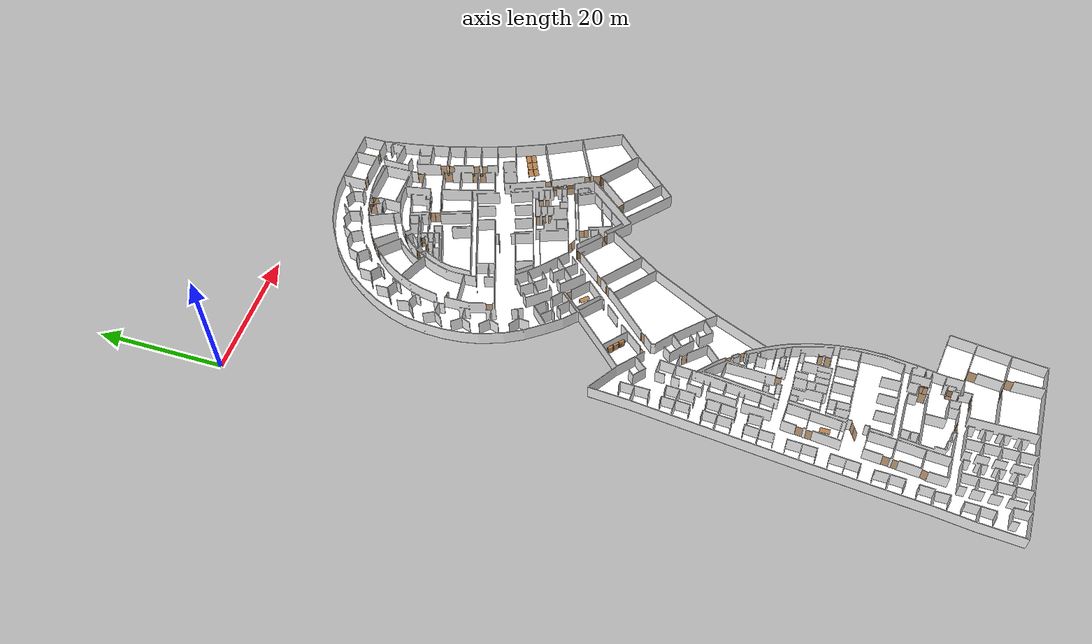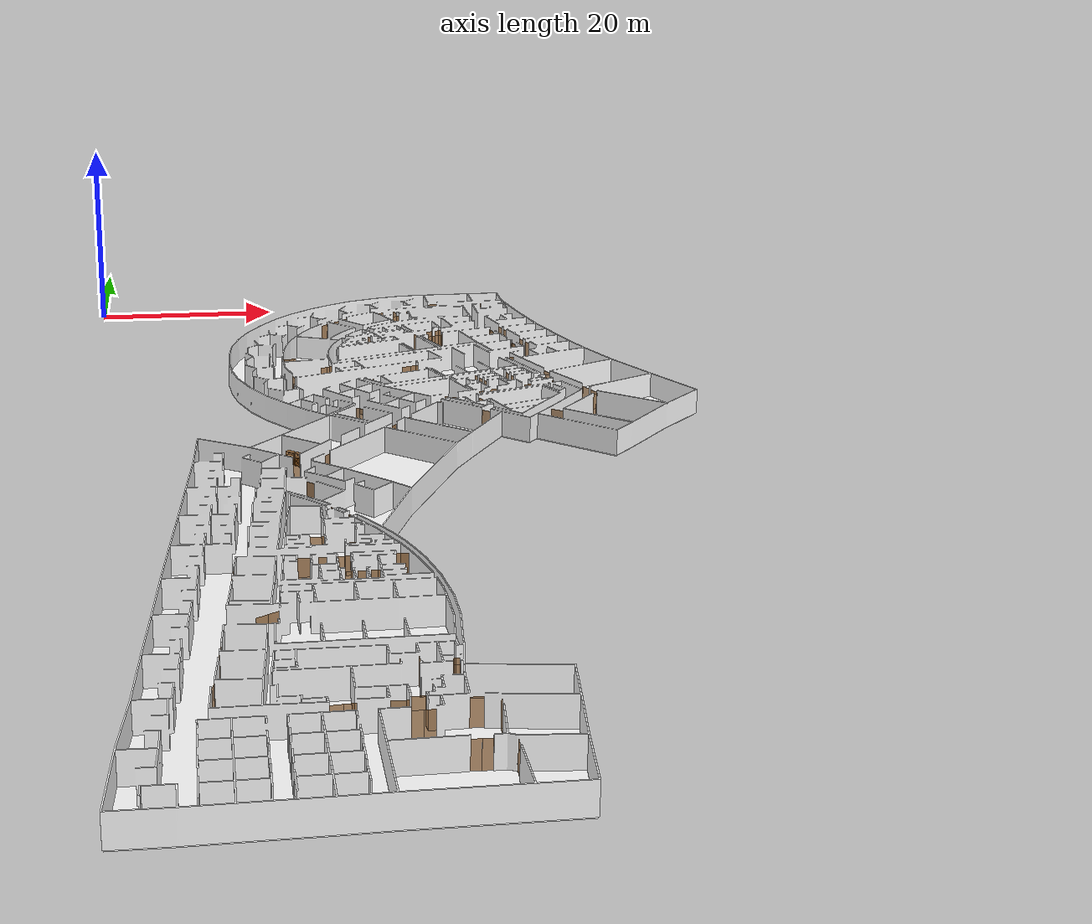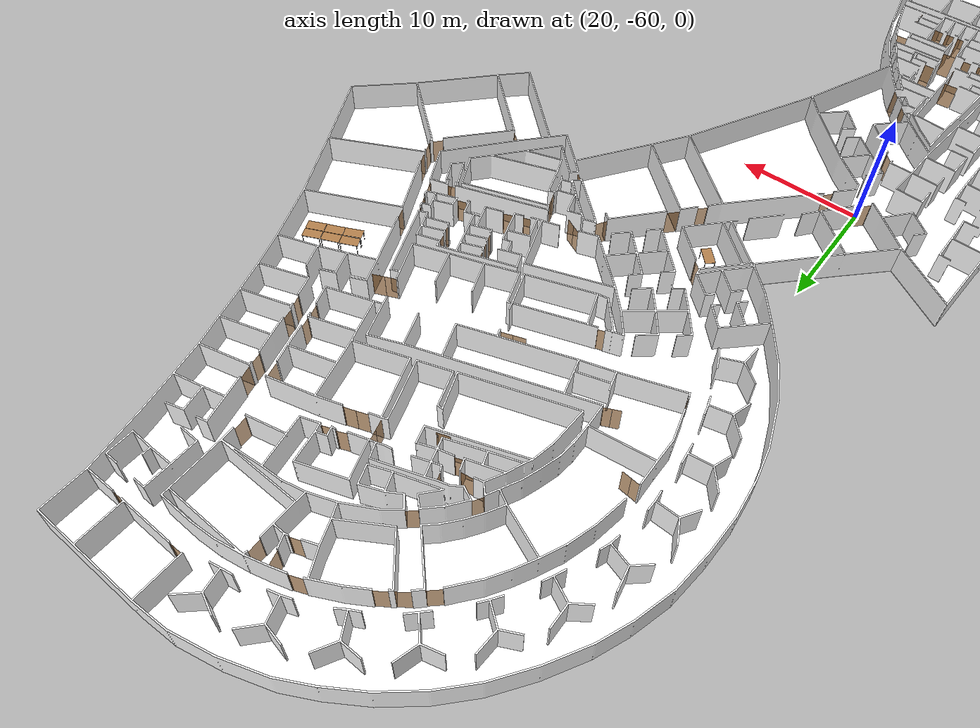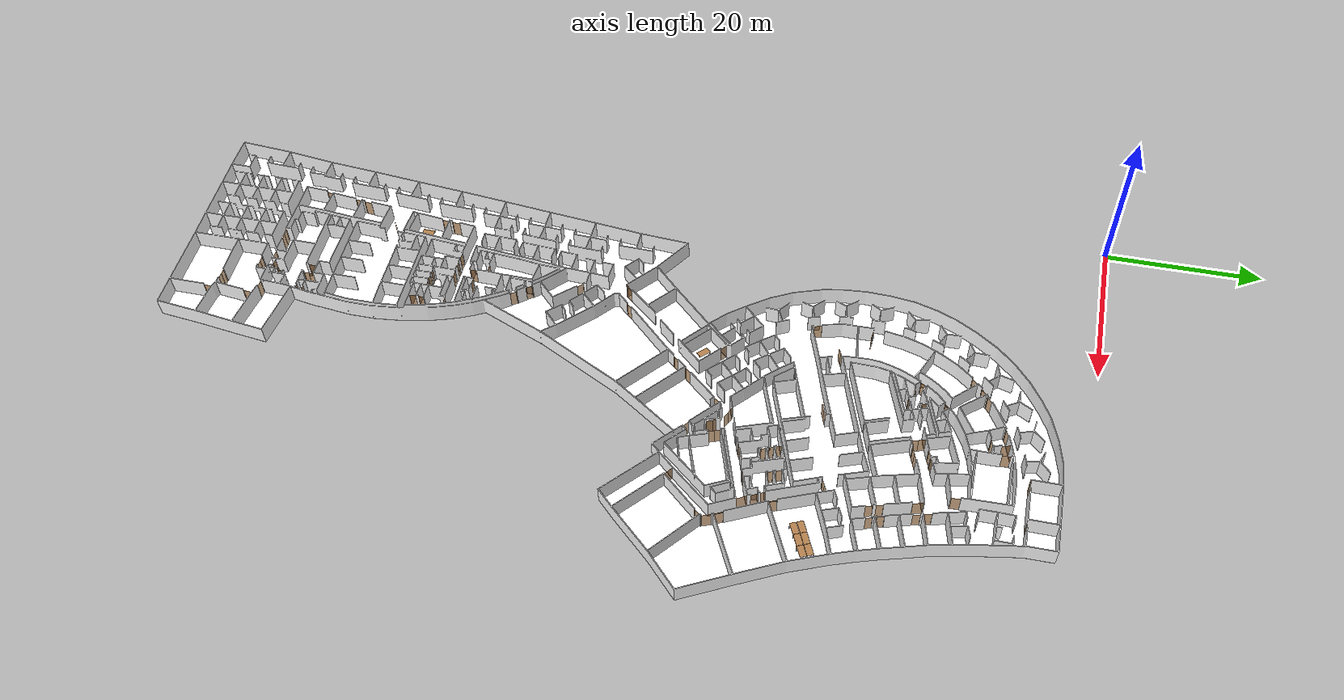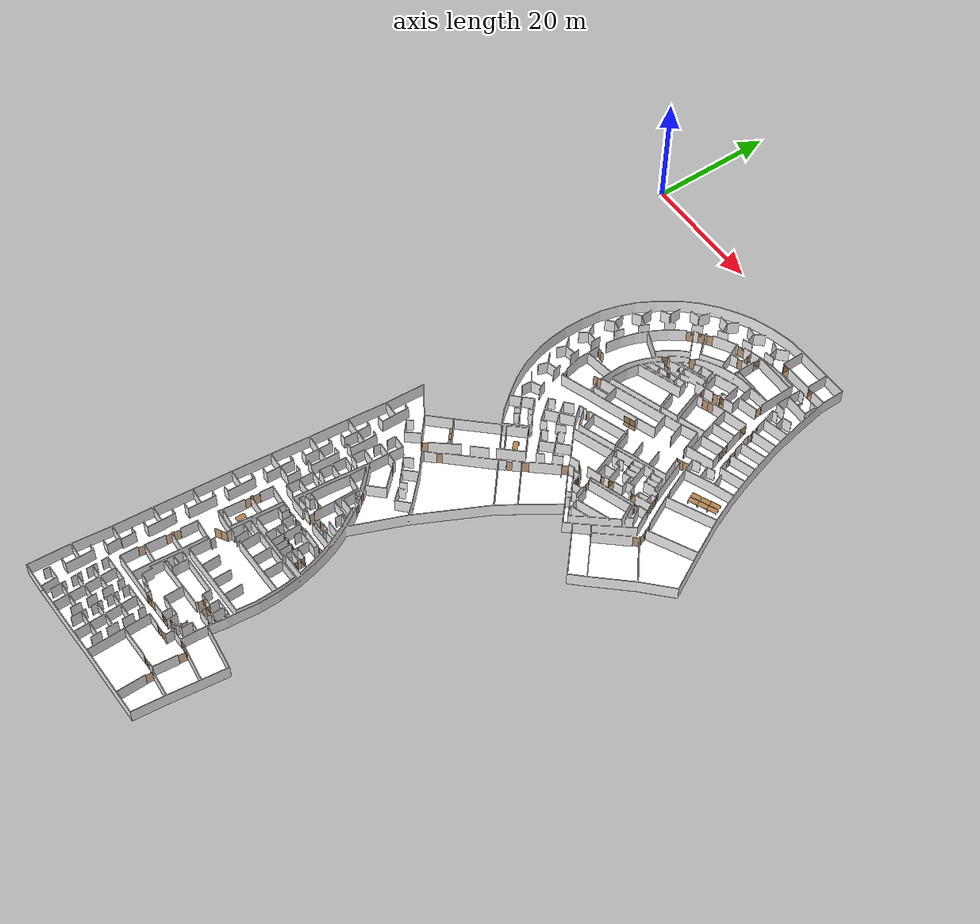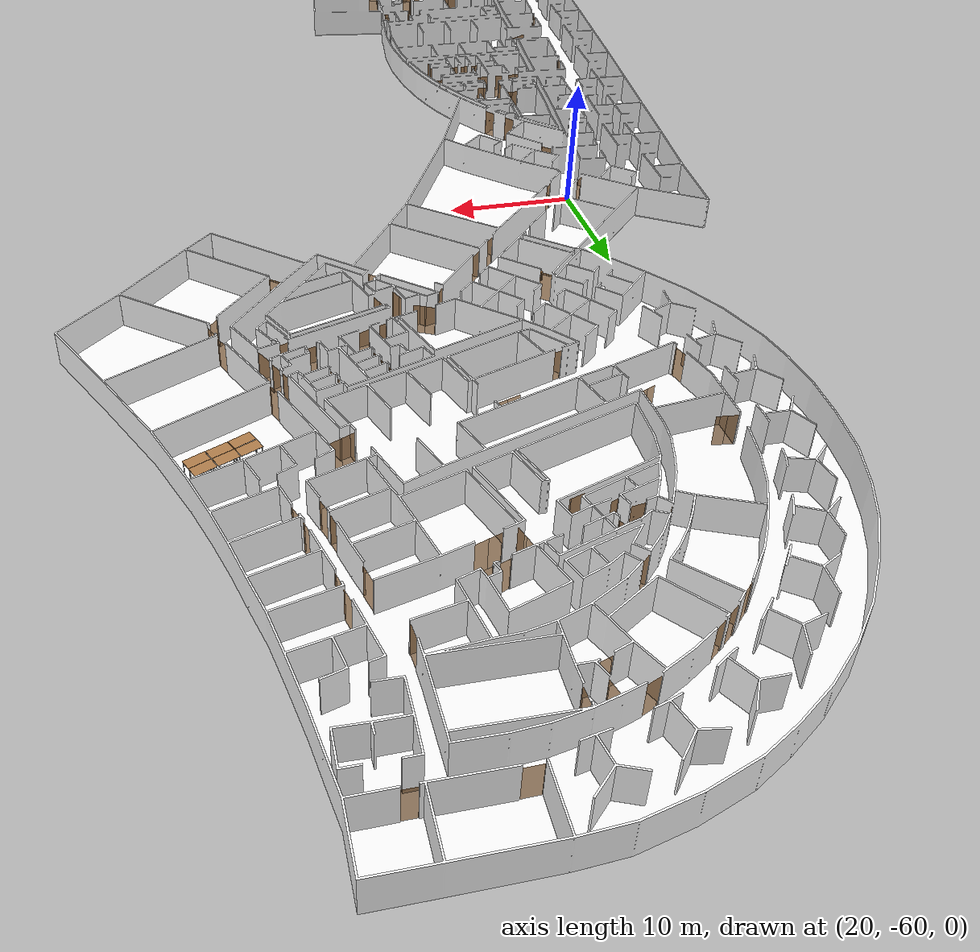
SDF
<sdf version="1.6">
 <world name="world">
  <scene>
   <ambient>0.8 0.8 0.8 1</ambient>
   <background>0 0 0 1</background>
   <grid>0</grid>
   <shadows>1</shadows>
  </scene>
  <light name="sun" type="directional">
   <pose>0 0 10 0 -0 0</pose>
   <diffuse>0.8 0.8 0.8 1</diffuse>
   <specular>0.2 0.2 0.2 1</specular>
   <attenuation>
    <range>1000</range>
    <constant>0.9</constant>
    <linear>0.01</linear>
    <quadratic>0.001</quadratic>
   </attenuation>
   <direction>-0.5 0.1 -0.9</direction>
   <spot><inner_angle>0</inner_angle><outer_angle>0</outer_angle><falloff>0</falloff></spot>
  </light>
  <model name="OpenRobotics/Table">
   <static>1</static>
   <link name="link">
    <collision name="surface">
     <pose>0 0 1 0 -0 0</pose>
     <geometry><box><size>1.5 0.8 0.03</size></box></geometry>
     <surface><friction><ode><mu>0.6</mu><mu2>0.6</mu2></ode></friction></surface>
    </collision>
    <visual name="visual1">
     <pose>0 0 1 0 -0 0</pose>
     <geometry><box><size>1.5 0.8 0.03</size></box></geometry>
     <material>
      <script><uri>file://media/materials/scripts/gazebo.material</uri><name>Gazebo/Wood</name></script>
     </material>
    </visual>
    <collision name="front_left_leg">
     <pose>0.68 0.38 0.5 0 -0 0</pose>
     <geometry><cylinder><radius>0.02</radius><length>1</length></cylinder></geometry>
    </collision>
    <visual name="front_left_leg">
     <pose>0.68 0.38 0.5 0 -0 0</pose>
     <geometry><cylinder><radius>0.02</radius><length>1</length></cylinder></geometry>
     <material>
      <script><uri>file://media/materials/scripts/gazebo.material</uri><name>Gazebo/Grey</name></script>
     </material>
    </visual>
    <collision name="front_right_leg">
     <pose>0.68 -0.38 0.5 0 -0 0</pose>
     <geometry><cylinder><radius>0.02</radius><length>1</length></cylinder></geometry>
    </collision>
    <visual name="front_right_leg">
     <pose>0.68 -0.38 0.5 0 -0 0</pose>
     <geometry><cylinder><radius>0.02</radius><length>1</length></cylinder></geometry>
     <material>
      <script><uri>file://media/materials/scripts/gazebo.material</uri><name>Gazebo/Grey</name></script>
     </material>
    </visual>
    <collision name="back_right_leg">
     <pose>-0.68 -0.38 0.5 0 -0 0</pose>
     <geometry><cylinder><radius>0.02</radius><length>1</length></cylinder></geometry>
    </collision>
    <visual name="back_right_leg">
     <pose>-0.68 -0.38 0.5 0 -0 0</pose>
     <geometry><cylinder><radius>0.02</radius><length>1</length></cylinder></geometry>
     <material>
      <script><uri>file://media/materials/scripts/gazebo.material</uri><name>Gazebo/Grey</name></script>
     </material>
    </visual>
    <collision name="back_left_leg">
     <pose>-0.68 0.38 0.5 0 -0 0</pose>
     <geometry><cylinder><radius>0.02</radius><length>1</length></cylinder></geometry>
    </collision>
    <visual name="back_left_leg">
     <pose>-0.68 0.38 0.5 0 -0 0</pose>
     <geometry><cylinder><radius>0.02</radius><length>1</length></cylinder></geometry>
     <material>
      <script><uri>file://media/materials/scripts/gazebo.material</uri><name>Gazebo/Grey</name></script>
     </material>
    </visual>
   </link>
   <pose>14.3878 -87.6644 0 0 -0 1.5708</pose>
  </model>
  <model name="OpenRobotics/Table_2">
   <static>1</static>
   <link name="link">
    <collision name="surface">
     <pose>0 0 1 0 -0 0</pose>
     <geometry><box><size>1.5 0.8 0.03</size></box></geometry>
     <surface><friction><ode><mu>0.6</mu><mu2>0.6</mu2></ode></friction></surface>
    </collision>
    <visual name="visual1">
     <pose>0 0 1 0 -0 0</pose>
     <geometry><box><size>1.5 0.8 0.03</size></box></geometry>
     <material>
      <script><uri>file://media/materials/scripts/gazebo.material</uri><name>Gazebo/Wood</name></script>
     </material>
    </visual>
    <collision name="front_left_leg">
     <pose>0.68 0.38 0.5 0 -0 0</pose>
     <geometry><cylinder><radius>0.02</radius><length>1</length></cylinder></geometry>
    </collision>
    <visual name="front_left_leg">
     <pose>0.68 0.38 0.5 0 -0 0</pose>
     <geometry><cylinder><radius>0.02</radius><length>1</length></cylinder></geometry>
     <material>
      <script><uri>file://media/materials/scripts/gazebo.material</uri><name>Gazebo/Grey</name></script>
     </material>
    </visual>
    <collision name="front_right_leg">
     <pose>0.68 -0.38 0.5 0 -0 0</pose>
     <geometry><cylinder><radius>0.02</radius><length>1</length></cylinder></geometry>
    </collision>
    <visual name="front_right_leg">
     <pose>0.68 -0.38 0.5 0 -0 0</pose>
     <geometry><cylinder><radius>0.02</radius><length>1</length></cylinder></geometry>
     <material>
      <script><uri>file://media/materials/scripts/gazebo.material</uri><name>Gazebo/Grey</name></script>
     </material>
    </visual>
    <collision name="back_right_leg">
     <pose>-0.68 -0.38 0.5 0 -0 0</pose>
     <geometry><cylinder><radius>0.02</radius><length>1</length></cylinder></geometry>
    </collision>
    <visual name="back_right_leg">
     <pose>-0.68 -0.38 0.5 0 -0 0</pose>
     <geometry><cylinder><radius>0.02</radius><length>1</length></cylinder></geometry>
     <material>
      <script><uri>file://media/materials/scripts/gazebo.material</uri><name>Gazebo/Grey</name></script>
     </material>
    </visual>
    <collision name="back_left_leg">
     <pose>-0.68 0.38 0.5 0 -0 0</pose>
     <geometry><cylinder><radius>0.02</radius><length>1</length></cylinder></geometry>
    </collision>
    <visual name="back_left_leg">
     <pose>-0.68 0.38 0.5 0 -0 0</pose>
     <geometry><cylinder><radius>0.02</radius><length>1</length></cylinder></geometry>
     <material>
      <script><uri>file://media/materials/scripts/gazebo.material</uri><name>Gazebo/Grey</name></script>
     </material>
    </visual>
   </link>
   <pose>26.7964 -48.1502 0 0 -0 2.3292</pose>
  </model>
  <model name="OpenRobotics/Table_3">
   <static>1</static>
   <link name="link">
    <collision name="surface">
     <pose>0 0 1 0 -0 0</pose>
     <geometry><box><size>1.5 0.8 0.03</size></box></geometry>
     <surface><friction><ode><mu>0.6</mu><mu2>0.6</mu2></ode></friction></surface>
    </collision>
    <visual name="visual1">
     <pose>0 0 1 0 -0 0</pose>
     <geometry><box><size>1.5 0.8 0.03</size></box></geometry>
     <material>
      <script><uri>file://media/materials/scripts/gazebo.material</uri><name>Gazebo/Wood</name></script>
     </material>
    </visual>
    <collision name="front_left_leg">
     <pose>0.68 0.38 0.5 0 -0 0</pose>
     <geometry><cylinder><radius>0.02</radius><length>1</length></cylinder></geometry>
    </collision>
    <visual name="front_left_leg">
     <pose>0.68 0.38 0.5 0 -0 0</pose>
     <geometry><cylinder><radius>0.02</radius><length>1</length></cylinder></geometry>
     <material>
      <script><uri>file://media/materials/scripts/gazebo.material</uri><name>Gazebo/Grey</name></script>
     </material>
    </visual>
    <collision name="front_right_leg">
     <pose>0.68 -0.38 0.5 0 -0 0</pose>
     <geometry><cylinder><radius>0.02</radius><length>1</length></cylinder></geometry>
    </collision>
    <visual name="front_right_leg">
     <pose>0.68 -0.38 0.5 0 -0 0</pose>
     <geometry><cylinder><radius>0.02</radius><length>1</length></cylinder></geometry>
     <material>
      <script><uri>file://media/materials/scripts/gazebo.material</uri><name>Gazebo/Grey</name></script>
     </material>
    </visual>
    <collision name="back_right_leg">
     <pose>-0.68 -0.38 0.5 0 -0 0</pose>
     <geometry><cylinder><radius>0.02</radius><length>1</length></cylinder></geometry>
    </collision>
    <visual name="back_right_leg">
     <pose>-0.68 -0.38 0.5 0 -0 0</pose>
     <geometry><cylinder><radius>0.02</radius><length>1</length></cylinder></geometry>
     <material>
      <script><uri>file://media/materials/scripts/gazebo.material</uri><name>Gazebo/Grey</name></script>
     </material>
    </visual>
    <collision name="back_left_leg">
     <pose>-0.68 0.38 0.5 0 -0 0</pose>
     <geometry><cylinder><radius>0.02</radius><length>1</length></cylinder></geometry>
    </collision>
    <visual name="back_left_leg">
     <pose>-0.68 0.38 0.5 0 -0 0</pose>
     <geometry><cylinder><radius>0.02</radius><length>1</length></cylinder></geometry>
     <material>
      <script><uri>file://media/materials/scripts/gazebo.material</uri><name>Gazebo/Grey</name></script>
     </material>
    </visual>
   </link>
   <pose>49.1187 -32.1514 0 0 -0 0.4303</pose>
  </model>
  <model name="OpenRobotics/Table_4">
   <static>1</static>
   <link name="link">
    <collision name="surface">
     <pose>0 0 1 0 -0 0</pose>
     <geometry><box><size>1.5 0.8 0.03</size></box></geometry>
     <surface><friction><ode><mu>0.6</mu><mu2>0.6</mu2></ode></friction></surface>
    </collision>
    <visual name="visual1">
     <pose>0 0 1 0 -0 0</pose>
     <geometry><box><size>1.5 0.8 0.03</size></box></geometry>
     <material>
      <script><uri>file://media/materials/scripts/gazebo.material</uri><name>Gazebo/Wood</name></script>
     </material>
    </visual>
    <collision name="front_left_leg">
     <pose>0.68 0.38 0.5 0 -0 0</pose>
     <geometry><cylinder><radius>0.02</radius><length>1</length></cylinder></geometry>
    </collision>
    <visual name="front_left_leg">
     <pose>0.68 0.38 0.5 0 -0 0</pose>
     <geometry><cylinder><radius>0.02</radius><length>1</length></cylinder></geometry>
     <material>
      <script><uri>file://media/materials/scripts/gazebo.material</uri><name>Gazebo/Grey</name></script>
     </material>
    </visual>
    <collision name="front_right_leg">
     <pose>0.68 -0.38 0.5 0 -0 0</pose>
     <geometry><cylinder><radius>0.02</radius><length>1</length></cylinder></geometry>
    </collision>
    <visual name="front_right_leg">
     <pose>0.68 -0.38 0.5 0 -0 0</pose>
     <geometry><cylinder><radius>0.02</radius><length>1</length></cylinder></geometry>
     <material>
      <script><uri>file://media/materials/scripts/gazebo.material</uri><name>Gazebo/Grey</name></script>
     </material>
    </visual>
    <collision name="back_right_leg">
     <pose>-0.68 -0.38 0.5 0 -0 0</pose>
     <geometry><cylinder><radius>0.02</radius><length>1</length></cylinder></geometry>
    </collision>
    <visual name="back_right_leg">
     <pose>-0.68 -0.38 0.5 0 -0 0</pose>
     <geometry><cylinder><radius>0.02</radius><length>1</length></cylinder></geometry>
     <material>
      <script><uri>file://media/materials/scripts/gazebo.material</uri><name>Gazebo/Grey</name></script>
     </material>
    </visual>
    <collision name="back_left_leg">
     <pose>-0.68 0.38 0.5 0 -0 0</pose>
     <geometry><cylinder><radius>0.02</radius><length>1</length></cylinder></geometry>
    </collision>
    <visual name="back_left_leg">
     <pose>-0.68 0.38 0.5 0 -0 0</pose>
     <geometry><cylinder><radius>0.02</radius><length>1</length></cylinder></geometry>
     <material>
      <script><uri>file://media/materials/scripts/gazebo.material</uri><name>Gazebo/Grey</name></script>
     </material>
    </visual>
   </link>
   <pose>50.5168 -31.5278 0 0 -0 0.4167</pose>
  </model>
  <model name="OpenRobotics/Table_5">
   <static>1</static>
   <link name="link">
    <collision name="surface">
     <pose>0 0 1 0 -0 0</pose>
     <geometry><box><size>1.5 0.8 0.03</size></box></geometry>
     <surface><friction><ode><mu>0.6</mu><mu2>0.6</mu2></ode></friction></surface>
    </collision>
    <visual name="visual1">
     <pose>0 0 1 0 -0 0</pose>
     <geometry><box><size>1.5 0.8 0.03</size></box></geometry>
     <material>
      <script><uri>file://media/materials/scripts/gazebo.material</uri><name>Gazebo/Wood</name></script>
     </material>
    </visual>
    <collision name="front_left_leg">
     <pose>0.68 0.38 0.5 0 -0 0</pose>
     <geometry><cylinder><radius>0.02</radius><length>1</length></cylinder></geometry>
    </collision>
    <visual name="front_left_leg">
     <pose>0.68 0.38 0.5 0 -0 0</pose>
     <geometry><cylinder><radius>0.02</radius><length>1</length></cylinder></geometry>
     <material>
      <script><uri>file://media/materials/scripts/gazebo.material</uri><name>Gazebo/Grey</name></script>
     </material>
    </visual>
    <collision name="front_right_leg">
     <pose>0.68 -0.38 0.5 0 -0 0</pose>
     <geometry><cylinder><radius>0.02</radius><length>1</length></cylinder></geometry>
    </collision>
    <visual name="front_right_leg">
     <pose>0.68 -0.38 0.5 0 -0 0</pose>
     <geometry><cylinder><radius>0.02</radius><length>1</length></cylinder></geometry>
     <material>
      <script><uri>file://media/materials/scripts/gazebo.material</uri><name>Gazebo/Grey</name></script>
     </material>
    </visual>
    <collision name="back_right_leg">
     <pose>-0.68 -0.38 0.5 0 -0 0</pose>
     <geometry><cylinder><radius>0.02</radius><length>1</length></cylinder></geometry>
    </collision>
    <visual name="back_right_leg">
     <pose>-0.68 -0.38 0.5 0 -0 0</pose>
     <geometry><cylinder><radius>0.02</radius><length>1</length></cylinder></geometry>
     <material>
      <script><uri>file://media/materials/scripts/gazebo.material</uri><name>Gazebo/Grey</name></script>
     </material>
    </visual>
    <collision name="back_left_leg">
     <pose>-0.68 0.38 0.5 0 -0 0</pose>
     <geometry><cylinder><radius>0.02</radius><length>1</length></cylinder></geometry>
    </collision>
    <visual name="back_left_leg">
     <pose>-0.68 0.38 0.5 0 -0 0</pose>
     <geometry><cylinder><radius>0.02</radius><length>1</length></cylinder></geometry>
     <material>
      <script><uri>file://media/materials/scripts/gazebo.material</uri><name>Gazebo/Grey</name></script>
     </material>
    </visual>
   </link>
   <pose>51.9247 -30.8942 0 0 -0 0.4347</pose>
  </model>
  <model name="OpenRobotics/Table_6">
   <static>1</static>
   <link name="link">
    <collision name="surface">
     <pose>0 0 1 0 -0 0</pose>
     <geometry><box><size>1.5 0.8 0.03</size></box></geometry>
     <surface><friction><ode><mu>0.6</mu><mu2>0.6</mu2></ode></friction></surface>
    </collision>
    <visual name="visual1">
     <pose>0 0 1 0 -0 0</pose>
     <geometry><box><size>1.5 0.8 0.03</size></box></geometry>
     <material>
      <script><uri>file://media/materials/scripts/gazebo.material</uri><name>Gazebo/Wood</name></script>
     </material>
    </visual>
    <collision name="front_left_leg">
     <pose>0.68 0.38 0.5 0 -0 0</pose>
     <geometry><cylinder><radius>0.02</radius><length>1</length></cylinder></geometry>
    </collision>
    <visual name="front_left_leg">
     <pose>0.68 0.38 0.5 0 -0 0</pose>
     <geometry><cylinder><radius>0.02</radius><length>1</length></cylinder></geometry>
     <material>
      <script><uri>file://media/materials/scripts/gazebo.material</uri><name>Gazebo/Grey</name></script>
     </material>
    </visual>
    <collision name="front_right_leg">
     <pose>0.68 -0.38 0.5 0 -0 0</pose>
     <geometry><cylinder><radius>0.02</radius><length>1</length></cylinder></geometry>
    </collision>
    <visual name="front_right_leg">
     <pose>0.68 -0.38 0.5 0 -0 0</pose>
     <geometry><cylinder><radius>0.02</radius><length>1</length></cylinder></geometry>
     <material>
      <script><uri>file://media/materials/scripts/gazebo.material</uri><name>Gazebo/Grey</name></script>
     </material>
    </visual>
    <collision name="back_right_leg">
     <pose>-0.68 -0.38 0.5 0 -0 0</pose>
     <geometry><cylinder><radius>0.02</radius><length>1</length></cylinder></geometry>
    </collision>
    <visual name="back_right_leg">
     <pose>-0.68 -0.38 0.5 0 -0 0</pose>
     <geometry><cylinder><radius>0.02</radius><length>1</length></cylinder></geometry>
     <material>
      <script><uri>file://media/materials/scripts/gazebo.material</uri><name>Gazebo/Grey</name></script>
     </material>
    </visual>
    <collision name="back_left_leg">
     <pose>-0.68 0.38 0.5 0 -0 0</pose>
     <geometry><cylinder><radius>0.02</radius><length>1</length></cylinder></geometry>
    </collision>
    <visual name="back_left_leg">
     <pose>-0.68 0.38 0.5 0 -0 0</pose>
     <geometry><cylinder><radius>0.02</radius><length>1</length></cylinder></geometry>
     <material>
      <script><uri>file://media/materials/scripts/gazebo.material</uri><name>Gazebo/Grey</name></script>
     </material>
    </visual>
   </link>
   <pose>52.2667 -31.6485 0 0 -0 0.4389</pose>
  </model>
  <model name="OpenRobotics/Table_7">
   <static>1</static>
   <link name="link">
    <collision name="surface">
     <pose>0 0 1 0 -0 0</pose>
     <geometry><box><size>1.5 0.8 0.03</size></box></geometry>
     <surface><friction><ode><mu>0.6</mu><mu2>0.6</mu2></ode></friction></surface>
    </collision>
    <visual name="visual1">
     <pose>0 0 1 0 -0 0</pose>
     <geometry><box><size>1.5 0.8 0.03</size></box></geometry>
     <material>
      <script><uri>file://media/materials/scripts/gazebo.material</uri><name>Gazebo/Wood</name></script>
     </material>
    </visual>
    <collision name="front_left_leg">
     <pose>0.68 0.38 0.5 0 -0 0</pose>
     <geometry><cylinder><radius>0.02</radius><length>1</length></cylinder></geometry>
    </collision>
    <visual name="front_left_leg">
     <pose>0.68 0.38 0.5 0 -0 0</pose>
     <geometry><cylinder><radius>0.02</radius><length>1</length></cylinder></geometry>
     <material>
      <script><uri>file://media/materials/scripts/gazebo.material</uri><name>Gazebo/Grey</name></script>
     </material>
    </visual>
    <collision name="front_right_leg">
     <pose>0.68 -0.38 0.5 0 -0 0</pose>
     <geometry><cylinder><radius>0.02</radius><length>1</length></cylinder></geometry>
    </collision>
    <visual name="front_right_leg">
     <pose>0.68 -0.38 0.5 0 -0 0</pose>
     <geometry><cylinder><radius>0.02</radius><length>1</length></cylinder></geometry>
     <material>
      <script><uri>file://media/materials/scripts/gazebo.material</uri><name>Gazebo/Grey</name></script>
     </material>
    </visual>
    <collision name="back_right_leg">
     <pose>-0.68 -0.38 0.5 0 -0 0</pose>
     <geometry><cylinder><radius>0.02</radius><length>1</length></cylinder></geometry>
    </collision>
    <visual name="back_right_leg">
     <pose>-0.68 -0.38 0.5 0 -0 0</pose>
     <geometry><cylinder><radius>0.02</radius><length>1</length></cylinder></geometry>
     <material>
      <script><uri>file://media/materials/scripts/gazebo.material</uri><name>Gazebo/Grey</name></script>
     </material>
    </visual>
    <collision name="back_left_leg">
     <pose>-0.68 0.38 0.5 0 -0 0</pose>
     <geometry><cylinder><radius>0.02</radius><length>1</length></cylinder></geometry>
    </collision>
    <visual name="back_left_leg">
     <pose>-0.68 0.38 0.5 0 -0 0</pose>
     <geometry><cylinder><radius>0.02</radius><length>1</length></cylinder></geometry>
     <material>
      <script><uri>file://media/materials/scripts/gazebo.material</uri><name>Gazebo/Grey</name></script>
     </material>
    </visual>
   </link>
   <pose>50.8587 -32.2821 0 0 -0 0.4288</pose>
  </model>
  <model name="OpenRobotics/Table_8">
   <static>1</static>
   <link name="link">
    <collision name="surface">
     <pose>0 0 1 0 -0 0</pose>
     <geometry><box><size>1.5 0.8 0.03</size></box></geometry>
     <surface><friction><ode><mu>0.6</mu><mu2>0.6</mu2></ode></friction></surface>
    </collision>
    <visual name="visual1">
     <pose>0 0 1 0 -0 0</pose>
     <geometry><box><size>1.5 0.8 0.03</size></box></geometry>
     <material>
      <script><uri>file://media/materials/scripts/gazebo.material</uri><name>Gazebo/Wood</name></script>
     </material>
    </visual>
    <collision name="front_left_leg">
     <pose>0.68 0.38 0.5 0 -0 0</pose>
     <geometry><cylinder><radius>0.02</radius><length>1</length></cylinder></geometry>
    </collision>
    <visual name="front_left_leg">
     <pose>0.68 0.38 0.5 0 -0 0</pose>
     <geometry><cylinder><radius>0.02</radius><length>1</length></cylinder></geometry>
     <material>
      <script><uri>file://media/materials/scripts/gazebo.material</uri><name>Gazebo/Grey</name></script>
     </material>
    </visual>
    <collision name="front_right_leg">
     <pose>0.68 -0.38 0.5 0 -0 0</pose>
     <geometry><cylinder><radius>0.02</radius><length>1</length></cylinder></geometry>
    </collision>
    <visual name="front_right_leg">
     <pose>0.68 -0.38 0.5 0 -0 0</pose>
     <geometry><cylinder><radius>0.02</radius><length>1</length></cylinder></geometry>
     <material>
      <script><uri>file://media/materials/scripts/gazebo.material</uri><name>Gazebo/Grey</name></script>
     </material>
    </visual>
    <collision name="back_right_leg">
     <pose>-0.68 -0.38 0.5 0 -0 0</pose>
     <geometry><cylinder><radius>0.02</radius><length>1</length></cylinder></geometry>
    </collision>
    <visual name="back_right_leg">
     <pose>-0.68 -0.38 0.5 0 -0 0</pose>
     <geometry><cylinder><radius>0.02</radius><length>1</length></cylinder></geometry>
     <material>
      <script><uri>file://media/materials/scripts/gazebo.material</uri><name>Gazebo/Grey</name></script>
     </material>
    </visual>
    <collision name="back_left_leg">
     <pose>-0.68 0.38 0.5 0 -0 0</pose>
     <geometry><cylinder><radius>0.02</radius><length>1</length></cylinder></geometry>
    </collision>
    <visual name="back_left_leg">
     <pose>-0.68 0.38 0.5 0 -0 0</pose>
     <geometry><cylinder><radius>0.02</radius><length>1</length></cylinder></geometry>
     <material>
      <script><uri>file://media/materials/scripts/gazebo.material</uri><name>Gazebo/Grey</name></script>
     </material>
    </visual>
   </link>
   <pose>49.4808 -32.9359 0 0 -0 0.4547</pose>
  </model>
  <model name="OpenRobotics/Bookshelf">
   <static>1</static>
   <link name="link">
    <inertial><mass>1</mass></inertial>
    <collision name="back">
     <pose>0 0.005 0.6 0 -0 0</pose>
     <geometry><box><size>0.9 0.01 1.2</size></box></geometry>
    </collision>
    <visual name="visual1">
     <pose>0 0.005 0.6 0 -0 0</pose>
     <geometry><box><size>0.9 0.01 1.2</size></box></geometry>
     <material>
      <script><uri>file://media/materials/scripts/gazebo.material</uri><name>Gazebo/Wood</name></script>
     </material>
    </visual>
    <collision name="left_side">
     <pose>0.45 -0.195 0.6 0 -0 0</pose>
     <geometry><box><size>0.02 0.4 1.2</size></box></geometry>
    </collision>
    <visual name="visual2">
     <pose>0.45 -0.195 0.6 0 -0 0</pose>
     <geometry><box><size>0.02 0.4 1.2</size></box></geometry>
     <material>
      <script><uri>file://media/materials/scripts/gazebo.material</uri><name>Gazebo/Wood</name></script>
     </material>
    </visual>
    <collision name="right_side">
     <pose>-0.45 -0.195 0.6 0 -0 0</pose>
     <geometry><box><size>0.02 0.4 1.2</size></box></geometry>
    </collision>
    <visual name="visual3">
     <pose>-0.45 -0.195 0.6 0 -0 0</pose>
     <geometry><box><size>0.02 0.4 1.2</size></box></geometry>
     <material>
      <script><uri>file://media/materials/scripts/gazebo.material</uri><name>Gazebo/Wood</name></script>
     </material>
    </visual>
    <collision name="bottom">
     <pose>0 -0.195 0.03 0 -0 0</pose>
     <geometry><box><size>0.88 0.4 0.06</size></box></geometry>
    </collision>
    <visual name="visual4">
     <pose>0 -0.195 0.03 0 -0 0</pose>
     <geometry><box><size>0.88 0.4 0.06</size></box></geometry>
     <material>
      <script><uri>file://media/materials/scripts/gazebo.material</uri><name>Gazebo/Wood</name></script>
     </material>
    </visual>
    <collision name="top">
     <pose>0 -0.195 1.19 0 -0 0</pose>
     <geometry><box><size>0.88 0.4 0.02</size></box></geometry>
    </collision>
    <visual name="visual5">
     <pose>0 -0.195 1.19 0 -0 0</pose>
     <geometry><box><size>0.88 0.4 0.02</size></box></geometry>
     <material>
      <script><uri>file://media/materials/scripts/gazebo.material</uri><name>Gazebo/Wood</name></script>
     </material>
    </visual>
    <collision name="low_shelf">
     <pose>0 -0.195 0.43 0 -0 0</pose>
     <geometry><box><size>0.88 0.4 0.02</size></box></geometry>
    </collision>
    <visual name="visual6">
     <pose>0 -0.195 0.43 0 -0 0</pose>
     <geometry><box><size>0.88 0.4 0.02</size></box></geometry>
     <material>
      <script><uri>file://media/materials/scripts/gazebo.material</uri><name>Gazebo/Wood</name></script>
     </material>
    </visual>
    <collision name="high_shelf">
     <pose>0 -0.195 0.8 0 -0 0</pose>
     <geometry><box><size>0.88 0.4 0.02</size></box></geometry>
    </collision>
    <visual name="visual7">
     <pose>0 -0.195 0.8 0 -0 0</pose>
     <geometry><box><size>0.88 0.4 0.02</size></box></geometry>
     <material>
      <script><uri>file://media/materials/scripts/gazebo.material</uri><name>Gazebo/Wood</name></script>
     </material>
    </visual>
   </link>
   <pose>19.4161 -54.2992 0 0 0 -0.7204</pose>
  </model>
  <model name="OpenRobotics/Bookshelf_2">
   <static>1</static>
   <link name="link">
    <inertial><mass>1</mass></inertial>
    <collision name="back">
     <pose>0 0.005 0.6 0 -0 0</pose>
     <geometry><box><size>0.9 0.01 1.2</size></box></geometry>
    </collision>
    <visual name="visual1">
     <pose>0 0.005 0.6 0 -0 0</pose>
     <geometry><box><size>0.9 0.01 1.2</size></box></geometry>
     <material>
      <script><uri>file://media/materials/scripts/gazebo.material</uri><name>Gazebo/Wood</name></script>
     </material>
    </visual>
    <collision name="left_side">
     <pose>0.45 -0.195 0.6 0 -0 0</pose>
     <geometry><box><size>0.02 0.4 1.2</size></box></geometry>
    </collision>
    <visual name="visual2">
     <pose>0.45 -0.195 0.6 0 -0 0</pose>
     <geometry><box><size>0.02 0.4 1.2</size></box></geometry>
     <material>
      <script><uri>file://media/materials/scripts/gazebo.material</uri><name>Gazebo/Wood</name></script>
     </material>
    </visual>
    <collision name="right_side">
     <pose>-0.45 -0.195 0.6 0 -0 0</pose>
     <geometry><box><size>0.02 0.4 1.2</size></box></geometry>
    </collision>
    <visual name="visual3">
     <pose>-0.45 -0.195 0.6 0 -0 0</pose>
     <geometry><box><size>0.02 0.4 1.2</size></box></geometry>
     <material>
      <script><uri>file://media/materials/scripts/gazebo.material</uri><name>Gazebo/Wood</name></script>
     </material>
    </visual>
    <collision name="bottom">
     <pose>0 -0.195 0.03 0 -0 0</pose>
     <geometry><box><size>0.88 0.4 0.06</size></box></geometry>
    </collision>
    <visual name="visual4">
     <pose>0 -0.195 0.03 0 -0 0</pose>
     <geometry><box><size>0.88 0.4 0.06</size></box></geometry>
     <material>
      <script><uri>file://media/materials/scripts/gazebo.material</uri><name>Gazebo/Wood</name></script>
     </material>
    </visual>
    <collision name="top">
     <pose>0 -0.195 1.19 0 -0 0</pose>
     <geometry><box><size>0.88 0.4 0.02</size></box></geometry>
    </collision>
    <visual name="visual5">
     <pose>0 -0.195 1.19 0 -0 0</pose>
     <geometry><box><size>0.88 0.4 0.02</size></box></geometry>
     <material>
      <script><uri>file://media/materials/scripts/gazebo.material</uri><name>Gazebo/Wood</name></script>
     </material>
    </visual>
    <collision name="low_shelf">
     <pose>0 -0.195 0.43 0 -0 0</pose>
     <geometry><box><size>0.88 0.4 0.02</size></box></geometry>
    </collision>
    <visual name="visual6">
     <pose>0 -0.195 0.43 0 -0 0</pose>
     <geometry><box><size>0.88 0.4 0.02</size></box></geometry>
     <material>
      <script><uri>file://media/materials/scripts/gazebo.material</uri><name>Gazebo/Wood</name></script>
     </material>
    </visual>
    <collision name="high_shelf">
     <pose>0 -0.195 0.8 0 -0 0</pose>
     <geometry><box><size>0.88 0.4 0.02</size></box></geometry>
    </collision>
    <visual name="visual7">
     <pose>0 -0.195 0.8 0 -0 0</pose>
     <geometry><box><size>0.88 0.4 0.02</size></box></geometry>
     <material>
      <script><uri>file://media/materials/scripts/gazebo.material</uri><name>Gazebo/Wood</name></script>
     </material>
    </visual>
   </link>
   <pose>20.1799 -54.9462 0 0 0 -0.7282</pose>
  </model>
  <model name="OpenRobotics/Bookshelf_3">
   <static>1</static>
   <link name="link">
    <inertial><mass>1</mass></inertial>
    <collision name="back">
     <pose>0 0.005 0.6 0 -0 0</pose>
     <geometry><box><size>0.9 0.01 1.2</size></box></geometry>
    </collision>
    <visual name="visual1">
     <pose>0 0.005 0.6 0 -0 0</pose>
     <geometry><box><size>0.9 0.01 1.2</size></box></geometry>
     <material>
      <script><uri>file://media/materials/scripts/gazebo.material</uri><name>Gazebo/Wood</name></script>
     </material>
    </visual>
    <collision name="left_side">
     <pose>0.45 -0.195 0.6 0 -0 0</pose>
     <geometry><box><size>0.02 0.4 1.2</size></box></geometry>
    </collision>
    <visual name="visual2">
     <pose>0.45 -0.195 0.6 0 -0 0</pose>
     <geometry><box><size>0.02 0.4 1.2</size></box></geometry>
     <material>
      <script><uri>file://media/materials/scripts/gazebo.material</uri><name>Gazebo/Wood</name></script>
     </material>
    </visual>
    <collision name="right_side">
     <pose>-0.45 -0.195 0.6 0 -0 0</pose>
     <geometry><box><size>0.02 0.4 1.2</size></box></geometry>
    </collision>
    <visual name="visual3">
     <pose>-0.45 -0.195 0.6 0 -0 0</pose>
     <geometry><box><size>0.02 0.4 1.2</size></box></geometry>
     <material>
      <script><uri>file://media/materials/scripts/gazebo.material</uri><name>Gazebo/Wood</name></script>
     </material>
    </visual>
    <collision name="bottom">
     <pose>0 -0.195 0.03 0 -0 0</pose>
     <geometry><box><size>0.88 0.4 0.06</size></box></geometry>
    </collision>
    <visual name="visual4">
     <pose>0 -0.195 0.03 0 -0 0</pose>
     <geometry><box><size>0.88 0.4 0.06</size></box></geometry>
     <material>
      <script><uri>file://media/materials/scripts/gazebo.material</uri><name>Gazebo/Wood</name></script>
     </material>
    </visual>
    <collision name="top">
     <pose>0 -0.195 1.19 0 -0 0</pose>
     <geometry><box><size>0.88 0.4 0.02</size></box></geometry>
    </collision>
    <visual name="visual5">
     <pose>0 -0.195 1.19 0 -0 0</pose>
     <geometry><box><size>0.88 0.4 0.02</size></box></geometry>
     <material>
      <script><uri>file://media/materials/scripts/gazebo.material</uri><name>Gazebo/Wood</name></script>
     </material>
    </visual>
    <collision name="low_shelf">
     <pose>0 -0.195 0.43 0 -0 0</pose>
     <geometry><box><size>0.88 0.4 0.02</size></box></geometry>
    </collision>
    <visual name="visual6">
     <pose>0 -0.195 0.43 0 -0 0</pose>
     <geometry><box><size>0.88 0.4 0.02</size></box></geometry>
     <material>
      <script><uri>file://media/materials/scripts/gazebo.material</uri><name>Gazebo/Wood</name></script>
     </material>
    </visual>
    <collision name="high_shelf">
     <pose>0 -0.195 0.8 0 -0 0</pose>
     <geometry><box><size>0.88 0.4 0.02</size></box></geometry>
    </collision>
    <visual name="visual7">
     <pose>0 -0.195 0.8 0 -0 0</pose>
     <geometry><box><size>0.88 0.4 0.02</size></box></geometry>
     <material>
      <script><uri>file://media/materials/scripts/gazebo.material</uri><name>Gazebo/Wood</name></script>
     </material>
    </visual>
   </link>
   <pose>20.9437 -55.604 0 0 0 -0.7114</pose>
  </model>
  <model name="D1">
   <pose>46.734 -38.1165 0 0 -0 -1.09898</pose>
   <link name="right">
    <pose>0 0 1.11 0 -0 0</pose>
    <visual name="right_visual">
     <geometry><box><size>0.995473 0.03 2.2</size></box></geometry>
     <material><ambient>0.5 0.25 0 0.6</ambient><diffuse>0.5 0.25 0 0.6</diffuse></material>
    </visual>
    <collision name="right_collision">
     <geometry><box><size>0.995473 0.03 2.2</size></box></geometry>
     <surface><contact><collide_bitmask>2</collide_bitmask></contact></surface>
    </collision>
    <inertial>
     <mass>50</mass>
     <inertia><ixx>20.1704</ixx><iyy>24.2957</iyy><izz>4.13277</izz><ixy>0</ixy><ixz>0</ixz><iyz>0</iyz></inertia>
    </inertial>
   </link>
   <joint name="right_joint" type="revolute">
    <parent>world</parent>
    <child>right</child>
    <axis>
     <xyz>0 0 1</xyz>
     <limit><lower>0</lower><upper>1.57</upper></limit>
     <dynamics><spring_reference>0</spring_reference><spring_stiffness>0</spring_stiffness></dynamics>
     <use_parent_model_frame>0</use_parent_model_frame>
    </axis>
    <pose>0.502736 0 0 0 -0 0</pose>
   </joint>
   <plugin name="door_D1" filename="libdoor.so">
    <v_max_door>0.5</v_max_door>
    <a_max_door>0.3</a_max_door>
    <a_nom_door>0.15</a_nom_door>
    <dx_min_door>0.01</dx_min_door>
    <f_max_door>500.0</f_max_door>
    <door name="D1" type="SwingDoor" left_joint_name="empty_joint" right_joint_name="right_joint"/>
   </plugin>
  </model>
  <model name="D2">
   <pose>40.5795 -41.0884 0 0 0 -2.71335</pose>
   <link name="right">
    <pose>0 0 1.11 0 -0 0</pose>
    <visual name="right_visual">
     <geometry><box><size>0.922305 0.03 2.2</size></box></geometry>
     <material><ambient>0.5 0.25 0 0.6</ambient><diffuse>0.5 0.25 0 0.6</diffuse></material>
    </visual>
    <collision name="right_collision">
     <geometry><box><size>0.922305 0.03 2.2</size></box></geometry>
     <surface><contact><collide_bitmask>2</collide_bitmask></contact></surface>
    </collision>
    <inertial>
     <mass>50</mass>
     <inertia><ixx>20.1704</ixx><iyy>23.711</iyy><izz>3.54811</izz><ixy>0</ixy><ixz>0</ixz><iyz>0</iyz></inertia>
    </inertial>
   </link>
   <joint name="right_joint" type="revolute">
    <parent>world</parent>
    <child>right</child>
    <axis>
     <xyz>0 0 1</xyz>
     <limit><lower>0</lower><upper>1.57</upper></limit>
     <dynamics><spring_reference>0</spring_reference><spring_stiffness>0</spring_stiffness></dynamics>
     <use_parent_model_frame>0</use_parent_model_frame>
    </axis>
    <pose>0.466153 0 0 0 -0 0</pose>
   </joint>
   <plugin name="door_D2" filename="libdoor.so">
    <v_max_door>0.5</v_max_door>
    <a_max_door>0.3</a_max_door>
    <a_nom_door>0.15</a_nom_door>
    <dx_min_door>0.01</dx_min_door>
    <f_max_door>500.0</f_max_door>
    <door name="D2" type="SwingDoor" left_joint_name="empty_joint" right_joint_name="right_joint"/>
   </plugin>
  </model>
  <model name="D3">
   <pose>44.2806 -39.9356 -0 0 0 -2.80852</pose>
   <link name="right">
    <pose>0 0 1.11 0 -0 0</pose>
    <visual name="right_visual">
     <geometry><box><size>0.838853 0.03 2.2</size></box></geometry>
     <material><ambient>0.5 0.25 0 0.6</ambient><diffuse>0.5 0.25 0 0.6</diffuse></material>
    </visual>
    <collision name="right_collision">
     <geometry><box><size>0.838853 0.03 2.2</size></box></geometry>
     <surface><contact><collide_bitmask>2</collide_bitmask></contact></surface>
    </collision>
    <inertial>
     <mass>50</mass>
     <inertia><ixx>20.1704</ixx><iyy>23.0986</iyy><izz>2.93572</izz><ixy>0</ixy><ixz>0</ixz><iyz>0</iyz></inertia>
    </inertial>
   </link>
   <joint name="right_joint" type="revolute">
    <parent>world</parent>
    <child>right</child>
    <axis>
     <xyz>0 0 1</xyz>
     <limit><lower>0</lower><upper>1.57</upper></limit>
     <dynamics><spring_reference>0</spring_reference><spring_stiffness>0</spring_stiffness></dynamics>
     <use_parent_model_frame>0</use_parent_model_frame>
    </axis>
    <pose>0.424426 0 0 0 -0 0</pose>
   </joint>
   <plugin name="door_D3" filename="libdoor.so">
    <v_max_door>0.5</v_max_door>
    <a_max_door>0.3</a_max_door>
    <a_nom_door>0.15</a_nom_door>
    <dx_min_door>0.01</dx_min_door>
    <f_max_door>500.0</f_max_door>
    <door name="D3" type="SwingDoor" left_joint_name="empty_joint" right_joint_name="right_joint"/>
   </plugin>
  </model>
  <model name="D4">
   <pose>46.2677 -37.1758 -0 0 0 -1.0969</pose>
   <link name="right">
    <pose>0 0 1.11 0 -0 0</pose>
    <visual name="right_visual">
     <geometry><box><size>0.672919 0.03 2.2</size></box></geometry>
     <material><ambient>0.5 0.25 0 0.6</ambient><diffuse>0.5 0.25 0 0.6</diffuse></material>
    </visual>
    <collision name="right_collision">
     <geometry><box><size>0.672919 0.03 2.2</size></box></geometry>
     <surface><contact><collide_bitmask>2</collide_bitmask></contact></surface>
    </collision>
    <inertial>
     <mass>50</mass>
     <inertia><ixx>20.1704</ixx><iyy>22.0534</iyy><izz>1.8905</izz><ixy>0</ixy><ixz>0</ixz><iyz>0</iyz></inertia>
    </inertial>
   </link>
   <joint name="right_joint" type="revolute">
    <parent>world</parent>
    <child>right</child>
    <axis>
     <xyz>0 0 1</xyz>
     <limit><lower>0</lower><upper>1.57</upper></limit>
     <dynamics><spring_reference>0</spring_reference><spring_stiffness>0</spring_stiffness></dynamics>
     <use_parent_model_frame>0</use_parent_model_frame>
    </axis>
    <pose>0.34146 0 0 0 -0 0</pose>
   </joint>
   <plugin name="door_D4" filename="libdoor.so">
    <v_max_door>0.5</v_max_door>
    <a_max_door>0.3</a_max_door>
    <a_nom_door>0.15</a_nom_door>
    <dx_min_door>0.01</dx_min_door>
    <f_max_door>500.0</f_max_door>
    <door name="D4" type="SwingDoor" left_joint_name="empty_joint" right_joint_name="right_joint"/>
   </plugin>
  </model>
  <model name="D5">
   <pose>47.1461 -35.8918 0 0 -0 -1.15391</pose>
   <link name="right">
    <pose>0 0 1.11 0 -0 0</pose>
    <visual name="right_visual">
     <geometry><box><size>1.10714 0.03 2.2</size></box></geometry>
     <material><ambient>0.5 0.25 0 0.6</ambient><diffuse>0.5 0.25 0 0.6</diffuse></material>
    </visual>
    <collision name="right_collision">
     <geometry><box><size>1.10714 0.03 2.2</size></box></geometry>
     <surface><contact><collide_bitmask>2</collide_bitmask></contact></surface>
    </collision>
    <inertial>
     <mass>50</mass>
     <inertia><ixx>20.1704</ixx><iyy>25.274</iyy><izz>5.11105</izz><ixy>0</ixy><ixz>0</ixz><iyz>0</iyz></inertia>
    </inertial>
   </link>
   <joint name="right_joint" type="revolute">
    <parent>world</parent>
    <child>right</child>
    <axis>
     <xyz>0 0 -1</xyz>
     <limit><lower>0</lower><upper>1.57</upper></limit>
     <dynamics><spring_reference>0</spring_reference><spring_stiffness>0</spring_stiffness></dynamics>
     <use_parent_model_frame>0</use_parent_model_frame>
    </axis>
    <pose>0.558568 0 0 0 -0 0</pose>
   </joint>
   <plugin name="door_D5" filename="libdoor.so">
    <v_max_door>0.5</v_max_door>
    <a_max_door>0.3</a_max_door>
    <a_nom_door>0.15</a_nom_door>
    <dx_min_door>0.01</dx_min_door>
    <f_max_door>500.0</f_max_door>
    <door name="D5" type="SwingDoor" left_joint_name="empty_joint" right_joint_name="right_joint"/>
   </plugin>
  </model>
  <model name="D6">
   <pose>49.9364 -41.6614 -0 0 -0 -1.13197</pose>
   <link name="right">
    <pose>0 0 1.11 0 -0 0</pose>
    <visual name="right_visual">
     <geometry><box><size>1.18487 0.03 2.2</size></box></geometry>
     <material><ambient>0.5 0.25 0 0.6</ambient><diffuse>0.5 0.25 0 0.6</diffuse></material>
    </visual>
    <collision name="right_collision">
     <geometry><box><size>1.18487 0.03 2.2</size></box></geometry>
     <surface><contact><collide_bitmask>2</collide_bitmask></contact></surface>
    </collision>
    <inertial>
     <mass>50</mass>
     <inertia><ixx>20.1704</ixx><iyy>26.0163</iyy><izz>5.85339</izz><ixy>0</ixy><ixz>0</ixz><iyz>0</iyz></inertia>
    </inertial>
   </link>
   <joint name="right_joint" type="revolute">
    <parent>world</parent>
    <child>right</child>
    <axis>
     <xyz>0 0 -1</xyz>
     <limit><lower>0</lower><upper>1.57</upper></limit>
     <dynamics><spring_reference>0</spring_reference><spring_stiffness>0</spring_stiffness></dynamics>
     <use_parent_model_frame>0</use_parent_model_frame>
    </axis>
    <pose>0.597435 0 0 0 -0 0</pose>
   </joint>
   <plugin name="door_D6" filename="libdoor.so">
    <v_max_door>0.5</v_max_door>
    <a_max_door>0.3</a_max_door>
    <a_nom_door>0.15</a_nom_door>
    <dx_min_door>0.01</dx_min_door>
    <f_max_door>500.0</f_max_door>
    <door name="D6" type="SwingDoor" left_joint_name="empty_joint" right_joint_name="right_joint"/>
   </plugin>
  </model>
  <model name="D7">
   <pose>50.4968 -42.9865 0 0 -0 -1.18211</pose>
   <link name="right">
    <pose>0 0 1.11 0 -0 0</pose>
    <visual name="right_visual">
     <geometry><box><size>1.21471 0.03 2.2</size></box></geometry>
     <material><ambient>0.5 0.25 0 0.6</ambient><diffuse>0.5 0.25 0 0.6</diffuse></material>
    </visual>
    <collision name="right_collision">
     <geometry><box><size>1.21471 0.03 2.2</size></box></geometry>
     <surface><contact><collide_bitmask>2</collide_bitmask></contact></surface>
    </collision>
    <inertial>
     <mass>50</mass>
     <inertia><ixx>20.1704</ixx><iyy>26.3147</iyy><izz>6.15175</izz><ixy>0</ixy><ixz>0</ixz><iyz>0</iyz></inertia>
    </inertial>
   </link>
   <joint name="right_joint" type="revolute">
    <parent>world</parent>
    <child>right</child>
    <axis>
     <xyz>0 0 1</xyz>
     <limit><lower>0</lower><upper>1.57</upper></limit>
     <dynamics><spring_reference>0</spring_reference><spring_stiffness>0</spring_stiffness></dynamics>
     <use_parent_model_frame>0</use_parent_model_frame>
    </axis>
    <pose>0.612355 0 0 0 -0 0</pose>
   </joint>
   <plugin name="door_D7" filename="libdoor.so">
    <v_max_door>0.5</v_max_door>
    <a_max_door>0.3</a_max_door>
    <a_nom_door>0.15</a_nom_door>
    <dx_min_door>0.01</dx_min_door>
    <f_max_door>500.0</f_max_door>
    <door name="D7" type="SwingDoor" left_joint_name="empty_joint" right_joint_name="right_joint"/>
   </plugin>
  </model>
  <model name="D8">
   <pose>50.3156 -44.0611 0 0 -0 0.893687</pose>
   <link name="right">
    <pose>0 0 1.11 0 -0 0</pose>
    <visual name="right_visual">
     <geometry><box><size>0.954253 0.03 2.2</size></box></geometry>
     <material><ambient>0.5 0.25 0 0.6</ambient><diffuse>0.5 0.25 0 0.6</diffuse></material>
    </visual>
    <collision name="right_collision">
     <geometry><box><size>0.954253 0.03 2.2</size></box></geometry>
     <surface><contact><collide_bitmask>2</collide_bitmask></contact></surface>
    </collision>
    <inertial>
     <mass>50</mass>
     <inertia><ixx>20.1704</ixx><iyy>23.9608</iyy><izz>3.79791</izz><ixy>0</ixy><ixz>0</ixz><iyz>0</iyz></inertia>
    </inertial>
   </link>
   <joint name="right_joint" type="revolute">
    <parent>world</parent>
    <child>right</child>
    <axis>
     <xyz>0 0 1</xyz>
     <limit><lower>0</lower><upper>1.57</upper></limit>
     <dynamics><spring_reference>0</spring_reference><spring_stiffness>0</spring_stiffness></dynamics>
     <use_parent_model_frame>0</use_parent_model_frame>
    </axis>
    <pose>0.482127 0 0 0 -0 0</pose>
   </joint>
   <plugin name="door_D8" filename="libdoor.so">
    <v_max_door>0.5</v_max_door>
    <a_max_door>0.3</a_max_door>
    <a_nom_door>0.15</a_nom_door>
    <dx_min_door>0.01</dx_min_door>
    <f_max_door>500.0</f_max_door>
    <door name="D8" type="SwingDoor" left_joint_name="empty_joint" right_joint_name="right_joint"/>
   </plugin>
  </model>
  <model name="D9">
   <pose>45.5456 -48.4768 0 0 -0 2.50023</pose>
   <link name="right">
    <pose>0 0 1.11 0 -0 0</pose>
    <visual name="right_visual">
     <geometry><box><size>1.30298 0.03 2.2</size></box></geometry>
     <material><ambient>0.5 0.25 0 0.6</ambient><diffuse>0.5 0.25 0 0.6</diffuse></material>
    </visual>
    <collision name="right_collision">
     <geometry><box><size>1.30298 0.03 2.2</size></box></geometry>
     <surface><contact><collide_bitmask>2</collide_bitmask></contact></surface>
    </collision>
    <inertial>
     <mass>50</mass>
     <inertia><ixx>20.1704</ixx><iyy>27.2407</iyy><izz>7.07774</izz><ixy>0</ixy><ixz>0</ixz><iyz>0</iyz></inertia>
    </inertial>
   </link>
   <joint name="right_joint" type="revolute">
    <parent>world</parent>
    <child>right</child>
    <axis>
     <xyz>0 0 -1</xyz>
     <limit><lower>0</lower><upper>1.57</upper></limit>
     <dynamics><spring_reference>0</spring_reference><spring_stiffness>0</spring_stiffness></dynamics>
     <use_parent_model_frame>0</use_parent_model_frame>
    </axis>
    <pose>0.65649 0 0 0 -0 0</pose>
   </joint>
   <plugin name="door_D9" filename="libdoor.so">
    <v_max_door>0.5</v_max_door>
    <a_max_door>0.3</a_max_door>
    <a_nom_door>0.15</a_nom_door>
    <dx_min_door>0.01</dx_min_door>
    <f_max_door>500.0</f_max_door>
    <door name="D9" type="SwingDoor" left_joint_name="empty_joint" right_joint_name="right_joint"/>
   </plugin>
  </model>
  <model name="D10">
   <pose>47.3834 -39.5003 -0 -0 -0 -1.07964</pose>
   <link name="right">
    <pose>0 0 1.11 0 -0 0</pose>
    <visual name="right_visual">
     <geometry><box><size>1.38727 0.03 2.2</size></box></geometry>
     <material><ambient>0.5 0.25 0 0.6</ambient><diffuse>0.5 0.25 0 0.6</diffuse></material>
    </visual>
    <collision name="right_collision">
     <geometry><box><size>1.38727 0.03 2.2</size></box></geometry>
     <surface><contact><collide_bitmask>2</collide_bitmask></contact></surface>
    </collision>
    <inertial>
     <mass>50</mass>
     <inertia><ixx>20.1704</ixx><iyy>28.1855</iyy><izz>8.02261</izz><ixy>0</ixy><ixz>0</ixz><iyz>0</iyz></inertia>
    </inertial>
   </link>
   <joint name="right_joint" type="revolute">
    <parent>world</parent>
    <child>right</child>
    <axis>
     <xyz>0 0 1</xyz>
     <limit><lower>0</lower><upper>1.57</upper></limit>
     <dynamics><spring_reference>0</spring_reference><spring_stiffness>0</spring_stiffness></dynamics>
     <use_parent_model_frame>0</use_parent_model_frame>
    </axis>
    <pose>0.698637 0 0 0 -0 0</pose>
   </joint>
   <plugin name="door_D10" filename="libdoor.so">
    <v_max_door>0.5</v_max_door>
    <a_max_door>0.3</a_max_door>
    <a_nom_door>0.15</a_nom_door>
    <dx_min_door>0.01</dx_min_door>
    <f_max_door>500.0</f_max_door>
    <door name="D10" type="SwingDoor" left_joint_name="empty_joint" right_joint_name="right_joint"/>
   </plugin>
  </model>
  <model name="D11">
   <pose>45.9919 -40.6742 0 0 -0 0.393065</pose>
   <link name="right">
    <pose>0 0 1.11 0 -0 0</pose>
    <visual name="right_visual">
     <geometry><box><size>0.692377 0.03 2.2</size></box></geometry>
     <material><ambient>0.5 0.25 0 0.6</ambient><diffuse>0.5 0.25 0 0.6</diffuse></material>
    </visual>
    <collision name="right_collision">
     <geometry><box><size>0.692377 0.03 2.2</size></box></geometry>
     <surface><contact><collide_bitmask>2</collide_bitmask></contact></surface>
    </collision>
    <inertial>
     <mass>50</mass>
     <inertia><ixx>20.1704</ixx><iyy>22.1641</iyy><izz>2.00119</izz><ixy>0</ixy><ixz>0</ixz><iyz>0</iyz></inertia>
    </inertial>
   </link>
   <joint name="right_joint" type="revolute">
    <parent>world</parent>
    <child>right</child>
    <axis>
     <xyz>0 0 1</xyz>
     <limit><lower>0</lower><upper>1.57</upper></limit>
     <dynamics><spring_reference>0</spring_reference><spring_stiffness>0</spring_stiffness></dynamics>
     <use_parent_model_frame>0</use_parent_model_frame>
    </axis>
    <pose>0.351189 0 0 0 -0 0</pose>
   </joint>
   <plugin name="door_D11" filename="libdoor.so">
    <v_max_door>0.5</v_max_door>
    <a_max_door>0.3</a_max_door>
    <a_nom_door>0.15</a_nom_door>
    <dx_min_door>0.01</dx_min_door>
    <f_max_door>500.0</f_max_door>
    <door name="D11" type="SwingDoor" left_joint_name="empty_joint" right_joint_name="right_joint"/>
   </plugin>
  </model>
  <model name="D12">
   <pose>47.2222 -24.83 0 0 -0 -1.20677</pose>
   <link name="right">
    <pose>0 0 1.11 0 -0 0</pose>
    <visual name="right_visual">
     <geometry><box><size>0.929981 0.03 2.2</size></box></geometry>
     <material><ambient>0.5 0.25 0 0.6</ambient><diffuse>0.5 0.25 0 0.6</diffuse></material>
    </visual>
    <collision name="right_collision">
     <geometry><box><size>0.929981 0.03 2.2</size></box></geometry>
     <surface><contact><collide_bitmask>2</collide_bitmask></contact></surface>
    </collision>
    <inertial>
     <mass>50</mass>
     <inertia><ixx>20.1704</ixx><iyy>23.7703</iyy><izz>3.60736</izz><ixy>0</ixy><ixz>0</ixz><iyz>0</iyz></inertia>
    </inertial>
   </link>
   <joint name="right_joint" type="revolute">
    <parent>world</parent>
    <child>right</child>
    <axis>
     <xyz>0 0 1</xyz>
     <limit><lower>0</lower><upper>1.57</upper></limit>
     <dynamics><spring_reference>0</spring_reference><spring_stiffness>0</spring_stiffness></dynamics>
     <use_parent_model_frame>0</use_parent_model_frame>
    </axis>
    <pose>0.469991 0 0 0 -0 0</pose>
   </joint>
   <plugin name="door_D12" filename="libdoor.so">
    <v_max_door>0.5</v_max_door>
    <a_max_door>0.3</a_max_door>
    <a_nom_door>0.15</a_nom_door>
    <dx_min_door>0.01</dx_min_door>
    <f_max_door>500.0</f_max_door>
    <door name="D12" type="SwingDoor" left_joint_name="empty_joint" right_joint_name="right_joint"/>
   </plugin>
  </model>
  <model name="D13">
   <pose>46.7861 -23.541 -0 0 0 -1.31886</pose>
   <link name="right">
    <pose>0 0 1.11 0 -0 0</pose>
    <visual name="right_visual">
     <geometry><box><size>0.981892 0.03 2.2</size></box></geometry>
     <material><ambient>0.5 0.25 0 0.6</ambient><diffuse>0.5 0.25 0 0.6</diffuse></material>
    </visual>
    <collision name="right_collision">
     <geometry><box><size>0.981892 0.03 2.2</size></box></geometry>
     <surface><contact><collide_bitmask>2</collide_bitmask></contact></surface>
    </collision>
    <inertial>
     <mass>50</mass>
     <inertia><ixx>20.1704</ixx><iyy>24.1838</iyy><izz>4.02088</izz><ixy>0</ixy><ixz>0</ixz><iyz>0</iyz></inertia>
    </inertial>
   </link>
   <joint name="right_joint" type="revolute">
    <parent>world</parent>
    <child>right</child>
    <axis>
     <xyz>0 0 -1</xyz>
     <limit><lower>0</lower><upper>1.57</upper></limit>
     <dynamics><spring_reference>0</spring_reference><spring_stiffness>0</spring_stiffness></dynamics>
     <use_parent_model_frame>0</use_parent_model_frame>
    </axis>
    <pose>0.495946 0 0 0 -0 0</pose>
   </joint>
   <plugin name="door_D13" filename="libdoor.so">
    <v_max_door>0.5</v_max_door>
    <a_max_door>0.3</a_max_door>
    <a_nom_door>0.15</a_nom_door>
    <dx_min_door>0.01</dx_min_door>
    <f_max_door>500.0</f_max_door>
    <door name="D13" type="SwingDoor" left_joint_name="empty_joint" right_joint_name="right_joint"/>
   </plugin>
  </model>
  <model name="D14">
   <pose>45.7058 -19.5679 0 0 0 -1.3544</pose>
   <link name="right">
    <pose>0 0 1.11 0 -0 0</pose>
    <visual name="right_visual">
     <geometry><box><size>0.986867 0.03 2.2</size></box></geometry>
     <material><ambient>0.5 0.25 0 0.6</ambient><diffuse>0.5 0.25 0 0.6</diffuse></material>
    </visual>
    <collision name="right_collision">
     <geometry><box><size>0.986867 0.03 2.2</size></box></geometry>
     <surface><contact><collide_bitmask>2</collide_bitmask></contact></surface>
    </collision>
    <inertial>
     <mass>50</mass>
     <inertia><ixx>20.1704</ixx><iyy>24.2246</iyy><izz>4.0617</izz><ixy>0</ixy><ixz>0</ixz><iyz>0</iyz></inertia>
    </inertial>
   </link>
   <joint name="right_joint" type="revolute">
    <parent>world</parent>
    <child>right</child>
    <axis>
     <xyz>0 0 1</xyz>
     <limit><lower>0</lower><upper>1.57</upper></limit>
     <dynamics><spring_reference>0</spring_reference><spring_stiffness>0</spring_stiffness></dynamics>
     <use_parent_model_frame>0</use_parent_model_frame>
    </axis>
    <pose>0.498434 0 0 0 -0 0</pose>
   </joint>
   <plugin name="door_D14" filename="libdoor.so">
    <v_max_door>0.5</v_max_door>
    <a_max_door>0.3</a_max_door>
    <a_nom_door>0.15</a_nom_door>
    <dx_min_door>0.01</dx_min_door>
    <f_max_door>500.0</f_max_door>
    <door name="D14" type="SwingDoor" left_joint_name="empty_joint" right_joint_name="right_joint"/>
   </plugin>
  </model>
  <model name="D15">
   <pose>45.4079 -18.3231 0 0 -0 -1.29664</pose>
   <link name="right">
    <pose>0 0 1.11 0 -0 0</pose>
    <visual name="right_visual">
     <geometry><box><size>1.10514 0.03 2.2</size></box></geometry>
     <material><ambient>0.5 0.25 0 0.6</ambient><diffuse>0.5 0.25 0 0.6</diffuse></material>
    </visual>
    <collision name="right_collision">
     <geometry><box><size>1.10514 0.03 2.2</size></box></geometry>
     <surface><contact><collide_bitmask>2</collide_bitmask></contact></surface>
    </collision>
    <inertial>
     <mass>50</mass>
     <inertia><ixx>20.1704</ixx><iyy>25.2556</iyy><izz>5.09265</izz><ixy>0</ixy><ixz>0</ixz><iyz>0</iyz></inertia>
    </inertial>
   </link>
   <joint name="right_joint" type="revolute">
    <parent>world</parent>
    <child>right</child>
    <axis>
     <xyz>0 0 -1</xyz>
     <limit><lower>0</lower><upper>1.57</upper></limit>
     <dynamics><spring_reference>0</spring_reference><spring_stiffness>0</spring_stiffness></dynamics>
     <use_parent_model_frame>0</use_parent_model_frame>
    </axis>
    <pose>0.55757 0 0 0 -0 0</pose>
   </joint>
   <plugin name="door_D15" filename="libdoor.so">
    <v_max_door>0.5</v_max_door>
    <a_max_door>0.3</a_max_door>
    <a_nom_door>0.15</a_nom_door>
    <dx_min_door>0.01</dx_min_door>
    <f_max_door>500.0</f_max_door>
    <door name="D15" type="SwingDoor" left_joint_name="empty_joint" right_joint_name="right_joint"/>
   </plugin>
  </model>
  <model name="D16">
   <pose>42.6679 -15.4188 0 -0 -0 -1.47952</pose>
   <link name="right">
    <pose>0 0 1.11 0 -0 0</pose>
    <visual name="right_visual">
     <geometry><box><size>1.1816 0.03 2.2</size></box></geometry>
     <material><ambient>0.5 0.25 0 0.6</ambient><diffuse>0.5 0.25 0 0.6</diffuse></material>
    </visual>
    <collision name="right_collision">
     <geometry><box><size>1.1816 0.03 2.2</size></box></geometry>
     <surface><contact><collide_bitmask>2</collide_bitmask></contact></surface>
    </collision>
    <inertial>
     <mass>50</mass>
     <inertia><ixx>20.1704</ixx><iyy>25.9841</iyy><izz>5.82114</izz><ixy>0</ixy><ixz>0</ixz><iyz>0</iyz></inertia>
    </inertial>
   </link>
   <joint name="right_joint" type="revolute">
    <parent>world</parent>
    <child>right</child>
    <axis>
     <xyz>0 0 1</xyz>
     <limit><lower>0</lower><upper>1.57</upper></limit>
     <dynamics><spring_reference>0</spring_reference><spring_stiffness>0</spring_stiffness></dynamics>
     <use_parent_model_frame>0</use_parent_model_frame>
    </axis>
    <pose>0.595799 0 0 0 -0 0</pose>
   </joint>
   <plugin name="door_D16" filename="libdoor.so">
    <v_max_door>0.5</v_max_door>
    <a_max_door>0.3</a_max_door>
    <a_nom_door>0.15</a_nom_door>
    <dx_min_door>0.01</dx_min_door>
    <f_max_door>500.0</f_max_door>
    <door name="D16" type="SwingDoor" left_joint_name="empty_joint" right_joint_name="right_joint"/>
   </plugin>
  </model>
  <model name="D17">
   <pose>44.1506 -19.5573 -0 0 -0 1.84229</pose>
   <link name="right">
    <pose>0 0 1.11 0 -0 0</pose>
    <visual name="right_visual">
     <geometry><box><size>1.28448 0.03 2.2</size></box></geometry>
     <material><ambient>0.5 0.25 0 0.6</ambient><diffuse>0.5 0.25 0 0.6</diffuse></material>
    </visual>
    <collision name="right_collision">
     <geometry><box><size>1.28448 0.03 2.2</size></box></geometry>
     <surface><contact><collide_bitmask>2</collide_bitmask></contact></surface>
    </collision>
    <inertial>
     <mass>50</mass>
     <inertia><ixx>20.1704</ixx><iyy>27.0412</iyy><izz>6.87827</izz><ixy>0</ixy><ixz>0</ixz><iyz>0</iyz></inertia>
    </inertial>
   </link>
   <joint name="right_joint" type="revolute">
    <parent>world</parent>
    <child>right</child>
    <axis>
     <xyz>0 0 -1</xyz>
     <limit><lower>0</lower><upper>1.57</upper></limit>
     <dynamics><spring_reference>0</spring_reference><spring_stiffness>0</spring_stiffness></dynamics>
     <use_parent_model_frame>0</use_parent_model_frame>
    </axis>
    <pose>0.647239 0 0 0 -0 0</pose>
   </joint>
   <plugin name="door_D17" filename="libdoor.so">
    <v_max_door>0.5</v_max_door>
    <a_max_door>0.3</a_max_door>
    <a_nom_door>0.15</a_nom_door>
    <dx_min_door>0.01</dx_min_door>
    <f_max_door>500.0</f_max_door>
    <door name="D17" type="SwingDoor" left_joint_name="empty_joint" right_joint_name="right_joint"/>
   </plugin>
  </model>
  <model name="D18">
   <pose>45.2939 -23.8308 0 0 -0 1.84233</pose>
   <link name="right">
    <pose>0 0 1.11 0 -0 0</pose>
    <visual name="right_visual">
     <geometry><box><size>0.954162 0.03 2.2</size></box></geometry>
     <material><ambient>0.5 0.25 0 0.6</ambient><diffuse>0.5 0.25 0 0.6</diffuse></material>
    </visual>
    <collision name="right_collision">
     <geometry><box><size>0.954162 0.03 2.2</size></box></geometry>
     <surface><contact><collide_bitmask>2</collide_bitmask></contact></surface>
    </collision>
    <inertial>
     <mass>50</mass>
     <inertia><ixx>20.1704</ixx><iyy>23.9601</iyy><izz>3.79719</izz><ixy>0</ixy><ixz>0</ixz><iyz>0</iyz></inertia>
    </inertial>
   </link>
   <joint name="right_joint" type="revolute">
    <parent>world</parent>
    <child>right</child>
    <axis>
     <xyz>0 0 1</xyz>
     <limit><lower>0</lower><upper>1.57</upper></limit>
     <dynamics><spring_reference>0</spring_reference><spring_stiffness>0</spring_stiffness></dynamics>
     <use_parent_model_frame>0</use_parent_model_frame>
    </axis>
    <pose>0.482081 0 0 0 -0 0</pose>
   </joint>
   <plugin name="door_D18" filename="libdoor.so">
    <v_max_door>0.5</v_max_door>
    <a_max_door>0.3</a_max_door>
    <a_nom_door>0.15</a_nom_door>
    <dx_min_door>0.01</dx_min_door>
    <f_max_door>500.0</f_max_door>
    <door name="D18" type="SwingDoor" left_joint_name="empty_joint" right_joint_name="right_joint"/>
   </plugin>
  </model>
  <model name="D19">
   <pose>45.6474 -25.0325 0 0 -0 1.90388</pose>
   <link name="right">
    <pose>0 0 1.11 0 -0 0</pose>
    <visual name="right_visual">
     <geometry><box><size>0.992411 0.03 2.2</size></box></geometry>
     <material><ambient>0.5 0.25 0 0.6</ambient><diffuse>0.5 0.25 0 0.6</diffuse></material>
    </visual>
    <collision name="right_collision">
     <geometry><box><size>0.992411 0.03 2.2</size></box></geometry>
     <surface><contact><collide_bitmask>2</collide_bitmask></contact></surface>
    </collision>
    <inertial>
     <mass>50</mass>
     <inertia><ixx>20.1704</ixx><iyy>24.2703</iyy><izz>4.10741</izz><ixy>0</ixy><ixz>0</ixz><iyz>0</iyz></inertia>
    </inertial>
   </link>
   <joint name="right_joint" type="revolute">
    <parent>world</parent>
    <child>right</child>
    <axis>
     <xyz>0 0 -1</xyz>
     <limit><lower>0</lower><upper>1.57</upper></limit>
     <dynamics><spring_reference>0</spring_reference><spring_stiffness>0</spring_stiffness></dynamics>
     <use_parent_model_frame>0</use_parent_model_frame>
    </axis>
    <pose>0.501205 0 0 0 -0 0</pose>
   </joint>
   <plugin name="door_D19" filename="libdoor.so">
    <v_max_door>0.5</v_max_door>
    <a_max_door>0.3</a_max_door>
    <a_nom_door>0.15</a_nom_door>
    <dx_min_door>0.01</dx_min_door>
    <f_max_door>500.0</f_max_door>
    <door name="D19" type="SwingDoor" left_joint_name="empty_joint" right_joint_name="right_joint"/>
   </plugin>
  </model>
  <model name="D20">
   <pose>40.2781 -38.2815 0 0 -0 -1.22522</pose>
   <link name="right">
    <pose>0 0 1.11 0 -0 0</pose>
    <visual name="right_visual">
     <geometry><box><size>0.695847 0.03 2.2</size></box></geometry>
     <material><ambient>0.5 0.25 0 0.6</ambient><diffuse>0.5 0.25 0 0.6</diffuse></material>
    </visual>
    <collision name="right_collision">
     <geometry><box><size>0.695847 0.03 2.2</size></box></geometry>
     <surface><contact><collide_bitmask>2</collide_bitmask></contact></surface>
    </collision>
    <inertial>
     <mass>50</mass>
     <inertia><ixx>20.1704</ixx><iyy>22.1842</iyy><izz>2.02126</izz><ixy>0</ixy><ixz>0</ixz><iyz>0</iyz></inertia>
    </inertial>
   </link>
   <joint name="right_joint" type="revolute">
    <parent>world</parent>
    <child>right</child>
    <axis>
     <xyz>0 0 1</xyz>
     <limit><lower>0</lower><upper>1.57</upper></limit>
     <dynamics><spring_reference>0</spring_reference><spring_stiffness>0</spring_stiffness></dynamics>
     <use_parent_model_frame>0</use_parent_model_frame>
    </axis>
    <pose>0.352924 0 0 0 -0 0</pose>
   </joint>
   <plugin name="door_D20" filename="libdoor.so">
    <v_max_door>0.5</v_max_door>
    <a_max_door>0.3</a_max_door>
    <a_nom_door>0.15</a_nom_door>
    <dx_min_door>0.01</dx_min_door>
    <f_max_door>500.0</f_max_door>
    <door name="D20" type="SwingDoor" left_joint_name="empty_joint" right_joint_name="right_joint"/>
   </plugin>
  </model>
  <model name="D21">
   <pose>39.9399 -37.3749 0 0 0 -1.17372</pose>
   <link name="right">
    <pose>0 0 1.11 0 -0 0</pose>
    <visual name="right_visual">
     <geometry><box><size>0.679785 0.03 2.2</size></box></geometry>
     <material><ambient>0.5 0.25 0 0.6</ambient><diffuse>0.5 0.25 0 0.6</diffuse></material>
    </visual>
    <collision name="right_collision">
     <geometry><box><size>0.679785 0.03 2.2</size></box></geometry>
     <surface><contact><collide_bitmask>2</collide_bitmask></contact></surface>
    </collision>
    <inertial>
     <mass>50</mass>
     <inertia><ixx>20.1704</ixx><iyy>22.0921</iyy><izz>1.9292</izz><ixy>0</ixy><ixz>0</ixz><iyz>0</iyz></inertia>
    </inertial>
   </link>
   <joint name="right_joint" type="revolute">
    <parent>world</parent>
    <child>right</child>
    <axis>
     <xyz>0 0 1</xyz>
     <limit><lower>0</lower><upper>1.57</upper></limit>
     <dynamics><spring_reference>0</spring_reference><spring_stiffness>0</spring_stiffness></dynamics>
     <use_parent_model_frame>0</use_parent_model_frame>
    </axis>
    <pose>0.344893 0 0 0 -0 0</pose>
   </joint>
   <plugin name="door_D21" filename="libdoor.so">
    <v_max_door>0.5</v_max_door>
    <a_max_door>0.3</a_max_door>
    <a_nom_door>0.15</a_nom_door>
    <dx_min_door>0.01</dx_min_door>
    <f_max_door>500.0</f_max_door>
    <door name="D21" type="SwingDoor" left_joint_name="empty_joint" right_joint_name="right_joint"/>
   </plugin>
  </model>
  <model name="D22">
   <pose>39.6095 -36.5068 0 0 -0 -1.22329</pose>
   <link name="right">
    <pose>0 0 1.11 0 -0 0</pose>
    <visual name="right_visual">
     <geometry><box><size>0.697065 0.03 2.2</size></box></geometry>
     <material><ambient>0.5 0.25 0 0.6</ambient><diffuse>0.5 0.25 0 0.6</diffuse></material>
    </visual>
    <collision name="right_collision">
     <geometry><box><size>0.697065 0.03 2.2</size></box></geometry>
     <surface><contact><collide_bitmask>2</collide_bitmask></contact></surface>
    </collision>
    <inertial>
     <mass>50</mass>
     <inertia><ixx>20.1704</ixx><iyy>22.1912</iyy><izz>2.02833</izz><ixy>0</ixy><ixz>0</ixz><iyz>0</iyz></inertia>
    </inertial>
   </link>
   <joint name="right_joint" type="revolute">
    <parent>world</parent>
    <child>right</child>
    <axis>
     <xyz>0 0 1</xyz>
     <limit><lower>0</lower><upper>1.57</upper></limit>
     <dynamics><spring_reference>0</spring_reference><spring_stiffness>0</spring_stiffness></dynamics>
     <use_parent_model_frame>0</use_parent_model_frame>
    </axis>
    <pose>0.353532 0 0 0 -0 0</pose>
   </joint>
   <plugin name="door_D22" filename="libdoor.so">
    <v_max_door>0.5</v_max_door>
    <a_max_door>0.3</a_max_door>
    <a_nom_door>0.15</a_nom_door>
    <dx_min_door>0.01</dx_min_door>
    <f_max_door>500.0</f_max_door>
    <door name="D22" type="SwingDoor" left_joint_name="empty_joint" right_joint_name="right_joint"/>
   </plugin>
  </model>
  <model name="D23">
   <pose>43.3133 -36.8664 0 0 -0 -1.20842</pose>
   <link name="right">
    <pose>0 0 1.11 0 -0 0</pose>
    <visual name="right_visual">
     <geometry><box><size>0.675024 0.03 2.2</size></box></geometry>
     <material><ambient>0.5 0.25 0 0.6</ambient><diffuse>0.5 0.25 0 0.6</diffuse></material>
    </visual>
    <collision name="right_collision">
     <geometry><box><size>0.675024 0.03 2.2</size></box></geometry>
     <surface><contact><collide_bitmask>2</collide_bitmask></contact></surface>
    </collision>
    <inertial>
     <mass>50</mass>
     <inertia><ixx>20.1704</ixx><iyy>22.0652</iyy><izz>1.90232</izz><ixy>0</ixy><ixz>0</ixz><iyz>0</iyz></inertia>
    </inertial>
   </link>
   <joint name="right_joint" type="revolute">
    <parent>world</parent>
    <child>right</child>
    <axis>
     <xyz>0 0 1</xyz>
     <limit><lower>0</lower><upper>1.57</upper></limit>
     <dynamics><spring_reference>0</spring_reference><spring_stiffness>0</spring_stiffness></dynamics>
     <use_parent_model_frame>0</use_parent_model_frame>
    </axis>
    <pose>0.342512 0 0 0 -0 0</pose>
   </joint>
   <plugin name="door_D23" filename="libdoor.so">
    <v_max_door>0.5</v_max_door>
    <a_max_door>0.3</a_max_door>
    <a_nom_door>0.15</a_nom_door>
    <dx_min_door>0.01</dx_min_door>
    <f_max_door>500.0</f_max_door>
    <door name="D23" type="SwingDoor" left_joint_name="empty_joint" right_joint_name="right_joint"/>
   </plugin>
  </model>
  <model name="D24">
   <pose>42.9771 -35.9117 0 0 0 -1.2416</pose>
   <link name="right">
    <pose>0 0 1.11 0 -0 0</pose>
    <visual name="right_visual">
     <geometry><box><size>0.780097 0.03 2.2</size></box></geometry>
     <material><ambient>0.5 0.25 0 0.6</ambient><diffuse>0.5 0.25 0 0.6</diffuse></material>
    </visual>
    <collision name="right_collision">
     <geometry><box><size>0.780097 0.03 2.2</size></box></geometry>
     <surface><contact><collide_bitmask>2</collide_bitmask></contact></surface>
    </collision>
    <inertial>
     <mass>50</mass>
     <inertia><ixx>20.1704</ixx><iyy>22.7023</iyy><izz>2.53938</izz><ixy>0</ixy><ixz>0</ixz><iyz>0</iyz></inertia>
    </inertial>
   </link>
   <joint name="right_joint" type="revolute">
    <parent>world</parent>
    <child>right</child>
    <axis>
     <xyz>0 0 1</xyz>
     <limit><lower>0</lower><upper>1.57</upper></limit>
     <dynamics><spring_reference>0</spring_reference><spring_stiffness>0</spring_stiffness></dynamics>
     <use_parent_model_frame>0</use_parent_model_frame>
    </axis>
    <pose>0.395048 0 0 0 -0 0</pose>
   </joint>
   <plugin name="door_D24" filename="libdoor.so">
    <v_max_door>0.5</v_max_door>
    <a_max_door>0.3</a_max_door>
    <a_nom_door>0.15</a_nom_door>
    <dx_min_door>0.01</dx_min_door>
    <f_max_door>500.0</f_max_door>
    <door name="D24" type="SwingDoor" left_joint_name="empty_joint" right_joint_name="right_joint"/>
   </plugin>
  </model>
  <model name="D25">
   <pose>32.3765 -10.4329 0 0 0 -2.75199</pose>
   <link name="right">
    <pose>0 0 1.11 0 -0 0</pose>
    <visual name="right_visual">
     <geometry><box><size>1.08305 0.03 2.2</size></box></geometry>
     <material><ambient>0.5 0.25 0 0.6</ambient><diffuse>0.5 0.25 0 0.6</diffuse></material>
    </visual>
    <collision name="right_collision">
     <geometry><box><size>1.08305 0.03 2.2</size></box></geometry>
     <surface><contact><collide_bitmask>2</collide_bitmask></contact></surface>
    </collision>
    <inertial>
     <mass>50</mass>
     <inertia><ixx>20.1704</ixx><iyy>25.0542</iyy><izz>4.89127</izz><ixy>0</ixy><ixz>0</ixz><iyz>0</iyz></inertia>
    </inertial>
   </link>
   <joint name="right_joint" type="revolute">
    <parent>world</parent>
    <child>right</child>
    <axis>
     <xyz>0 0 -1</xyz>
     <limit><lower>0</lower><upper>1.57</upper></limit>
     <dynamics><spring_reference>0</spring_reference><spring_stiffness>0</spring_stiffness></dynamics>
     <use_parent_model_frame>0</use_parent_model_frame>
    </axis>
    <pose>0.546527 0 0 0 -0 0</pose>
   </joint>
   <plugin name="door_D25" filename="libdoor.so">
    <v_max_door>0.5</v_max_door>
    <a_max_door>0.3</a_max_door>
    <a_nom_door>0.15</a_nom_door>
    <dx_min_door>0.01</dx_min_door>
    <f_max_door>500.0</f_max_door>
    <door name="D25" type="SwingDoor" left_joint_name="empty_joint" right_joint_name="right_joint"/>
   </plugin>
  </model>
  <model name="D26">
   <pose>34.1187 -12.0597 0 0 0 -2.80194</pose>
   <link name="right">
    <pose>0 0 1.11 0 -0 0</pose>
    <visual name="right_visual">
     <geometry><box><size>0.915237 0.03 2.2</size></box></geometry>
     <material><ambient>0.5 0.25 0 0.6</ambient><diffuse>0.5 0.25 0 0.6</diffuse></material>
    </visual>
    <collision name="right_collision">
     <geometry><box><size>0.915237 0.03 2.2</size></box></geometry>
     <surface><contact><collide_bitmask>2</collide_bitmask></contact></surface>
    </collision>
    <inertial>
     <mass>50</mass>
     <inertia><ixx>20.1704</ixx><iyy>23.6569</iyy><izz>3.49399</izz><ixy>0</ixy><ixz>0</ixz><iyz>0</iyz></inertia>
    </inertial>
   </link>
   <joint name="right_joint" type="revolute">
    <parent>world</parent>
    <child>right</child>
    <axis>
     <xyz>0 0 1</xyz>
     <limit><lower>0</lower><upper>1.57</upper></limit>
     <dynamics><spring_reference>0</spring_reference><spring_stiffness>0</spring_stiffness></dynamics>
     <use_parent_model_frame>0</use_parent_model_frame>
    </axis>
    <pose>0.462618 0 0 0 -0 0</pose>
   </joint>
   <plugin name="door_D26" filename="libdoor.so">
    <v_max_door>0.5</v_max_door>
    <a_max_door>0.3</a_max_door>
    <a_nom_door>0.15</a_nom_door>
    <dx_min_door>0.01</dx_min_door>
    <f_max_door>500.0</f_max_door>
    <door name="D26" type="SwingDoor" left_joint_name="empty_joint" right_joint_name="right_joint"/>
   </plugin>
  </model>
  <model name="D27">
   <pose>34.2491 -10.3948 0 0 -0 1.83761</pose>
   <link name="right">
    <pose>0 0 1.11 0 -0 0</pose>
    <visual name="right_visual">
     <geometry><box><size>1.1359 0.03 2.2</size></box></geometry>
     <material><ambient>0.5 0.25 0 0.6</ambient><diffuse>0.5 0.25 0 0.6</diffuse></material>
    </visual>
    <collision name="right_collision">
     <geometry><box><size>1.1359 0.03 2.2</size></box></geometry>
     <surface><contact><collide_bitmask>2</collide_bitmask></contact></surface>
    </collision>
    <inertial>
     <mass>50</mass>
     <inertia><ixx>20.1704</ixx><iyy>25.5428</iyy><izz>5.37987</izz><ixy>0</ixy><ixz>0</ixz><iyz>0</iyz></inertia>
    </inertial>
   </link>
   <joint name="right_joint" type="revolute">
    <parent>world</parent>
    <child>right</child>
    <axis>
     <xyz>0 0 1</xyz>
     <limit><lower>0</lower><upper>1.57</upper></limit>
     <dynamics><spring_reference>0</spring_reference><spring_stiffness>0</spring_stiffness></dynamics>
     <use_parent_model_frame>0</use_parent_model_frame>
    </axis>
    <pose>0.57295 0 0 0 -0 0</pose>
   </joint>
   <plugin name="door_D27" filename="libdoor.so">
    <v_max_door>0.5</v_max_door>
    <a_max_door>0.3</a_max_door>
    <a_nom_door>0.15</a_nom_door>
    <dx_min_door>0.01</dx_min_door>
    <f_max_door>500.0</f_max_door>
    <door name="D27" type="SwingDoor" left_joint_name="empty_joint" right_joint_name="right_joint"/>
   </plugin>
  </model>
  <model name="D28">
   <pose>35.6845 -10.236 0 0 -0 1.62689</pose>
   <link name="right">
    <pose>0 0 1.11 0 -0 0</pose>
    <visual name="right_visual">
     <geometry><box><size>1.11833 0.03 2.2</size></box></geometry>
     <material><ambient>0.5 0.25 0 0.6</ambient><diffuse>0.5 0.25 0 0.6</diffuse></material>
    </visual>
    <collision name="right_collision">
     <geometry><box><size>1.11833 0.03 2.2</size></box></geometry>
     <surface><contact><collide_bitmask>2</collide_bitmask></contact></surface>
    </collision>
    <inertial>
     <mass>50</mass>
     <inertia><ixx>20.1704</ixx><iyy>25.3777</iyy><izz>5.21482</izz><ixy>0</ixy><ixz>0</ixz><iyz>0</iyz></inertia>
    </inertial>
   </link>
   <joint name="right_joint" type="revolute">
    <parent>world</parent>
    <child>right</child>
    <axis>
     <xyz>0 0 1</xyz>
     <limit><lower>0</lower><upper>1.57</upper></limit>
     <dynamics><spring_reference>0</spring_reference><spring_stiffness>0</spring_stiffness></dynamics>
     <use_parent_model_frame>0</use_parent_model_frame>
    </axis>
    <pose>0.564164 0 0 0 -0 0</pose>
   </joint>
   <plugin name="door_D28" filename="libdoor.so">
    <v_max_door>0.5</v_max_door>
    <a_max_door>0.3</a_max_door>
    <a_nom_door>0.15</a_nom_door>
    <dx_min_door>0.01</dx_min_door>
    <f_max_door>500.0</f_max_door>
    <door name="D28" type="SwingDoor" left_joint_name="empty_joint" right_joint_name="right_joint"/>
   </plugin>
  </model>
  <model name="D29">
   <pose>39.1322 -7.20514 0 0 -0 -3.11811</pose>
   <link name="right">
    <pose>0 0 1.11 0 -0 0</pose>
    <visual name="right_visual">
     <geometry><box><size>1.16347 0.03 2.2</size></box></geometry>
     <material><ambient>0.5 0.25 0 0.6</ambient><diffuse>0.5 0.25 0 0.6</diffuse></material>
    </visual>
    <collision name="right_collision">
     <geometry><box><size>1.16347 0.03 2.2</size></box></geometry>
     <surface><contact><collide_bitmask>2</collide_bitmask></contact></surface>
    </collision>
    <inertial>
     <mass>50</mass>
     <inertia><ixx>20.1704</ixx><iyy>25.8069</iyy><izz>5.64402</izz><ixy>0</ixy><ixz>0</ixz><iyz>0</iyz></inertia>
    </inertial>
   </link>
   <joint name="right_joint" type="revolute">
    <parent>world</parent>
    <child>right</child>
    <axis>
     <xyz>0 0 1</xyz>
     <limit><lower>0</lower><upper>1.57</upper></limit>
     <dynamics><spring_reference>0</spring_reference><spring_stiffness>0</spring_stiffness></dynamics>
     <use_parent_model_frame>0</use_parent_model_frame>
    </axis>
    <pose>0.586735 0 0 0 -0 0</pose>
   </joint>
   <plugin name="door_D29" filename="libdoor.so">
    <v_max_door>0.5</v_max_door>
    <a_max_door>0.3</a_max_door>
    <a_nom_door>0.15</a_nom_door>
    <dx_min_door>0.01</dx_min_door>
    <f_max_door>500.0</f_max_door>
    <door name="D29" type="SwingDoor" left_joint_name="empty_joint" right_joint_name="right_joint"/>
   </plugin>
  </model>
  <model name="D30">
   <pose>44.6125 -7.19108 0 0 -0 3.14098</pose>
   <link name="right">
    <pose>0 0 1.11 0 -0 0</pose>
    <visual name="right_visual">
     <geometry><box><size>0.913281 0.03 2.2</size></box></geometry>
     <material><ambient>0.5 0.25 0 0.6</ambient><diffuse>0.5 0.25 0 0.6</diffuse></material>
    </visual>
    <collision name="right_collision">
     <geometry><box><size>0.913281 0.03 2.2</size></box></geometry>
     <surface><contact><collide_bitmask>2</collide_bitmask></contact></surface>
    </collision>
    <inertial>
     <mass>50</mass>
     <inertia><ixx>20.1704</ixx><iyy>23.642</iyy><izz>3.47909</izz><ixy>0</ixy><ixz>0</ixz><iyz>0</iyz></inertia>
    </inertial>
   </link>
   <joint name="right_joint" type="revolute">
    <parent>world</parent>
    <child>right</child>
    <axis>
     <xyz>0 0 1</xyz>
     <limit><lower>0</lower><upper>1.57</upper></limit>
     <dynamics><spring_reference>0</spring_reference><spring_stiffness>0</spring_stiffness></dynamics>
     <use_parent_model_frame>0</use_parent_model_frame>
    </axis>
    <pose>0.461641 0 0 0 -0 0</pose>
   </joint>
   <plugin name="door_D30" filename="libdoor.so">
    <v_max_door>0.5</v_max_door>
    <a_max_door>0.3</a_max_door>
    <a_nom_door>0.15</a_nom_door>
    <dx_min_door>0.01</dx_min_door>
    <f_max_door>500.0</f_max_door>
    <door name="D30" type="SwingDoor" left_joint_name="empty_joint" right_joint_name="right_joint"/>
   </plugin>
  </model>
  <model name="D31">
   <pose>27.9754 -12.8885 0 -0 -0 -2.50713</pose>
   <link name="right">
    <pose>0 0 1.11 0 -0 0</pose>
    <visual name="right_visual">
     <geometry><box><size>1.03334 0.03 2.2</size></box></geometry>
     <material><ambient>0.5 0.25 0 0.6</ambient><diffuse>0.5 0.25 0 0.6</diffuse></material>
    </visual>
    <collision name="right_collision">
     <geometry><box><size>1.03334 0.03 2.2</size></box></geometry>
     <surface><contact><collide_bitmask>2</collide_bitmask></contact></surface>
    </collision>
    <inertial>
     <mass>50</mass>
     <inertia><ixx>20.1704</ixx><iyy>24.6158</iyy><izz>4.45285</izz><ixy>0</ixy><ixz>0</ixz><iyz>0</iyz></inertia>
    </inertial>
   </link>
   <joint name="right_joint" type="revolute">
    <parent>world</parent>
    <child>right</child>
    <axis>
     <xyz>0 0 -1</xyz>
     <limit><lower>0</lower><upper>1.57</upper></limit>
     <dynamics><spring_reference>0</spring_reference><spring_stiffness>0</spring_stiffness></dynamics>
     <use_parent_model_frame>0</use_parent_model_frame>
    </axis>
    <pose>0.521668 0 0 0 -0 0</pose>
   </joint>
   <plugin name="door_D31" filename="libdoor.so">
    <v_max_door>0.5</v_max_door>
    <a_max_door>0.3</a_max_door>
    <a_nom_door>0.15</a_nom_door>
    <dx_min_door>0.01</dx_min_door>
    <f_max_door>500.0</f_max_door>
    <door name="D31" type="SwingDoor" left_joint_name="empty_joint" right_joint_name="right_joint"/>
   </plugin>
  </model>
  <model name="D32">
   <pose>26.9386 -13.6668 0 0 -0 -2.48438</pose>
   <link name="right">
    <pose>0 0 1.11 0 -0 0</pose>
    <visual name="right_visual">
     <geometry><box><size>1.05854 0.03 2.2</size></box></geometry>
     <material><ambient>0.5 0.25 0 0.6</ambient><diffuse>0.5 0.25 0 0.6</diffuse></material>
    </visual>
    <collision name="right_collision">
     <geometry><box><size>1.05854 0.03 2.2</size></box></geometry>
     <surface><contact><collide_bitmask>2</collide_bitmask></contact></surface>
    </collision>
    <inertial>
     <mass>50</mass>
     <inertia><ixx>20.1704</ixx><iyy>24.8354</iyy><izz>4.67253</izz><ixy>0</ixy><ixz>0</ixz><iyz>0</iyz></inertia>
    </inertial>
   </link>
   <joint name="right_joint" type="revolute">
    <parent>world</parent>
    <child>right</child>
    <axis>
     <xyz>0 0 1</xyz>
     <limit><lower>0</lower><upper>1.57</upper></limit>
     <dynamics><spring_reference>0</spring_reference><spring_stiffness>0</spring_stiffness></dynamics>
     <use_parent_model_frame>0</use_parent_model_frame>
    </axis>
    <pose>0.53427 0 0 0 -0 0</pose>
   </joint>
   <plugin name="door_D32" filename="libdoor.so">
    <v_max_door>0.5</v_max_door>
    <a_max_door>0.3</a_max_door>
    <a_nom_door>0.15</a_nom_door>
    <dx_min_door>0.01</dx_min_door>
    <f_max_door>500.0</f_max_door>
    <door name="D32" type="SwingDoor" left_joint_name="empty_joint" right_joint_name="right_joint"/>
   </plugin>
  </model>
  <model name="D33">
   <pose>25.5963 -14.8888 -0 0 -0 0.750934</pose>
   <link name="right">
    <pose>0 0 1.11 0 -0 0</pose>
    <visual name="right_visual">
     <geometry><box><size>1.09741 0.03 2.2</size></box></geometry>
     <material><ambient>0.5 0.25 0 0.6</ambient><diffuse>0.5 0.25 0 0.6</diffuse></material>
    </visual>
    <collision name="right_collision">
     <geometry><box><size>1.09741 0.03 2.2</size></box></geometry>
     <surface><contact><collide_bitmask>2</collide_bitmask></contact></surface>
    </collision>
    <inertial>
     <mass>50</mass>
     <inertia><ixx>20.1704</ixx><iyy>25.1846</iyy><izz>5.02167</izz><ixy>0</ixy><ixz>0</ixz><iyz>0</iyz></inertia>
    </inertial>
   </link>
   <joint name="right_joint" type="revolute">
    <parent>world</parent>
    <child>right</child>
    <axis>
     <xyz>0 0 1</xyz>
     <limit><lower>0</lower><upper>1.57</upper></limit>
     <dynamics><spring_reference>0</spring_reference><spring_stiffness>0</spring_stiffness></dynamics>
     <use_parent_model_frame>0</use_parent_model_frame>
    </axis>
    <pose>0.553703 0 0 0 -0 0</pose>
   </joint>
   <plugin name="door_D33" filename="libdoor.so">
    <v_max_door>0.5</v_max_door>
    <a_max_door>0.3</a_max_door>
    <a_nom_door>0.15</a_nom_door>
    <dx_min_door>0.01</dx_min_door>
    <f_max_door>500.0</f_max_door>
    <door name="D33" type="SwingDoor" left_joint_name="empty_joint" right_joint_name="right_joint"/>
   </plugin>
  </model>
  <model name="D34">
   <pose>29.9039 -17.792 0 0 0 -2.39809</pose>
   <link name="right">
    <pose>0 0 1.11 0 -0 0</pose>
    <visual name="right_visual">
     <geometry><box><size>0.925938 0.03 2.2</size></box></geometry>
     <material><ambient>0.5 0.25 0 0.6</ambient><diffuse>0.5 0.25 0 0.6</diffuse></material>
    </visual>
    <collision name="right_collision">
     <geometry><box><size>0.925938 0.03 2.2</size></box></geometry>
     <surface><contact><collide_bitmask>2</collide_bitmask></contact></surface>
    </collision>
    <inertial>
     <mass>50</mass>
     <inertia><ixx>20.1704</ixx><iyy>23.739</iyy><izz>3.57609</izz><ixy>0</ixy><ixz>0</ixz><iyz>0</iyz></inertia>
    </inertial>
   </link>
   <joint name="right_joint" type="revolute">
    <parent>world</parent>
    <child>right</child>
    <axis>
     <xyz>0 0 1</xyz>
     <limit><lower>0</lower><upper>1.57</upper></limit>
     <dynamics><spring_reference>0</spring_reference><spring_stiffness>0</spring_stiffness></dynamics>
     <use_parent_model_frame>0</use_parent_model_frame>
    </axis>
    <pose>0.467969 0 0 0 -0 0</pose>
   </joint>
   <plugin name="door_D34" filename="libdoor.so">
    <v_max_door>0.5</v_max_door>
    <a_max_door>0.3</a_max_door>
    <a_nom_door>0.15</a_nom_door>
    <dx_min_door>0.01</dx_min_door>
    <f_max_door>500.0</f_max_door>
    <door name="D34" type="SwingDoor" left_joint_name="empty_joint" right_joint_name="right_joint"/>
   </plugin>
  </model>
  <model name="D35">
   <pose>27.2522 -20.905 0 -0 -0 -2.0991</pose>
   <link name="right">
    <pose>0 0 1.11 0 -0 0</pose>
    <visual name="right_visual">
     <geometry><box><size>0.926974 0.03 2.2</size></box></geometry>
     <material><ambient>0.5 0.25 0 0.6</ambient><diffuse>0.5 0.25 0 0.6</diffuse></material>
    </visual>
    <collision name="right_collision">
     <geometry><box><size>0.926974 0.03 2.2</size></box></geometry>
     <surface><contact><collide_bitmask>2</collide_bitmask></contact></surface>
    </collision>
    <inertial>
     <mass>50</mass>
     <inertia><ixx>20.1704</ixx><iyy>23.747</iyy><izz>3.58409</izz><ixy>0</ixy><ixz>0</ixz><iyz>0</iyz></inertia>
    </inertial>
   </link>
   <joint name="right_joint" type="revolute">
    <parent>world</parent>
    <child>right</child>
    <axis>
     <xyz>0 0 1</xyz>
     <limit><lower>0</lower><upper>1.57</upper></limit>
     <dynamics><spring_reference>0</spring_reference><spring_stiffness>0</spring_stiffness></dynamics>
     <use_parent_model_frame>0</use_parent_model_frame>
    </axis>
    <pose>0.468487 0 0 0 -0 0</pose>
   </joint>
   <plugin name="door_D35" filename="libdoor.so">
    <v_max_door>0.5</v_max_door>
    <a_max_door>0.3</a_max_door>
    <a_nom_door>0.15</a_nom_door>
    <dx_min_door>0.01</dx_min_door>
    <f_max_door>500.0</f_max_door>
    <door name="D35" type="SwingDoor" left_joint_name="empty_joint" right_joint_name="right_joint"/>
   </plugin>
  </model>
  <model name="D36">
   <pose>30.1255 -20.5368 0 0 0 -1.19026</pose>
   <link name="right">
    <pose>0 0 1.11 0 -0 0</pose>
    <visual name="right_visual">
     <geometry><box><size>0.694175 0.03 2.2</size></box></geometry>
     <material><ambient>0.5 0.25 0 0.6</ambient><diffuse>0.5 0.25 0 0.6</diffuse></material>
    </visual>
    <collision name="right_collision">
     <geometry><box><size>0.694175 0.03 2.2</size></box></geometry>
     <surface><contact><collide_bitmask>2</collide_bitmask></contact></surface>
    </collision>
    <inertial>
     <mass>50</mass>
     <inertia><ixx>20.1704</ixx><iyy>22.1745</iyy><izz>2.01158</izz><ixy>0</ixy><ixz>0</ixz><iyz>0</iyz></inertia>
    </inertial>
   </link>
   <joint name="right_joint" type="revolute">
    <parent>world</parent>
    <child>right</child>
    <axis>
     <xyz>0 0 -1</xyz>
     <limit><lower>0</lower><upper>1.57</upper></limit>
     <dynamics><spring_reference>0</spring_reference><spring_stiffness>0</spring_stiffness></dynamics>
     <use_parent_model_frame>0</use_parent_model_frame>
    </axis>
    <pose>0.352087 0 0 0 -0 0</pose>
   </joint>
   <plugin name="door_D36" filename="libdoor.so">
    <v_max_door>0.5</v_max_door>
    <a_max_door>0.3</a_max_door>
    <a_nom_door>0.15</a_nom_door>
    <dx_min_door>0.01</dx_min_door>
    <f_max_door>500.0</f_max_door>
    <door name="D36" type="SwingDoor" left_joint_name="empty_joint" right_joint_name="right_joint"/>
   </plugin>
  </model>
  <model name="D37">
   <pose>28.8017 -21.7376 0 0 -0 0.134395</pose>
   <link name="right">
    <pose>0 0 1.11 0 -0 0</pose>
    <visual name="right_visual">
     <geometry><box><size>1.02647 0.03 2.2</size></box></geometry>
     <material><ambient>0.5 0.25 0 0.6</ambient><diffuse>0.5 0.25 0 0.6</diffuse></material>
    </visual>
    <collision name="right_collision">
     <geometry><box><size>1.02647 0.03 2.2</size></box></geometry>
     <surface><contact><collide_bitmask>2</collide_bitmask></contact></surface>
    </collision>
    <inertial>
     <mass>50</mass>
     <inertia><ixx>20.1704</ixx><iyy>24.5569</iyy><izz>4.39395</izz><ixy>0</ixy><ixz>0</ixz><iyz>0</iyz></inertia>
    </inertial>
   </link>
   <joint name="right_joint" type="revolute">
    <parent>world</parent>
    <child>right</child>
    <axis>
     <xyz>0 0 -1</xyz>
     <limit><lower>0</lower><upper>1.57</upper></limit>
     <dynamics><spring_reference>0</spring_reference><spring_stiffness>0</spring_stiffness></dynamics>
     <use_parent_model_frame>0</use_parent_model_frame>
    </axis>
    <pose>0.518237 0 0 0 -0 0</pose>
   </joint>
   <plugin name="door_D37" filename="libdoor.so">
    <v_max_door>0.5</v_max_door>
    <a_max_door>0.3</a_max_door>
    <a_nom_door>0.15</a_nom_door>
    <dx_min_door>0.01</dx_min_door>
    <f_max_door>500.0</f_max_door>
    <door name="D37" type="SwingDoor" left_joint_name="empty_joint" right_joint_name="right_joint"/>
   </plugin>
  </model>
  <model name="D38">
   <pose>29.9445 -22.3332 0 0 0 -2.76978</pose>
   <link name="right">
    <pose>0 0 1.11 0 -0 0</pose>
    <visual name="right_visual">
     <geometry><box><size>0.684938 0.03 2.2</size></box></geometry>
     <material><ambient>0.5 0.25 0 0.6</ambient><diffuse>0.5 0.25 0 0.6</diffuse></material>
    </visual>
    <collision name="right_collision">
     <geometry><box><size>0.684938 0.03 2.2</size></box></geometry>
     <surface><contact><collide_bitmask>2</collide_bitmask></contact></surface>
    </collision>
    <inertial>
     <mass>50</mass>
     <inertia><ixx>20.1704</ixx><iyy>22.1214</iyy><izz>1.9585</izz><ixy>0</ixy><ixz>0</ixz><iyz>0</iyz></inertia>
    </inertial>
   </link>
   <joint name="right_joint" type="revolute">
    <parent>world</parent>
    <child>right</child>
    <axis>
     <xyz>0 0 1</xyz>
     <limit><lower>0</lower><upper>1.57</upper></limit>
     <dynamics><spring_reference>0</spring_reference><spring_stiffness>0</spring_stiffness></dynamics>
     <use_parent_model_frame>0</use_parent_model_frame>
    </axis>
    <pose>0.347469 0 0 0 -0 0</pose>
   </joint>
   <plugin name="door_D38" filename="libdoor.so">
    <v_max_door>0.5</v_max_door>
    <a_max_door>0.3</a_max_door>
    <a_nom_door>0.15</a_nom_door>
    <dx_min_door>0.01</dx_min_door>
    <f_max_door>500.0</f_max_door>
    <door name="D38" type="SwingDoor" left_joint_name="empty_joint" right_joint_name="right_joint"/>
   </plugin>
  </model>
  <model name="D39">
   <pose>37.0629 -19.0735 0 -0 -0 -2.74755</pose>
   <link name="right">
    <pose>0 0 1.11 0 -0 0</pose>
    <visual name="right_visual">
     <geometry><box><size>0.87941 0.03 2.2</size></box></geometry>
     <material><ambient>0.5 0.25 0 0.6</ambient><diffuse>0.5 0.25 0 0.6</diffuse></material>
    </visual>
    <collision name="right_collision">
     <geometry><box><size>0.87941 0.03 2.2</size></box></geometry>
     <surface><contact><collide_bitmask>2</collide_bitmask></contact></surface>
    </collision>
    <inertial>
     <mass>50</mass>
     <inertia><ixx>20.1704</ixx><iyy>23.389</iyy><izz>3.22609</izz><ixy>0</ixy><ixz>0</ixz><iyz>0</iyz></inertia>
    </inertial>
   </link>
   <joint name="right_joint" type="revolute">
    <parent>world</parent>
    <child>right</child>
    <axis>
     <xyz>0 0 1</xyz>
     <limit><lower>0</lower><upper>1.57</upper></limit>
     <dynamics><spring_reference>0</spring_reference><spring_stiffness>0</spring_stiffness></dynamics>
     <use_parent_model_frame>0</use_parent_model_frame>
    </axis>
    <pose>0.444705 0 0 0 -0 0</pose>
   </joint>
   <plugin name="door_D39" filename="libdoor.so">
    <v_max_door>0.5</v_max_door>
    <a_max_door>0.3</a_max_door>
    <a_nom_door>0.15</a_nom_door>
    <dx_min_door>0.01</dx_min_door>
    <f_max_door>500.0</f_max_door>
    <door name="D39" type="SwingDoor" left_joint_name="empty_joint" right_joint_name="right_joint"/>
   </plugin>
  </model>
  <model name="D40">
   <pose>38.135 -18.7389 0 0 -0 0.340493</pose>
   <link name="right">
    <pose>0 0 1.11 0 -0 0</pose>
    <visual name="right_visual">
     <geometry><box><size>0.833605 0.03 2.2</size></box></geometry>
     <material><ambient>0.5 0.25 0 0.6</ambient><diffuse>0.5 0.25 0 0.6</diffuse></material>
    </visual>
    <collision name="right_collision">
     <geometry><box><size>0.833605 0.03 2.2</size></box></geometry>
     <surface><contact><collide_bitmask>2</collide_bitmask></contact></surface>
    </collision>
    <inertial>
     <mass>50</mass>
     <inertia><ixx>20.1704</ixx><iyy>23.0621</iyy><izz>2.89915</izz><ixy>0</ixy><ixz>0</ixz><iyz>0</iyz></inertia>
    </inertial>
   </link>
   <joint name="right_joint" type="revolute">
    <parent>world</parent>
    <child>right</child>
    <axis>
     <xyz>0 0 1</xyz>
     <limit><lower>0</lower><upper>1.57</upper></limit>
     <dynamics><spring_reference>0</spring_reference><spring_stiffness>0</spring_stiffness></dynamics>
     <use_parent_model_frame>0</use_parent_model_frame>
    </axis>
    <pose>0.421802 0 0 0 -0 0</pose>
   </joint>
   <plugin name="door_D40" filename="libdoor.so">
    <v_max_door>0.5</v_max_door>
    <a_max_door>0.3</a_max_door>
    <a_nom_door>0.15</a_nom_door>
    <dx_min_door>0.01</dx_min_door>
    <f_max_door>500.0</f_max_door>
    <door name="D40" type="SwingDoor" left_joint_name="empty_joint" right_joint_name="right_joint"/>
   </plugin>
  </model>
  <model name="D41">
   <pose>20.8549 -34.8204 0 0 0 -1.29248</pose>
   <link name="right">
    <pose>0 0 1.11 0 -0 0</pose>
    <visual name="right_visual">
     <geometry><box><size>1.06495 0.03 2.2</size></box></geometry>
     <material><ambient>0.5 0.25 0 0.6</ambient><diffuse>0.5 0.25 0 0.6</diffuse></material>
    </visual>
    <collision name="right_collision">
     <geometry><box><size>1.06495 0.03 2.2</size></box></geometry>
     <surface><contact><collide_bitmask>2</collide_bitmask></contact></surface>
    </collision>
    <inertial>
     <mass>50</mass>
     <inertia><ixx>20.1704</ixx><iyy>24.8922</iyy><izz>4.72928</izz><ixy>0</ixy><ixz>0</ixz><iyz>0</iyz></inertia>
    </inertial>
   </link>
   <joint name="right_joint" type="revolute">
    <parent>world</parent>
    <child>right</child>
    <axis>
     <xyz>0 0 -1</xyz>
     <limit><lower>0</lower><upper>1.57</upper></limit>
     <dynamics><spring_reference>0</spring_reference><spring_stiffness>0</spring_stiffness></dynamics>
     <use_parent_model_frame>0</use_parent_model_frame>
    </axis>
    <pose>0.537477 0 0 0 -0 0</pose>
   </joint>
   <plugin name="door_D41" filename="libdoor.so">
    <v_max_door>0.5</v_max_door>
    <a_max_door>0.3</a_max_door>
    <a_nom_door>0.15</a_nom_door>
    <dx_min_door>0.01</dx_min_door>
    <f_max_door>500.0</f_max_door>
    <door name="D41" type="SwingDoor" left_joint_name="empty_joint" right_joint_name="right_joint"/>
   </plugin>
  </model>
  <model name="D42">
   <pose>28.6688 -36.3474 0 0 -0 -2.85205</pose>
   <link name="right">
    <pose>0 0 1.11 0 -0 0</pose>
    <visual name="right_visual">
     <geometry><box><size>0.625709 0.03 2.2</size></box></geometry>
     <material><ambient>0.5 0.25 0 0.6</ambient><diffuse>0.5 0.25 0 0.6</diffuse></material>
    </visual>
    <collision name="right_collision">
     <geometry><box><size>0.625709 0.03 2.2</size></box></geometry>
     <surface><contact><collide_bitmask>2</collide_bitmask></contact></surface>
    </collision>
    <inertial>
     <mass>50</mass>
     <inertia><ixx>20.1704</ixx><iyy>21.798</iyy><izz>1.63505</izz><ixy>0</ixy><ixz>0</ixz><iyz>0</iyz></inertia>
    </inertial>
   </link>
   <joint name="right_joint" type="revolute">
    <parent>world</parent>
    <child>right</child>
    <axis>
     <xyz>0 0 1</xyz>
     <limit><lower>0</lower><upper>1.57</upper></limit>
     <dynamics><spring_reference>0</spring_reference><spring_stiffness>0</spring_stiffness></dynamics>
     <use_parent_model_frame>0</use_parent_model_frame>
    </axis>
    <pose>0.317855 0 0 0 -0 0</pose>
   </joint>
   <plugin name="door_D42" filename="libdoor.so">
    <v_max_door>0.5</v_max_door>
    <a_max_door>0.3</a_max_door>
    <a_nom_door>0.15</a_nom_door>
    <dx_min_door>0.01</dx_min_door>
    <f_max_door>500.0</f_max_door>
    <door name="D42" type="SwingDoor" left_joint_name="empty_joint" right_joint_name="right_joint"/>
   </plugin>
  </model>
  <model name="D43">
   <pose>38.6636 -47.868 0 0 -0 2.45989</pose>
   <link name="right">
    <pose>0 0 1.11 0 -0 0</pose>
    <visual name="right_visual">
     <geometry><box><size>0.991421 0.03 2.2</size></box></geometry>
     <material><ambient>0.5 0.25 0 0.6</ambient><diffuse>0.5 0.25 0 0.6</diffuse></material>
    </visual>
    <collision name="right_collision">
     <geometry><box><size>0.991421 0.03 2.2</size></box></geometry>
     <surface><contact><collide_bitmask>2</collide_bitmask></contact></surface>
    </collision>
    <inertial>
     <mass>50</mass>
     <inertia><ixx>20.1704</ixx><iyy>24.2621</iyy><izz>4.09923</izz><ixy>0</ixy><ixz>0</ixz><iyz>0</iyz></inertia>
    </inertial>
   </link>
   <joint name="right_joint" type="revolute">
    <parent>world</parent>
    <child>right</child>
    <axis>
     <xyz>0 0 -1</xyz>
     <limit><lower>0</lower><upper>1.57</upper></limit>
     <dynamics><spring_reference>0</spring_reference><spring_stiffness>0</spring_stiffness></dynamics>
     <use_parent_model_frame>0</use_parent_model_frame>
    </axis>
    <pose>0.50071 0 0 0 -0 0</pose>
   </joint>
   <plugin name="door_D43" filename="libdoor.so">
    <v_max_door>0.5</v_max_door>
    <a_max_door>0.3</a_max_door>
    <a_nom_door>0.15</a_nom_door>
    <dx_min_door>0.01</dx_min_door>
    <f_max_door>500.0</f_max_door>
    <door name="D43" type="SwingDoor" left_joint_name="empty_joint" right_joint_name="right_joint"/>
   </plugin>
  </model>
  <model name="D44">
   <pose>34.5058 -44.8919 -0 0 -0 1.02515</pose>
   <link name="right">
    <pose>0 0 1.11 0 -0 0</pose>
    <visual name="right_visual">
     <geometry><box><size>1.02742 0.03 2.2</size></box></geometry>
     <material><ambient>0.5 0.25 0 0.6</ambient><diffuse>0.5 0.25 0 0.6</diffuse></material>
    </visual>
    <collision name="right_collision">
     <geometry><box><size>1.02742 0.03 2.2</size></box></geometry>
     <surface><contact><collide_bitmask>2</collide_bitmask></contact></surface>
    </collision>
    <inertial>
     <mass>50</mass>
     <inertia><ixx>20.1704</ixx><iyy>24.565</iyy><izz>4.40204</izz><ixy>0</ixy><ixz>0</ixz><iyz>0</iyz></inertia>
    </inertial>
   </link>
   <joint name="right_joint" type="revolute">
    <parent>world</parent>
    <child>right</child>
    <axis>
     <xyz>0 0 -1</xyz>
     <limit><lower>0</lower><upper>1.57</upper></limit>
     <dynamics><spring_reference>0</spring_reference><spring_stiffness>0</spring_stiffness></dynamics>
     <use_parent_model_frame>0</use_parent_model_frame>
    </axis>
    <pose>0.518709 0 0 0 -0 0</pose>
   </joint>
   <plugin name="door_D44" filename="libdoor.so">
    <v_max_door>0.5</v_max_door>
    <a_max_door>0.3</a_max_door>
    <a_nom_door>0.15</a_nom_door>
    <dx_min_door>0.01</dx_min_door>
    <f_max_door>500.0</f_max_door>
    <door name="D44" type="SwingDoor" left_joint_name="empty_joint" right_joint_name="right_joint"/>
   </plugin>
  </model>
  <model name="D45">
   <pose>26.529 -45.6976 0 0 -0 2.4143</pose>
   <link name="right">
    <pose>0 0 1.11 0 -0 0</pose>
    <visual name="right_visual">
     <geometry><box><size>0.981221 0.03 2.2</size></box></geometry>
     <material><ambient>0.5 0.25 0 0.6</ambient><diffuse>0.5 0.25 0 0.6</diffuse></material>
    </visual>
    <collision name="right_collision">
     <geometry><box><size>0.981221 0.03 2.2</size></box></geometry>
     <surface><contact><collide_bitmask>2</collide_bitmask></contact></surface>
    </collision>
    <inertial>
     <mass>50</mass>
     <inertia><ixx>20.1704</ixx><iyy>24.1783</iyy><izz>4.01539</izz><ixy>0</ixy><ixz>0</ixz><iyz>0</iyz></inertia>
    </inertial>
   </link>
   <joint name="right_joint" type="revolute">
    <parent>world</parent>
    <child>right</child>
    <axis>
     <xyz>0 0 -1</xyz>
     <limit><lower>0</lower><upper>1.57</upper></limit>
     <dynamics><spring_reference>0</spring_reference><spring_stiffness>0</spring_stiffness></dynamics>
     <use_parent_model_frame>0</use_parent_model_frame>
    </axis>
    <pose>0.495611 0 0 0 -0 0</pose>
   </joint>
   <plugin name="door_D45" filename="libdoor.so">
    <v_max_door>0.5</v_max_door>
    <a_max_door>0.3</a_max_door>
    <a_nom_door>0.15</a_nom_door>
    <dx_min_door>0.01</dx_min_door>
    <f_max_door>500.0</f_max_door>
    <door name="D45" type="SwingDoor" left_joint_name="empty_joint" right_joint_name="right_joint"/>
   </plugin>
  </model>
  <model name="D46">
   <pose>30.8095 -49.2646 0 0 -0 -2.28278</pose>
   <link name="right">
    <pose>0 0 1.11 0 -0 0</pose>
    <visual name="right_visual">
     <geometry><box><size>1.1245 0.03 2.2</size></box></geometry>
     <material><ambient>0.5 0.25 0 0.6</ambient><diffuse>0.5 0.25 0 0.6</diffuse></material>
    </visual>
    <collision name="right_collision">
     <geometry><box><size>1.1245 0.03 2.2</size></box></geometry>
     <surface><contact><collide_bitmask>2</collide_bitmask></contact></surface>
    </collision>
    <inertial>
     <mass>50</mass>
     <inertia><ixx>20.1704</ixx><iyy>25.4354</iyy><izz>5.27245</izz><ixy>0</ixy><ixz>0</ixz><iyz>0</iyz></inertia>
    </inertial>
   </link>
   <joint name="right_joint" type="revolute">
    <parent>world</parent>
    <child>right</child>
    <axis>
     <xyz>0 0 -1</xyz>
     <limit><lower>0</lower><upper>1.57</upper></limit>
     <dynamics><spring_reference>0</spring_reference><spring_stiffness>0</spring_stiffness></dynamics>
     <use_parent_model_frame>0</use_parent_model_frame>
    </axis>
    <pose>0.567248 0 0 0 -0 0</pose>
   </joint>
   <plugin name="door_D46" filename="libdoor.so">
    <v_max_door>0.5</v_max_door>
    <a_max_door>0.3</a_max_door>
    <a_nom_door>0.15</a_nom_door>
    <dx_min_door>0.01</dx_min_door>
    <f_max_door>500.0</f_max_door>
    <door name="D46" type="SwingDoor" left_joint_name="empty_joint" right_joint_name="right_joint"/>
   </plugin>
  </model>
  <model name="D47">
   <pose>29.2579 -51.0965 0 0 -0 0.835643</pose>
   <link name="right">
    <pose>0 0 1.11 0 -0 0</pose>
    <visual name="right_visual">
     <geometry><box><size>0.912573 0.03 2.2</size></box></geometry>
     <material><ambient>0.5 0.25 0 0.6</ambient><diffuse>0.5 0.25 0 0.6</diffuse></material>
    </visual>
    <collision name="right_collision">
     <geometry><box><size>0.912573 0.03 2.2</size></box></geometry>
     <surface><contact><collide_bitmask>2</collide_bitmask></contact></surface>
    </collision>
    <inertial>
     <mass>50</mass>
     <inertia><ixx>20.1704</ixx><iyy>23.6366</iyy><izz>3.47371</izz><ixy>0</ixy><ixz>0</ixz><iyz>0</iyz></inertia>
    </inertial>
   </link>
   <joint name="right_joint" type="revolute">
    <parent>world</parent>
    <child>right</child>
    <axis>
     <xyz>0 0 1</xyz>
     <limit><lower>0</lower><upper>1.57</upper></limit>
     <dynamics><spring_reference>0</spring_reference><spring_stiffness>0</spring_stiffness></dynamics>
     <use_parent_model_frame>0</use_parent_model_frame>
    </axis>
    <pose>0.461287 0 0 0 -0 0</pose>
   </joint>
   <plugin name="door_D47" filename="libdoor.so">
    <v_max_door>0.5</v_max_door>
    <a_max_door>0.3</a_max_door>
    <a_nom_door>0.15</a_nom_door>
    <dx_min_door>0.01</dx_min_door>
    <f_max_door>500.0</f_max_door>
    <door name="D47" type="SwingDoor" left_joint_name="empty_joint" right_joint_name="right_joint"/>
   </plugin>
  </model>
  <model name="D48">
   <pose>22.3302 -58.5926 0 -0 -0 -2.24159</pose>
   <link name="right">
    <pose>0 0 1.11 0 -0 0</pose>
    <visual name="right_visual">
     <geometry><box><size>0.932179 0.03 2.2</size></box></geometry>
     <material><ambient>0.5 0.25 0 0.6</ambient><diffuse>0.5 0.25 0 0.6</diffuse></material>
    </visual>
    <collision name="right_collision">
     <geometry><box><size>0.932179 0.03 2.2</size></box></geometry>
     <surface><contact><collide_bitmask>2</collide_bitmask></contact></surface>
    </collision>
    <inertial>
     <mass>50</mass>
     <inertia><ixx>20.1704</ixx><iyy>23.7873</iyy><izz>3.62441</izz><ixy>0</ixy><ixz>0</ixz><iyz>0</iyz></inertia>
    </inertial>
   </link>
   <joint name="right_joint" type="revolute">
    <parent>world</parent>
    <child>right</child>
    <axis>
     <xyz>0 0 -1</xyz>
     <limit><lower>0</lower><upper>1.57</upper></limit>
     <dynamics><spring_reference>0</spring_reference><spring_stiffness>0</spring_stiffness></dynamics>
     <use_parent_model_frame>0</use_parent_model_frame>
    </axis>
    <pose>0.47109 0 0 0 -0 0</pose>
   </joint>
   <plugin name="door_D48" filename="libdoor.so">
    <v_max_door>0.5</v_max_door>
    <a_max_door>0.3</a_max_door>
    <a_nom_door>0.15</a_nom_door>
    <dx_min_door>0.01</dx_min_door>
    <f_max_door>500.0</f_max_door>
    <door name="D48" type="SwingDoor" left_joint_name="empty_joint" right_joint_name="right_joint"/>
   </plugin>
  </model>
  <model name="D49">
   <pose>19.5017 -59.2239 0 -0 -0 -2.2891</pose>
   <link name="right">
    <pose>0 0 1.11 0 -0 0</pose>
    <visual name="right_visual">
     <geometry><box><size>1.08767 0.03 2.2</size></box></geometry>
     <material><ambient>0.5 0.25 0 0.6</ambient><diffuse>0.5 0.25 0 0.6</diffuse></material>
    </visual>
    <collision name="right_collision">
     <geometry><box><size>1.08767 0.03 2.2</size></box></geometry>
     <surface><contact><collide_bitmask>2</collide_bitmask></contact></surface>
    </collision>
    <inertial>
     <mass>50</mass>
     <inertia><ixx>20.1704</ixx><iyy>25.096</iyy><izz>4.93307</izz><ixy>0</ixy><ixz>0</ixz><iyz>0</iyz></inertia>
    </inertial>
   </link>
   <joint name="right_joint" type="revolute">
    <parent>world</parent>
    <child>right</child>
    <axis>
     <xyz>0 0 1</xyz>
     <limit><lower>0</lower><upper>1.57</upper></limit>
     <dynamics><spring_reference>0</spring_reference><spring_stiffness>0</spring_stiffness></dynamics>
     <use_parent_model_frame>0</use_parent_model_frame>
    </axis>
    <pose>0.548837 0 0 0 -0 0</pose>
   </joint>
   <plugin name="door_D49" filename="libdoor.so">
    <v_max_door>0.5</v_max_door>
    <a_max_door>0.3</a_max_door>
    <a_nom_door>0.15</a_nom_door>
    <dx_min_door>0.01</dx_min_door>
    <f_max_door>500.0</f_max_door>
    <door name="D49" type="SwingDoor" left_joint_name="empty_joint" right_joint_name="right_joint"/>
   </plugin>
  </model>
  <model name="D50">
   <pose>20.3197 -65.4707 0 0 -0 2.36139</pose>
   <link name="right">
    <pose>0 0 1.11 0 -0 0</pose>
    <visual name="right_visual">
     <geometry><box><size>1.00906 0.03 2.2</size></box></geometry>
     <material><ambient>0.5 0.25 0 0.6</ambient><diffuse>0.5 0.25 0 0.6</diffuse></material>
    </visual>
    <collision name="right_collision">
     <geometry><box><size>1.00906 0.03 2.2</size></box></geometry>
     <surface><contact><collide_bitmask>2</collide_bitmask></contact></surface>
    </collision>
    <inertial>
     <mass>50</mass>
     <inertia><ixx>20.1704</ixx><iyy>24.4092</iyy><izz>4.24628</izz><ixy>0</ixy><ixz>0</ixz><iyz>0</iyz></inertia>
    </inertial>
   </link>
   <joint name="right_joint" type="revolute">
    <parent>world</parent>
    <child>right</child>
    <axis>
     <xyz>0 0 -1</xyz>
     <limit><lower>0</lower><upper>1.57</upper></limit>
     <dynamics><spring_reference>0</spring_reference><spring_stiffness>0</spring_stiffness></dynamics>
     <use_parent_model_frame>0</use_parent_model_frame>
    </axis>
    <pose>0.509531 0 0 0 -0 0</pose>
   </joint>
   <plugin name="door_D50" filename="libdoor.so">
    <v_max_door>0.5</v_max_door>
    <a_max_door>0.3</a_max_door>
    <a_nom_door>0.15</a_nom_door>
    <dx_min_door>0.01</dx_min_door>
    <f_max_door>500.0</f_max_door>
    <door name="D50" type="SwingDoor" left_joint_name="empty_joint" right_joint_name="right_joint"/>
   </plugin>
  </model>
  <model name="D51">
   <pose>21.8331 -71.7759 0 0 -0 -0.930625</pose>
   <link name="right">
    <pose>0 0 1.11 0 -0 0</pose>
    <visual name="right_visual">
     <geometry><box><size>1.01147 0.03 2.2</size></box></geometry>
     <material><ambient>0.5 0.25 0 0.6</ambient><diffuse>0.5 0.25 0 0.6</diffuse></material>
    </visual>
    <collision name="right_collision">
     <geometry><box><size>1.01147 0.03 2.2</size></box></geometry>
     <surface><contact><collide_bitmask>2</collide_bitmask></contact></surface>
    </collision>
    <inertial>
     <mass>50</mass>
     <inertia><ixx>20.1704</ixx><iyy>24.4294</iyy><izz>4.2665</izz><ixy>0</ixy><ixz>0</ixz><iyz>0</iyz></inertia>
    </inertial>
   </link>
   <joint name="right_joint" type="revolute">
    <parent>world</parent>
    <child>right</child>
    <axis>
     <xyz>0 0 -1</xyz>
     <limit><lower>0</lower><upper>1.57</upper></limit>
     <dynamics><spring_reference>0</spring_reference><spring_stiffness>0</spring_stiffness></dynamics>
     <use_parent_model_frame>0</use_parent_model_frame>
    </axis>
    <pose>0.510732 0 0 0 -0 0</pose>
   </joint>
   <plugin name="door_D51" filename="libdoor.so">
    <v_max_door>0.5</v_max_door>
    <a_max_door>0.3</a_max_door>
    <a_nom_door>0.15</a_nom_door>
    <dx_min_door>0.01</dx_min_door>
    <f_max_door>500.0</f_max_door>
    <door name="D51" type="SwingDoor" left_joint_name="empty_joint" right_joint_name="right_joint"/>
   </plugin>
  </model>
  <model name="D52">
   <pose>23.1618 -73.4679 0 0 -0 2.22725</pose>
   <link name="right">
    <pose>0 0 1.11 0 -0 0</pose>
    <visual name="right_visual">
     <geometry><box><size>1.00368 0.03 2.2</size></box></geometry>
     <material><ambient>0.5 0.25 0 0.6</ambient><diffuse>0.5 0.25 0 0.6</diffuse></material>
    </visual>
    <collision name="right_collision">
     <geometry><box><size>1.00368 0.03 2.2</size></box></geometry>
     <surface><contact><collide_bitmask>2</collide_bitmask></contact></surface>
    </collision>
    <inertial>
     <mass>50</mass>
     <inertia><ixx>20.1704</ixx><iyy>24.364</iyy><izz>4.20111</izz><ixy>0</ixy><ixz>0</ixz><iyz>0</iyz></inertia>
    </inertial>
   </link>
   <joint name="right_joint" type="revolute">
    <parent>world</parent>
    <child>right</child>
    <axis>
     <xyz>0 0 1</xyz>
     <limit><lower>0</lower><upper>1.57</upper></limit>
     <dynamics><spring_reference>0</spring_reference><spring_stiffness>0</spring_stiffness></dynamics>
     <use_parent_model_frame>0</use_parent_model_frame>
    </axis>
    <pose>0.506838 0 0 0 -0 0</pose>
   </joint>
   <plugin name="door_D52" filename="libdoor.so">
    <v_max_door>0.5</v_max_door>
    <a_max_door>0.3</a_max_door>
    <a_nom_door>0.15</a_nom_door>
    <dx_min_door>0.01</dx_min_door>
    <f_max_door>500.0</f_max_door>
    <door name="D52" type="SwingDoor" left_joint_name="empty_joint" right_joint_name="right_joint"/>
   </plugin>
  </model>
  <model name="D53">
   <pose>20.5475 -79.4904 0 0 0 -1.55351</pose>
   <link name="right">
    <pose>0 0 1.11 0 -0 0</pose>
    <visual name="right_visual">
     <geometry><box><size>0.875661 0.03 2.2</size></box></geometry>
     <material><ambient>0.5 0.25 0 0.6</ambient><diffuse>0.5 0.25 0 0.6</diffuse></material>
    </visual>
    <collision name="right_collision">
     <geometry><box><size>0.875661 0.03 2.2</size></box></geometry>
     <surface><contact><collide_bitmask>2</collide_bitmask></contact></surface>
    </collision>
    <inertial>
     <mass>50</mass>
     <inertia><ixx>20.1704</ixx><iyy>23.3616</iyy><izz>3.19868</izz><ixy>0</ixy><ixz>0</ixz><iyz>0</iyz></inertia>
    </inertial>
   </link>
   <joint name="right_joint" type="revolute">
    <parent>world</parent>
    <child>right</child>
    <axis>
     <xyz>0 0 1</xyz>
     <limit><lower>0</lower><upper>1.57</upper></limit>
     <dynamics><spring_reference>0</spring_reference><spring_stiffness>0</spring_stiffness></dynamics>
     <use_parent_model_frame>0</use_parent_model_frame>
    </axis>
    <pose>0.442831 0 0 0 -0 0</pose>
   </joint>
   <plugin name="door_D53" filename="libdoor.so">
    <v_max_door>0.5</v_max_door>
    <a_max_door>0.3</a_max_door>
    <a_nom_door>0.15</a_nom_door>
    <dx_min_door>0.01</dx_min_door>
    <f_max_door>500.0</f_max_door>
    <door name="D53" type="SwingDoor" left_joint_name="empty_joint" right_joint_name="right_joint"/>
   </plugin>
  </model>
  <model name="D54">
   <pose>19.9595 -77.6777 0 0 -0 0.042374</pose>
   <link name="right">
    <pose>0 0 1.11 0 -0 0</pose>
    <visual name="right_visual">
     <geometry><box><size>1.13277 0.03 2.2</size></box></geometry>
     <material><ambient>0.5 0.25 0 0.6</ambient><diffuse>0.5 0.25 0 0.6</diffuse></material>
    </visual>
    <collision name="right_collision">
     <geometry><box><size>1.13277 0.03 2.2</size></box></geometry>
     <surface><contact><collide_bitmask>2</collide_bitmask></contact></surface>
    </collision>
    <inertial>
     <mass>50</mass>
     <inertia><ixx>20.1704</ixx><iyy>25.5132</iyy><izz>5.35028</izz><ixy>0</ixy><ixz>0</ixz><iyz>0</iyz></inertia>
    </inertial>
   </link>
   <joint name="right_joint" type="revolute">
    <parent>world</parent>
    <child>right</child>
    <axis>
     <xyz>0 0 -1</xyz>
     <limit><lower>0</lower><upper>1.57</upper></limit>
     <dynamics><spring_reference>0</spring_reference><spring_stiffness>0</spring_stiffness></dynamics>
     <use_parent_model_frame>0</use_parent_model_frame>
    </axis>
    <pose>0.571385 0 0 0 -0 0</pose>
   </joint>
   <plugin name="door_D54" filename="libdoor.so">
    <v_max_door>0.5</v_max_door>
    <a_max_door>0.3</a_max_door>
    <a_nom_door>0.15</a_nom_door>
    <dx_min_door>0.01</dx_min_door>
    <f_max_door>500.0</f_max_door>
    <door name="D54" type="SwingDoor" left_joint_name="empty_joint" right_joint_name="right_joint"/>
   </plugin>
  </model>
  <model name="D55">
   <pose>22.4934 -79.1184 0 0 -0 -3.12599</pose>
   <link name="right">
    <pose>0 0 1.11 0 -0 0</pose>
    <visual name="right_visual">
     <geometry><box><size>0.905797 0.03 2.2</size></box></geometry>
     <material><ambient>0.5 0.25 0 0.6</ambient><diffuse>0.5 0.25 0 0.6</diffuse></material>
    </visual>
    <collision name="right_collision">
     <geometry><box><size>0.905797 0.03 2.2</size></box></geometry>
     <surface><contact><collide_bitmask>2</collide_bitmask></contact></surface>
    </collision>
    <inertial>
     <mass>50</mass>
     <inertia><ixx>20.1704</ixx><iyy>23.5853</iyy><izz>3.42237</izz><ixy>0</ixy><ixz>0</ixz><iyz>0</iyz></inertia>
    </inertial>
   </link>
   <joint name="right_joint" type="revolute">
    <parent>world</parent>
    <child>right</child>
    <axis>
     <xyz>0 0 1</xyz>
     <limit><lower>0</lower><upper>1.57</upper></limit>
     <dynamics><spring_reference>0</spring_reference><spring_stiffness>0</spring_stiffness></dynamics>
     <use_parent_model_frame>0</use_parent_model_frame>
    </axis>
    <pose>0.457898 0 0 0 -0 0</pose>
   </joint>
   <plugin name="door_D55" filename="libdoor.so">
    <v_max_door>0.5</v_max_door>
    <a_max_door>0.3</a_max_door>
    <a_nom_door>0.15</a_nom_door>
    <dx_min_door>0.01</dx_min_door>
    <f_max_door>500.0</f_max_door>
    <door name="D55" type="SwingDoor" left_joint_name="empty_joint" right_joint_name="right_joint"/>
   </plugin>
  </model>
  <model name="D56">
   <pose>26.222 -81.7104 -0 0 -0 0.051731</pose>
   <link name="right">
    <pose>0 0 1.11 0 -0 0</pose>
    <visual name="right_visual">
     <geometry><box><size>1.08843 0.03 2.2</size></box></geometry>
     <material><ambient>0.5 0.25 0 0.6</ambient><diffuse>0.5 0.25 0 0.6</diffuse></material>
    </visual>
    <collision name="right_collision">
     <geometry><box><size>1.08843 0.03 2.2</size></box></geometry>
     <surface><contact><collide_bitmask>2</collide_bitmask></contact></surface>
    </collision>
    <inertial>
     <mass>50</mass>
     <inertia><ixx>20.1704</ixx><iyy>25.1029</iyy><izz>4.93994</izz><ixy>0</ixy><ixz>0</ixz><iyz>0</iyz></inertia>
    </inertial>
   </link>
   <joint name="right_joint" type="revolute">
    <parent>world</parent>
    <child>right</child>
    <axis>
     <xyz>0 0 1</xyz>
     <limit><lower>0</lower><upper>1.57</upper></limit>
     <dynamics><spring_reference>0</spring_reference><spring_stiffness>0</spring_stiffness></dynamics>
     <use_parent_model_frame>0</use_parent_model_frame>
    </axis>
    <pose>0.549216 0 0 0 -0 0</pose>
   </joint>
   <plugin name="door_D56" filename="libdoor.so">
    <v_max_door>0.5</v_max_door>
    <a_max_door>0.3</a_max_door>
    <a_nom_door>0.15</a_nom_door>
    <dx_min_door>0.01</dx_min_door>
    <f_max_door>500.0</f_max_door>
    <door name="D56" type="SwingDoor" left_joint_name="empty_joint" right_joint_name="right_joint"/>
   </plugin>
  </model>
  <model name="D57">
   <pose>21.698 -81.7366 0 0 0 -3.07997</pose>
   <link name="right">
    <pose>0 0 1.11 0 -0 0</pose>
    <visual name="right_visual">
     <geometry><box><size>1.13323 0.03 2.2</size></box></geometry>
     <material><ambient>0.5 0.25 0 0.6</ambient><diffuse>0.5 0.25 0 0.6</diffuse></material>
    </visual>
    <collision name="right_collision">
     <geometry><box><size>1.13323 0.03 2.2</size></box></geometry>
     <surface><contact><collide_bitmask>2</collide_bitmask></contact></surface>
    </collision>
    <inertial>
     <mass>50</mass>
     <inertia><ixx>20.1704</ixx><iyy>25.5176</iyy><izz>5.35466</izz><ixy>0</ixy><ixz>0</ixz><iyz>0</iyz></inertia>
    </inertial>
   </link>
   <joint name="right_joint" type="revolute">
    <parent>world</parent>
    <child>right</child>
    <axis>
     <xyz>0 0 -1</xyz>
     <limit><lower>0</lower><upper>1.57</upper></limit>
     <dynamics><spring_reference>0</spring_reference><spring_stiffness>0</spring_stiffness></dynamics>
     <use_parent_model_frame>0</use_parent_model_frame>
    </axis>
    <pose>0.571617 0 0 0 -0 0</pose>
   </joint>
   <plugin name="door_D57" filename="libdoor.so">
    <v_max_door>0.5</v_max_door>
    <a_max_door>0.3</a_max_door>
    <a_nom_door>0.15</a_nom_door>
    <dx_min_door>0.01</dx_min_door>
    <f_max_door>500.0</f_max_door>
    <door name="D57" type="SwingDoor" left_joint_name="empty_joint" right_joint_name="right_joint"/>
   </plugin>
  </model>
  <model name="D58">
   <pose>20.0583 -81.7461 0 0 -0 3.14159</pose>
   <link name="right">
    <pose>0 0 1.11 0 -0 0</pose>
    <visual name="right_visual">
     <geometry><box><size>0.745834 0.03 2.2</size></box></geometry>
     <material><ambient>0.5 0.25 0 0.6</ambient><diffuse>0.5 0.25 0 0.6</diffuse></material>
    </visual>
    <collision name="right_collision">
     <geometry><box><size>0.745834 0.03 2.2</size></box></geometry>
     <surface><contact><collide_bitmask>2</collide_bitmask></contact></surface>
    </collision>
    <inertial>
     <mass>50</mass>
     <inertia><ixx>20.1704</ixx><iyy>22.4845</iyy><izz>2.32154</izz><ixy>0</ixy><ixz>0</ixz><iyz>0</iyz></inertia>
    </inertial>
   </link>
   <joint name="right_joint" type="revolute">
    <parent>world</parent>
    <child>right</child>
    <axis>
     <xyz>0 0 -1</xyz>
     <limit><lower>0</lower><upper>1.57</upper></limit>
     <dynamics><spring_reference>0</spring_reference><spring_stiffness>0</spring_stiffness></dynamics>
     <use_parent_model_frame>0</use_parent_model_frame>
    </axis>
    <pose>0.377917 0 0 0 -0 0</pose>
   </joint>
   <plugin name="door_D58" filename="libdoor.so">
    <v_max_door>0.5</v_max_door>
    <a_max_door>0.3</a_max_door>
    <a_nom_door>0.15</a_nom_door>
    <dx_min_door>0.01</dx_min_door>
    <f_max_door>500.0</f_max_door>
    <door name="D58" type="SwingDoor" left_joint_name="empty_joint" right_joint_name="right_joint"/>
   </plugin>
  </model>
  <model name="D59">
   <pose>18.5872 -81.7457 0 0 -0 3.11116</pose>
   <link name="right">
    <pose>0 0 1.11 0 -0 0</pose>
    <visual name="right_visual">
     <geometry><box><size>1.05197 0.03 2.2</size></box></geometry>
     <material><ambient>0.5 0.25 0 0.6</ambient><diffuse>0.5 0.25 0 0.6</diffuse></material>
    </visual>
    <collision name="right_collision">
     <geometry><box><size>1.05197 0.03 2.2</size></box></geometry>
     <surface><contact><collide_bitmask>2</collide_bitmask></contact></surface>
    </collision>
    <inertial>
     <mass>50</mass>
     <inertia><ixx>20.1704</ixx><iyy>24.7777</iyy><izz>4.61475</izz><ixy>0</ixy><ixz>0</ixz><iyz>0</iyz></inertia>
    </inertial>
   </link>
   <joint name="right_joint" type="revolute">
    <parent>world</parent>
    <child>right</child>
    <axis>
     <xyz>0 0 1</xyz>
     <limit><lower>0</lower><upper>1.57</upper></limit>
     <dynamics><spring_reference>0</spring_reference><spring_stiffness>0</spring_stiffness></dynamics>
     <use_parent_model_frame>0</use_parent_model_frame>
    </axis>
    <pose>0.530985 0 0 0 -0 0</pose>
   </joint>
   <plugin name="door_D59" filename="libdoor.so">
    <v_max_door>0.5</v_max_door>
    <a_max_door>0.3</a_max_door>
    <a_nom_door>0.15</a_nom_door>
    <dx_min_door>0.01</dx_min_door>
    <f_max_door>500.0</f_max_door>
    <door name="D59" type="SwingDoor" left_joint_name="empty_joint" right_joint_name="right_joint"/>
   </plugin>
  </model>
  <model name="D60">
   <pose>26.1055 -84.7135 -0 0 -0 -1.59639</pose>
   <link name="right">
    <pose>0 0 1.11 0 -0 0</pose>
    <visual name="right_visual">
     <geometry><box><size>0.734288 0.03 2.2</size></box></geometry>
     <material><ambient>0.5 0.25 0 0.6</ambient><diffuse>0.5 0.25 0 0.6</diffuse></material>
    </visual>
    <collision name="right_collision">
     <geometry><box><size>0.734288 0.03 2.2</size></box></geometry>
     <surface><contact><collide_bitmask>2</collide_bitmask></contact></surface>
    </collision>
    <inertial>
     <mass>50</mass>
     <inertia><ixx>20.1704</ixx><iyy>22.4132</iyy><izz>2.25033</izz><ixy>0</ixy><ixz>0</ixz><iyz>0</iyz></inertia>
    </inertial>
   </link>
   <joint name="right_joint" type="revolute">
    <parent>world</parent>
    <child>right</child>
    <axis>
     <xyz>0 0 1</xyz>
     <limit><lower>0</lower><upper>1.57</upper></limit>
     <dynamics><spring_reference>0</spring_reference><spring_stiffness>0</spring_stiffness></dynamics>
     <use_parent_model_frame>0</use_parent_model_frame>
    </axis>
    <pose>0.372144 0 0 0 -0 0</pose>
   </joint>
   <plugin name="door_D60" filename="libdoor.so">
    <v_max_door>0.5</v_max_door>
    <a_max_door>0.3</a_max_door>
    <a_nom_door>0.15</a_nom_door>
    <dx_min_door>0.01</dx_min_door>
    <f_max_door>500.0</f_max_door>
    <door name="D60" type="SwingDoor" left_joint_name="empty_joint" right_joint_name="right_joint"/>
   </plugin>
  </model>
  <model name="D61">
   <pose>26.1077 -85.81 -0 -0 -0 -1.51837</pose>
   <link name="right">
    <pose>0 0 1.11 0 -0 0</pose>
    <visual name="right_visual">
     <geometry><box><size>0.916027 0.03 2.2</size></box></geometry>
     <material><ambient>0.5 0.25 0 0.6</ambient><diffuse>0.5 0.25 0 0.6</diffuse></material>
    </visual>
    <collision name="right_collision">
     <geometry><box><size>0.916027 0.03 2.2</size></box></geometry>
     <surface><contact><collide_bitmask>2</collide_bitmask></contact></surface>
    </collision>
    <inertial>
     <mass>50</mass>
     <inertia><ixx>20.1704</ixx><iyy>23.6629</iyy><izz>3.50002</izz><ixy>0</ixy><ixz>0</ixz><iyz>0</iyz></inertia>
    </inertial>
   </link>
   <joint name="right_joint" type="revolute">
    <parent>world</parent>
    <child>right</child>
    <axis>
     <xyz>0 0 1</xyz>
     <limit><lower>0</lower><upper>1.57</upper></limit>
     <dynamics><spring_reference>0</spring_reference><spring_stiffness>0</spring_stiffness></dynamics>
     <use_parent_model_frame>0</use_parent_model_frame>
    </axis>
    <pose>0.463014 0 0 0 -0 0</pose>
   </joint>
   <plugin name="door_D61" filename="libdoor.so">
    <v_max_door>0.5</v_max_door>
    <a_max_door>0.3</a_max_door>
    <a_nom_door>0.15</a_nom_door>
    <dx_min_door>0.01</dx_min_door>
    <f_max_door>500.0</f_max_door>
    <door name="D61" type="SwingDoor" left_joint_name="empty_joint" right_joint_name="right_joint"/>
   </plugin>
  </model>
  <model name="D62">
   <pose>23.8362 -84.654 0 0 0 -0.002275</pose>
   <link name="right">
    <pose>0 0 1.11 0 -0 0</pose>
    <visual name="right_visual">
     <geometry><box><size>0.837212 0.03 2.2</size></box></geometry>
     <material><ambient>0.5 0.25 0 0.6</ambient><diffuse>0.5 0.25 0 0.6</diffuse></material>
    </visual>
    <collision name="right_collision">
     <geometry><box><size>0.837212 0.03 2.2</size></box></geometry>
     <surface><contact><collide_bitmask>2</collide_bitmask></contact></surface>
    </collision>
    <inertial>
     <mass>50</mass>
     <inertia><ixx>20.1704</ixx><iyy>23.0872</iyy><izz>2.92427</izz><ixy>0</ixy><ixz>0</ixz><iyz>0</iyz></inertia>
    </inertial>
   </link>
   <joint name="right_joint" type="revolute">
    <parent>world</parent>
    <child>right</child>
    <axis>
     <xyz>0 0 1</xyz>
     <limit><lower>0</lower><upper>1.57</upper></limit>
     <dynamics><spring_reference>0</spring_reference><spring_stiffness>0</spring_stiffness></dynamics>
     <use_parent_model_frame>0</use_parent_model_frame>
    </axis>
    <pose>0.423606 0 0 0 -0 0</pose>
   </joint>
   <plugin name="door_D62" filename="libdoor.so">
    <v_max_door>0.5</v_max_door>
    <a_max_door>0.3</a_max_door>
    <a_nom_door>0.15</a_nom_door>
    <dx_min_door>0.01</dx_min_door>
    <f_max_door>500.0</f_max_door>
    <door name="D62" type="SwingDoor" left_joint_name="empty_joint" right_joint_name="right_joint"/>
   </plugin>
  </model>
  <model name="D63">
   <pose>22.7839 -84.6684 0 0 -0 0</pose>
   <link name="right">
    <pose>0 0 1.11 0 -0 0</pose>
    <visual name="right_visual">
     <geometry><box><size>0.764994 0.03 2.2</size></box></geometry>
     <material><ambient>0.5 0.25 0 0.6</ambient><diffuse>0.5 0.25 0 0.6</diffuse></material>
    </visual>
    <collision name="right_collision">
     <geometry><box><size>0.764994 0.03 2.2</size></box></geometry>
     <surface><contact><collide_bitmask>2</collide_bitmask></contact></surface>
    </collision>
    <inertial>
     <mass>50</mass>
     <inertia><ixx>20.1704</ixx><iyy>22.6051</iyy><izz>2.44215</izz><ixy>0</ixy><ixz>0</ixz><iyz>0</iyz></inertia>
    </inertial>
   </link>
   <joint name="right_joint" type="revolute">
    <parent>world</parent>
    <child>right</child>
    <axis>
     <xyz>0 0 1</xyz>
     <limit><lower>0</lower><upper>1.57</upper></limit>
     <dynamics><spring_reference>0</spring_reference><spring_stiffness>0</spring_stiffness></dynamics>
     <use_parent_model_frame>0</use_parent_model_frame>
    </axis>
    <pose>0.387497 0 0 0 -0 0</pose>
   </joint>
   <plugin name="door_D63" filename="libdoor.so">
    <v_max_door>0.5</v_max_door>
    <a_max_door>0.3</a_max_door>
    <a_nom_door>0.15</a_nom_door>
    <dx_min_door>0.01</dx_min_door>
    <f_max_door>500.0</f_max_door>
    <door name="D63" type="SwingDoor" left_joint_name="empty_joint" right_joint_name="right_joint"/>
   </plugin>
  </model>
  <model name="D64">
   <pose>21.8034 -84.6638 0 0 -0 0</pose>
   <link name="right">
    <pose>0 0 1.11 0 -0 0</pose>
    <visual name="right_visual">
     <geometry><box><size>0.658086 0.03 2.2</size></box></geometry>
     <material><ambient>0.5 0.25 0 0.6</ambient><diffuse>0.5 0.25 0 0.6</diffuse></material>
    </visual>
    <collision name="right_collision">
     <geometry><box><size>0.658086 0.03 2.2</size></box></geometry>
     <surface><contact><collide_bitmask>2</collide_bitmask></contact></surface>
    </collision>
    <inertial>
     <mass>50</mass>
     <inertia><ixx>20.1704</ixx><iyy>21.9712</iyy><izz>1.80824</izz><ixy>0</ixy><ixz>0</ixz><iyz>0</iyz></inertia>
    </inertial>
   </link>
   <joint name="right_joint" type="revolute">
    <parent>world</parent>
    <child>right</child>
    <axis>
     <xyz>0 0 1</xyz>
     <limit><lower>0</lower><upper>1.57</upper></limit>
     <dynamics><spring_reference>0</spring_reference><spring_stiffness>0</spring_stiffness></dynamics>
     <use_parent_model_frame>0</use_parent_model_frame>
    </axis>
    <pose>0.334043 0 0 0 -0 0</pose>
   </joint>
   <plugin name="door_D64" filename="libdoor.so">
    <v_max_door>0.5</v_max_door>
    <a_max_door>0.3</a_max_door>
    <a_nom_door>0.15</a_nom_door>
    <dx_min_door>0.01</dx_min_door>
    <f_max_door>500.0</f_max_door>
    <door name="D64" type="SwingDoor" left_joint_name="empty_joint" right_joint_name="right_joint"/>
   </plugin>
  </model>
  <model name="D65">
   <pose>39.2163 -41.6357 0 0 0 -2.79951</pose>
   <link name="right">
    <pose>0 0 1.11 0 -0 0</pose>
    <visual name="right_visual">
     <geometry><box><size>0.647671 0.03 2.2</size></box></geometry>
     <material><ambient>0.5 0.25 0 0.6</ambient><diffuse>0.5 0.25 0 0.6</diffuse></material>
    </visual>
    <collision name="right_collision">
     <geometry><box><size>0.647671 0.03 2.2</size></box></geometry>
     <surface><contact><collide_bitmask>2</collide_bitmask></contact></surface>
    </collision>
    <inertial>
     <mass>50</mass>
     <inertia><ixx>20.1704</ixx><iyy>21.9145</iyy><izz>1.75158</izz><ixy>0</ixy><ixz>0</ixz><iyz>0</iyz></inertia>
    </inertial>
   </link>
   <joint name="right_joint" type="revolute">
    <parent>world</parent>
    <child>right</child>
    <axis>
     <xyz>0 0 1</xyz>
     <limit><lower>0</lower><upper>1.57</upper></limit>
     <dynamics><spring_reference>0</spring_reference><spring_stiffness>0</spring_stiffness></dynamics>
     <use_parent_model_frame>0</use_parent_model_frame>
    </axis>
    <pose>0.328836 0 0 0 -0 0</pose>
   </joint>
   <plugin name="door_D65" filename="libdoor.so">
    <v_max_door>0.5</v_max_door>
    <a_max_door>0.3</a_max_door>
    <a_nom_door>0.15</a_nom_door>
    <dx_min_door>0.01</dx_min_door>
    <f_max_door>500.0</f_max_door>
    <door name="D65" type="SwingDoor" left_joint_name="empty_joint" right_joint_name="right_joint"/>
   </plugin>
  </model>
  <model name="D66">
   <pose>13.1239 -84.1144 0 0 -0 -1.66462</pose>
   <link name="right">
    <pose>0 0 1.11 0 -0 0</pose>
    <visual name="right_visual">
     <geometry><box><size>1.14567 0.03 2.2</size></box></geometry>
     <material><ambient>0.5 0.25 0 0.6</ambient><diffuse>0.5 0.25 0 0.6</diffuse></material>
    </visual>
    <collision name="right_collision">
     <geometry><box><size>1.14567 0.03 2.2</size></box></geometry>
     <surface><contact><collide_bitmask>2</collide_bitmask></contact></surface>
    </collision>
    <inertial>
     <mass>50</mass>
     <inertia><ixx>20.1704</ixx><iyy>25.6357</iyy><izz>5.47274</izz><ixy>0</ixy><ixz>0</ixz><iyz>0</iyz></inertia>
    </inertial>
   </link>
   <joint name="right_joint" type="revolute">
    <parent>world</parent>
    <child>right</child>
    <axis>
     <xyz>0 0 -1</xyz>
     <limit><lower>0</lower><upper>1.57</upper></limit>
     <dynamics><spring_reference>0</spring_reference><spring_stiffness>0</spring_stiffness></dynamics>
     <use_parent_model_frame>0</use_parent_model_frame>
    </axis>
    <pose>0.577835 0 0 0 -0 0</pose>
   </joint>
   <plugin name="door_D66" filename="libdoor.so">
    <v_max_door>0.5</v_max_door>
    <a_max_door>0.3</a_max_door>
    <a_nom_door>0.15</a_nom_door>
    <dx_min_door>0.01</dx_min_door>
    <f_max_door>500.0</f_max_door>
    <door name="D66" type="SwingDoor" left_joint_name="empty_joint" right_joint_name="right_joint"/>
   </plugin>
  </model>
  <model name="D67">
   <pose>12.9902 -85.542 -0 0 -0 1.52667</pose>
   <link name="right">
    <pose>0 0 1.11 0 -0 0</pose>
    <visual name="right_visual">
     <geometry><box><size>1.01291 0.03 2.2</size></box></geometry>
     <material><ambient>0.5 0.25 0 0.6</ambient><diffuse>0.5 0.25 0 0.6</diffuse></material>
    </visual>
    <collision name="right_collision">
     <geometry><box><size>1.01291 0.03 2.2</size></box></geometry>
     <surface><contact><collide_bitmask>2</collide_bitmask></contact></surface>
    </collision>
    <inertial>
     <mass>50</mass>
     <inertia><ixx>20.1704</ixx><iyy>24.4416</iyy><izz>4.27868</izz><ixy>0</ixy><ixz>0</ixz><iyz>0</iyz></inertia>
    </inertial>
   </link>
   <joint name="right_joint" type="revolute">
    <parent>world</parent>
    <child>right</child>
    <axis>
     <xyz>0 0 1</xyz>
     <limit><lower>0</lower><upper>1.57</upper></limit>
     <dynamics><spring_reference>0</spring_reference><spring_stiffness>0</spring_stiffness></dynamics>
     <use_parent_model_frame>0</use_parent_model_frame>
    </axis>
    <pose>0.511454 0 0 0 -0 0</pose>
   </joint>
   <plugin name="door_D67" filename="libdoor.so">
    <v_max_door>0.5</v_max_door>
    <a_max_door>0.3</a_max_door>
    <a_nom_door>0.15</a_nom_door>
    <dx_min_door>0.01</dx_min_door>
    <f_max_door>500.0</f_max_door>
    <door name="D67" type="SwingDoor" left_joint_name="empty_joint" right_joint_name="right_joint"/>
   </plugin>
  </model>
  <model name="D68">
   <pose>11.9035 -96.672 0 0 -0 -1.68287</pose>
   <link name="right">
    <pose>0 0 1.11 0 -0 0</pose>
    <visual name="right_visual">
     <geometry><box><size>1.12127 0.03 2.2</size></box></geometry>
     <material><ambient>0.5 0.25 0 0.6</ambient><diffuse>0.5 0.25 0 0.6</diffuse></material>
    </visual>
    <collision name="right_collision">
     <geometry><box><size>1.12127 0.03 2.2</size></box></geometry>
     <surface><contact><collide_bitmask>2</collide_bitmask></contact></surface>
    </collision>
    <inertial>
     <mass>50</mass>
     <inertia><ixx>20.1704</ixx><iyy>25.4052</iyy><izz>5.24227</izz><ixy>0</ixy><ixz>0</ixz><iyz>0</iyz></inertia>
    </inertial>
   </link>
   <joint name="right_joint" type="revolute">
    <parent>world</parent>
    <child>right</child>
    <axis>
     <xyz>0 0 -1</xyz>
     <limit><lower>0</lower><upper>1.57</upper></limit>
     <dynamics><spring_reference>0</spring_reference><spring_stiffness>0</spring_stiffness></dynamics>
     <use_parent_model_frame>0</use_parent_model_frame>
    </axis>
    <pose>0.565635 0 0 0 -0 0</pose>
   </joint>
   <plugin name="door_D68" filename="libdoor.so">
    <v_max_door>0.5</v_max_door>
    <a_max_door>0.3</a_max_door>
    <a_nom_door>0.15</a_nom_door>
    <dx_min_door>0.01</dx_min_door>
    <f_max_door>500.0</f_max_door>
    <door name="D68" type="SwingDoor" left_joint_name="empty_joint" right_joint_name="right_joint"/>
   </plugin>
  </model>
  <model name="D69">
   <pose>11.7647 -97.9934 -0 0 -0 1.47115</pose>
   <link name="right">
    <pose>0 0 1.11 0 -0 0</pose>
    <visual name="right_visual">
     <geometry><box><size>0.945 0.03 2.2</size></box></geometry>
     <material><ambient>0.5 0.25 0 0.6</ambient><diffuse>0.5 0.25 0 0.6</diffuse></material>
    </visual>
    <collision name="right_collision">
     <geometry><box><size>0.945 0.03 2.2</size></box></geometry>
     <surface><contact><collide_bitmask>2</collide_bitmask></contact></surface>
    </collision>
    <inertial>
     <mass>50</mass>
     <inertia><ixx>20.1704</ixx><iyy>23.8876</iyy><izz>3.72469</izz><ixy>0</ixy><ixz>0</ixz><iyz>0</iyz></inertia>
    </inertial>
   </link>
   <joint name="right_joint" type="revolute">
    <parent>world</parent>
    <child>right</child>
    <axis>
     <xyz>0 0 1</xyz>
     <limit><lower>0</lower><upper>1.57</upper></limit>
     <dynamics><spring_reference>0</spring_reference><spring_stiffness>0</spring_stiffness></dynamics>
     <use_parent_model_frame>0</use_parent_model_frame>
    </axis>
    <pose>0.4775 0 0 0 -0 0</pose>
   </joint>
   <plugin name="door_D69" filename="libdoor.so">
    <v_max_door>0.5</v_max_door>
    <a_max_door>0.3</a_max_door>
    <a_nom_door>0.15</a_nom_door>
    <dx_min_door>0.01</dx_min_door>
    <f_max_door>500.0</f_max_door>
    <door name="D69" type="SwingDoor" left_joint_name="empty_joint" right_joint_name="right_joint"/>
   </plugin>
  </model>
  <model name="D70">
   <pose>23.8285 -99.9244 0 0 0 -1.60901</pose>
   <link name="right">
    <pose>0 0 1.11 0 -0 0</pose>
    <visual name="right_visual">
     <geometry><box><size>1.20666 0.03 2.2</size></box></geometry>
     <material><ambient>0.5 0.25 0 0.6</ambient><diffuse>0.5 0.25 0 0.6</diffuse></material>
    </visual>
    <collision name="right_collision">
     <geometry><box><size>1.20666 0.03 2.2</size></box></geometry>
     <surface><contact><collide_bitmask>2</collide_bitmask></contact></surface>
    </collision>
    <inertial>
     <mass>50</mass>
     <inertia><ixx>20.1704</ixx><iyy>26.2335</iyy><izz>6.07056</izz><ixy>0</ixy><ixz>0</ixz><iyz>0</iyz></inertia>
    </inertial>
   </link>
   <joint name="right_joint" type="revolute">
    <parent>world</parent>
    <child>right</child>
    <axis>
     <xyz>0 0 1</xyz>
     <limit><lower>0</lower><upper>1.57</upper></limit>
     <dynamics><spring_reference>0</spring_reference><spring_stiffness>0</spring_stiffness></dynamics>
     <use_parent_model_frame>0</use_parent_model_frame>
    </axis>
    <pose>0.608331 0 0 0 -0 0</pose>
   </joint>
   <plugin name="door_D70" filename="libdoor.so">
    <v_max_door>0.5</v_max_door>
    <a_max_door>0.3</a_max_door>
    <a_nom_door>0.15</a_nom_door>
    <dx_min_door>0.01</dx_min_door>
    <f_max_door>500.0</f_max_door>
    <door name="D70" type="SwingDoor" left_joint_name="empty_joint" right_joint_name="right_joint"/>
   </plugin>
  </model>
  <model name="D71">
   <pose>27.6293 -99.9583 0 0 -0 0.083125</pose>
   <link name="right">
    <pose>0 0 1.11 0 -0 0</pose>
    <visual name="right_visual">
     <geometry><box><size>0.578492 0.03 2.2</size></box></geometry>
     <material><ambient>0.5 0.25 0 0.6</ambient><diffuse>0.5 0.25 0 0.6</diffuse></material>
    </visual>
    <collision name="right_collision">
     <geometry><box><size>0.578492 0.03 2.2</size></box></geometry>
     <surface><contact><collide_bitmask>2</collide_bitmask></contact></surface>
    </collision>
    <inertial>
     <mass>50</mass>
     <inertia><ixx>20.1704</ixx><iyy>21.5611</iyy><izz>1.39814</izz><ixy>0</ixy><ixz>0</ixz><iyz>0</iyz></inertia>
    </inertial>
   </link>
   <joint name="right_joint" type="revolute">
    <parent>world</parent>
    <child>right</child>
    <axis>
     <xyz>0 0 -1</xyz>
     <limit><lower>0</lower><upper>1.57</upper></limit>
     <dynamics><spring_reference>0</spring_reference><spring_stiffness>0</spring_stiffness></dynamics>
     <use_parent_model_frame>0</use_parent_model_frame>
    </axis>
    <pose>0.294246 0 0 0 -0 0</pose>
   </joint>
   <plugin name="door_D71" filename="libdoor.so">
    <v_max_door>0.5</v_max_door>
    <a_max_door>0.3</a_max_door>
    <a_nom_door>0.15</a_nom_door>
    <dx_min_door>0.01</dx_min_door>
    <f_max_door>500.0</f_max_door>
    <door name="D71" type="SwingDoor" left_joint_name="empty_joint" right_joint_name="right_joint"/>
   </plugin>
  </model>
  <model name="D72">
   <pose>27.5189 -100.877 -0 0 0 -0.018329</pose>
   <link name="right">
    <pose>0 0 1.11 0 -0 0</pose>
    <visual name="right_visual">
     <geometry><box><size>0.571456 0.03 2.2</size></box></geometry>
     <material><ambient>0.5 0.25 0 0.6</ambient><diffuse>0.5 0.25 0 0.6</diffuse></material>
    </visual>
    <collision name="right_collision">
     <geometry><box><size>0.571456 0.03 2.2</size></box></geometry>
     <surface><contact><collide_bitmask>2</collide_bitmask></contact></surface>
    </collision>
    <inertial>
     <mass>50</mass>
     <inertia><ixx>20.1704</ixx><iyy>21.5273</iyy><izz>1.36443</izz><ixy>0</ixy><ixz>0</ixz><iyz>0</iyz></inertia>
    </inertial>
   </link>
   <joint name="right_joint" type="revolute">
    <parent>world</parent>
    <child>right</child>
    <axis>
     <xyz>0 0 1</xyz>
     <limit><lower>0</lower><upper>1.57</upper></limit>
     <dynamics><spring_reference>0</spring_reference><spring_stiffness>0</spring_stiffness></dynamics>
     <use_parent_model_frame>0</use_parent_model_frame>
    </axis>
    <pose>0.290728 0 0 0 -0 0</pose>
   </joint>
   <plugin name="door_D72" filename="libdoor.so">
    <v_max_door>0.5</v_max_door>
    <a_max_door>0.3</a_max_door>
    <a_nom_door>0.15</a_nom_door>
    <dx_min_door>0.01</dx_min_door>
    <f_max_door>500.0</f_max_door>
    <door name="D72" type="SwingDoor" left_joint_name="empty_joint" right_joint_name="right_joint"/>
   </plugin>
  </model>
  <model name="D73">
   <pose>25.4949 -103.731 -0 0 0 -1.63114</pose>
   <link name="right">
    <pose>0 0 1.11 0 -0 0</pose>
    <visual name="right_visual">
     <geometry><box><size>0.837846 0.03 2.2</size></box></geometry>
     <material><ambient>0.5 0.25 0 0.6</ambient><diffuse>0.5 0.25 0 0.6</diffuse></material>
    </visual>
    <collision name="right_collision">
     <geometry><box><size>0.837846 0.03 2.2</size></box></geometry>
     <surface><contact><collide_bitmask>2</collide_bitmask></contact></surface>
    </collision>
    <inertial>
     <mass>50</mass>
     <inertia><ixx>20.1704</ixx><iyy>23.0916</iyy><izz>2.92869</izz><ixy>0</ixy><ixz>0</ixz><iyz>0</iyz></inertia>
    </inertial>
   </link>
   <joint name="right_joint" type="revolute">
    <parent>world</parent>
    <child>right</child>
    <axis>
     <xyz>0 0 1</xyz>
     <limit><lower>0</lower><upper>1.57</upper></limit>
     <dynamics><spring_reference>0</spring_reference><spring_stiffness>0</spring_stiffness></dynamics>
     <use_parent_model_frame>0</use_parent_model_frame>
    </axis>
    <pose>0.423923 0 0 0 -0 0</pose>
   </joint>
   <plugin name="door_D73" filename="libdoor.so">
    <v_max_door>0.5</v_max_door>
    <a_max_door>0.3</a_max_door>
    <a_nom_door>0.15</a_nom_door>
    <dx_min_door>0.01</dx_min_door>
    <f_max_door>500.0</f_max_door>
    <door name="D73" type="SwingDoor" left_joint_name="empty_joint" right_joint_name="right_joint"/>
   </plugin>
  </model>
  <model name="D74">
   <pose>24.3844 -105.005 0 0 -0 3.14159</pose>
   <link name="right">
    <pose>0 0 1.11 0 -0 0</pose>
    <visual name="right_visual">
     <geometry><box><size>1.06712 0.03 2.2</size></box></geometry>
     <material><ambient>0.5 0.25 0 0.6</ambient><diffuse>0.5 0.25 0 0.6</diffuse></material>
    </visual>
    <collision name="right_collision">
     <geometry><box><size>1.06712 0.03 2.2</size></box></geometry>
     <surface><contact><collide_bitmask>2</collide_bitmask></contact></surface>
    </collision>
    <inertial>
     <mass>50</mass>
     <inertia><ixx>20.1704</ixx><iyy>24.9115</iyy><izz>4.74855</izz><ixy>0</ixy><ixz>0</ixz><iyz>0</iyz></inertia>
    </inertial>
   </link>
   <joint name="right_joint" type="revolute">
    <parent>world</parent>
    <child>right</child>
    <axis>
     <xyz>0 0 1</xyz>
     <limit><lower>0</lower><upper>1.57</upper></limit>
     <dynamics><spring_reference>0</spring_reference><spring_stiffness>0</spring_stiffness></dynamics>
     <use_parent_model_frame>0</use_parent_model_frame>
    </axis>
    <pose>0.538562 0 0 0 -0 0</pose>
   </joint>
   <plugin name="door_D74" filename="libdoor.so">
    <v_max_door>0.5</v_max_door>
    <a_max_door>0.3</a_max_door>
    <a_nom_door>0.15</a_nom_door>
    <dx_min_door>0.01</dx_min_door>
    <f_max_door>500.0</f_max_door>
    <door name="D74" type="SwingDoor" left_joint_name="empty_joint" right_joint_name="right_joint"/>
   </plugin>
  </model>
  <model name="D75">
   <pose>23.136 -105.456 -0 0 -0 3.1149</pose>
   <link name="right">
    <pose>0 0 1.11 0 -0 0</pose>
    <visual name="right_visual">
     <geometry><box><size>1.34491 0.03 2.2</size></box></geometry>
     <material><ambient>0.5 0.25 0 0.6</ambient><diffuse>0.5 0.25 0 0.6</diffuse></material>
    </visual>
    <collision name="right_collision">
     <geometry><box><size>1.34491 0.03 2.2</size></box></geometry>
     <surface><contact><collide_bitmask>2</collide_bitmask></contact></surface>
    </collision>
    <inertial>
     <mass>50</mass>
     <inertia><ixx>20.1704</ixx><iyy>27.7032</iyy><izz>7.54032</izz><ixy>0</ixy><ixz>0</ixz><iyz>0</iyz></inertia>
    </inertial>
   </link>
   <joint name="right_joint" type="revolute">
    <parent>world</parent>
    <child>right</child>
    <axis>
     <xyz>0 0 -1</xyz>
     <limit><lower>0</lower><upper>1.57</upper></limit>
     <dynamics><spring_reference>0</spring_reference><spring_stiffness>0</spring_stiffness></dynamics>
     <use_parent_model_frame>0</use_parent_model_frame>
    </axis>
    <pose>0.677454 0 0 0 -0 0</pose>
   </joint>
   <plugin name="door_D75" filename="libdoor.so">
    <v_max_door>0.5</v_max_door>
    <a_max_door>0.3</a_max_door>
    <a_nom_door>0.15</a_nom_door>
    <dx_min_door>0.01</dx_min_door>
    <f_max_door>500.0</f_max_door>
    <door name="D75" type="SwingDoor" left_joint_name="empty_joint" right_joint_name="right_joint"/>
   </plugin>
  </model>
  <model name="D76">
   <pose>28.1097 -105.554 0 0 -0 3.08127</pose>
   <link name="right">
    <pose>0 0 1.11 0 -0 0</pose>
    <visual name="right_visual">
     <geometry><box><size>1.05069 0.03 2.2</size></box></geometry>
     <material><ambient>0.5 0.25 0 0.6</ambient><diffuse>0.5 0.25 0 0.6</diffuse></material>
    </visual>
    <collision name="right_collision">
     <geometry><box><size>1.05069 0.03 2.2</size></box></geometry>
     <surface><contact><collide_bitmask>2</collide_bitmask></contact></surface>
    </collision>
    <inertial>
     <mass>50</mass>
     <inertia><ixx>20.1704</ixx><iyy>24.7664</iyy><izz>4.60351</izz><ixy>0</ixy><ixz>0</ixz><iyz>0</iyz></inertia>
    </inertial>
   </link>
   <joint name="right_joint" type="revolute">
    <parent>world</parent>
    <child>right</child>
    <axis>
     <xyz>0 0 1</xyz>
     <limit><lower>0</lower><upper>1.57</upper></limit>
     <dynamics><spring_reference>0</spring_reference><spring_stiffness>0</spring_stiffness></dynamics>
     <use_parent_model_frame>0</use_parent_model_frame>
    </axis>
    <pose>0.530343 0 0 0 -0 0</pose>
   </joint>
   <plugin name="door_D76" filename="libdoor.so">
    <v_max_door>0.5</v_max_door>
    <a_max_door>0.3</a_max_door>
    <a_nom_door>0.15</a_nom_door>
    <dx_min_door>0.01</dx_min_door>
    <f_max_door>500.0</f_max_door>
    <door name="D76" type="SwingDoor" left_joint_name="empty_joint" right_joint_name="right_joint"/>
   </plugin>
  </model>
  <model name="D77">
   <pose>29.6018 -106.475 -0 0 -0 1.48529</pose>
   <link name="right">
    <pose>0 0 1.11 0 -0 0</pose>
    <visual name="right_visual">
     <geometry><box><size>1.35736 0.03 2.2</size></box></geometry>
     <material><ambient>0.5 0.25 0 0.6</ambient><diffuse>0.5 0.25 0 0.6</diffuse></material>
    </visual>
    <collision name="right_collision">
     <geometry><box><size>1.35736 0.03 2.2</size></box></geometry>
     <surface><contact><collide_bitmask>2</collide_bitmask></contact></surface>
    </collision>
    <inertial>
     <mass>50</mass>
     <inertia><ixx>20.1704</ixx><iyy>27.8434</iyy><izz>7.68048</izz><ixy>0</ixy><ixz>0</ixz><iyz>0</iyz></inertia>
    </inertial>
   </link>
   <joint name="right_joint" type="revolute">
    <parent>world</parent>
    <child>right</child>
    <axis>
     <xyz>0 0 1</xyz>
     <limit><lower>0</lower><upper>1.57</upper></limit>
     <dynamics><spring_reference>0</spring_reference><spring_stiffness>0</spring_stiffness></dynamics>
     <use_parent_model_frame>0</use_parent_model_frame>
    </axis>
    <pose>0.683678 0 0 0 -0 0</pose>
   </joint>
   <plugin name="door_D77" filename="libdoor.so">
    <v_max_door>0.5</v_max_door>
    <a_max_door>0.3</a_max_door>
    <a_nom_door>0.15</a_nom_door>
    <dx_min_door>0.01</dx_min_door>
    <f_max_door>500.0</f_max_door>
    <door name="D77" type="SwingDoor" left_joint_name="empty_joint" right_joint_name="right_joint"/>
   </plugin>
  </model>
  <model name="D78">
   <pose>29.6954 -111.814 -0 0 -0 1.51211</pose>
   <link name="right">
    <pose>0 0 1.11 0 -0 0</pose>
    <visual name="right_visual">
     <geometry><box><size>1.17675 0.03 2.2</size></box></geometry>
     <material><ambient>0.5 0.25 0 0.6</ambient><diffuse>0.5 0.25 0 0.6</diffuse></material>
    </visual>
    <collision name="right_collision">
     <geometry><box><size>1.17675 0.03 2.2</size></box></geometry>
     <surface><contact><collide_bitmask>2</collide_bitmask></contact></surface>
    </collision>
    <inertial>
     <mass>50</mass>
     <inertia><ixx>20.1704</ixx><iyy>25.9365</iyy><izz>5.77354</izz><ixy>0</ixy><ixz>0</ixz><iyz>0</iyz></inertia>
    </inertial>
   </link>
   <joint name="right_joint" type="revolute">
    <parent>world</parent>
    <child>right</child>
    <axis>
     <xyz>0 0 1</xyz>
     <limit><lower>0</lower><upper>1.57</upper></limit>
     <dynamics><spring_reference>0</spring_reference><spring_stiffness>0</spring_stiffness></dynamics>
     <use_parent_model_frame>0</use_parent_model_frame>
    </axis>
    <pose>0.593377 0 0 0 -0 0</pose>
   </joint>
   <plugin name="door_D78" filename="libdoor.so">
    <v_max_door>0.5</v_max_door>
    <a_max_door>0.3</a_max_door>
    <a_nom_door>0.15</a_nom_door>
    <dx_min_door>0.01</dx_min_door>
    <f_max_door>500.0</f_max_door>
    <door name="D78" type="SwingDoor" left_joint_name="empty_joint" right_joint_name="right_joint"/>
   </plugin>
  </model>
  <model name="D79">
   <pose>11.2657 -102.182 0 0 -0 1.32947</pose>
   <link name="right">
    <pose>0 0 1.11 0 -0 0</pose>
    <visual name="right_visual">
     <geometry><box><size>1.03505 0.03 2.2</size></box></geometry>
     <material><ambient>0.5 0.25 0 0.6</ambient><diffuse>0.5 0.25 0 0.6</diffuse></material>
    </visual>
    <collision name="right_collision">
     <geometry><box><size>1.03505 0.03 2.2</size></box></geometry>
     <surface><contact><collide_bitmask>2</collide_bitmask></contact></surface>
    </collision>
    <inertial>
     <mass>50</mass>
     <inertia><ixx>20.1704</ixx><iyy>24.6306</iyy><izz>4.46764</izz><ixy>0</ixy><ixz>0</ixz><iyz>0</iyz></inertia>
    </inertial>
   </link>
   <joint name="right_joint" type="revolute">
    <parent>world</parent>
    <child>right</child>
    <axis>
     <xyz>0 0 1</xyz>
     <limit><lower>0</lower><upper>1.57</upper></limit>
     <dynamics><spring_reference>0</spring_reference><spring_stiffness>0</spring_stiffness></dynamics>
     <use_parent_model_frame>0</use_parent_model_frame>
    </axis>
    <pose>0.522526 0 0 0 -0 0</pose>
   </joint>
   <plugin name="door_D79" filename="libdoor.so">
    <v_max_door>0.5</v_max_door>
    <a_max_door>0.3</a_max_door>
    <a_nom_door>0.15</a_nom_door>
    <dx_min_door>0.01</dx_min_door>
    <f_max_door>500.0</f_max_door>
    <door name="D79" type="SwingDoor" left_joint_name="empty_joint" right_joint_name="right_joint"/>
   </plugin>
  </model>
  <model name="DH1">
   <pose>35.9645 -43.2445 0 0 -0 2.69974</pose>
   <link name="right">
    <pose>0.392621 0 1.11 0 -0 0</pose>
    <visual name="right_visual">
     <geometry><box><size>0.775242 0.03 2.2</size></box></geometry>
     <material><ambient>0.5 0.25 0 0.6</ambient><diffuse>0.5 0.25 0 0.6</diffuse></material>
    </visual>
    <collision name="right_collision">
     <geometry><box><size>0.775242 0.03 2.2</size></box></geometry>
     <surface><contact><collide_bitmask>2</collide_bitmask></contact></surface>
    </collision>
    <inertial>
     <mass>50</mass>
     <inertia><ixx>20.1704</ixx><iyy>22.6708</iyy><izz>2.50792</izz><ixy>0</ixy><ixz>0</ixz><iyz>0</iyz></inertia>
    </inertial>
   </link>
   <joint name="right_joint" type="revolute">
    <parent>world</parent>
    <child>right</child>
    <axis>
     <xyz>0 0 -1</xyz>
     <limit><lower>0</lower><upper>1.57</upper></limit>
     <dynamics><spring_reference>0</spring_reference><spring_stiffness>0</spring_stiffness></dynamics>
     <use_parent_model_frame>0</use_parent_model_frame>
    </axis>
    <pose>0.392621 0 0 0 -0 0</pose>
   </joint>
   <link name="left">
    <pose>-0.392621 0 1.11 0 -0 0</pose>
    <visual name="left_visual">
     <geometry><box><size>0.775242 0.03 2.2</size></box></geometry>
     <material><ambient>0.5 0.25 0 0.6</ambient><diffuse>0.5 0.25 0 0.6</diffuse></material>
    </visual>
    <collision name="left_collision">
     <geometry><box><size>0.775242 0.03 2.2</size></box></geometry>
     <surface><contact><collide_bitmask>2</collide_bitmask></contact></surface>
    </collision>
    <inertial>
     <mass>50</mass>
     <inertia><ixx>20.1704</ixx><iyy>22.6708</iyy><izz>2.50792</izz><ixy>0</ixy><ixz>0</ixz><iyz>0</iyz></inertia>
    </inertial>
   </link>
   <joint name="left_joint" type="revolute">
    <parent>world</parent>
    <child>left</child>
    <axis>
     <xyz>0 0 -1</xyz>
     <limit><lower>-1.57</lower><upper>0</upper></limit>
     <dynamics><spring_reference>0</spring_reference><spring_stiffness>0</spring_stiffness></dynamics>
     <use_parent_model_frame>0</use_parent_model_frame>
    </axis>
    <pose>-0.392621 0 0 0 -0 0</pose>
   </joint>
   <plugin name="door_DH1" filename="libdoor.so">
    <v_max_door>0.5</v_max_door>
    <a_max_door>0.3</a_max_door>
    <a_nom_door>0.15</a_nom_door>
    <dx_min_door>0.01</dx_min_door>
    <f_max_door>500.0</f_max_door>
    <door name="DH1" type="DoubleSwingDoor" left_joint_name="left_joint" right_joint_name="right_joint"/>
   </plugin>
  </model>
  <model name="DH2">
   <pose>33.2378 -32.1437 0 0 -0 0.342049</pose>
   <link name="right">
    <pose>0.478874 0 1.11 0 -0 0</pose>
    <visual name="right_visual">
     <geometry><box><size>0.947748 0.03 2.2</size></box></geometry>
     <material><ambient>0.5 0.25 0 0.6</ambient><diffuse>0.5 0.25 0 0.6</diffuse></material>
    </visual>
    <collision name="right_collision">
     <geometry><box><size>0.947748 0.03 2.2</size></box></geometry>
     <surface><contact><collide_bitmask>2</collide_bitmask></contact></surface>
    </collision>
    <inertial>
     <mass>50</mass>
     <inertia><ixx>20.1704</ixx><iyy>23.9093</iyy><izz>3.74636</izz><ixy>0</ixy><ixz>0</ixz><iyz>0</iyz></inertia>
    </inertial>
   </link>
   <joint name="right_joint" type="revolute">
    <parent>world</parent>
    <child>right</child>
    <axis>
     <xyz>0 0 -1</xyz>
     <limit><lower>0</lower><upper>1.57</upper></limit>
     <dynamics><spring_reference>0</spring_reference><spring_stiffness>0</spring_stiffness></dynamics>
     <use_parent_model_frame>0</use_parent_model_frame>
    </axis>
    <pose>0.478874 0 0 0 -0 0</pose>
   </joint>
   <link name="left">
    <pose>-0.478874 0 1.11 0 -0 0</pose>
    <visual name="left_visual">
     <geometry><box><size>0.947748 0.03 2.2</size></box></geometry>
     <material><ambient>0.5 0.25 0 0.6</ambient><diffuse>0.5 0.25 0 0.6</diffuse></material>
    </visual>
    <collision name="left_collision">
     <geometry><box><size>0.947748 0.03 2.2</size></box></geometry>
     <surface><contact><collide_bitmask>2</collide_bitmask></contact></surface>
    </collision>
    <inertial>
     <mass>50</mass>
     <inertia><ixx>20.1704</ixx><iyy>23.9093</iyy><izz>3.74636</izz><ixy>0</ixy><ixz>0</ixz><iyz>0</iyz></inertia>
    </inertial>
   </link>
   <joint name="left_joint" type="revolute">
    <parent>world</parent>
    <child>left</child>
    <axis>
     <xyz>0 0 -1</xyz>
     <limit><lower>-1.57</lower><upper>0</upper></limit>
     <dynamics><spring_reference>0</spring_reference><spring_stiffness>0</spring_stiffness></dynamics>
     <use_parent_model_frame>0</use_parent_model_frame>
    </axis>
    <pose>-0.478874 0 0 0 -0 0</pose>
   </joint>
   <plugin name="door_DH2" filename="libdoor.so">
    <v_max_door>0.5</v_max_door>
    <a_max_door>0.3</a_max_door>
    <a_nom_door>0.15</a_nom_door>
    <dx_min_door>0.01</dx_min_door>
    <f_max_door>500.0</f_max_door>
    <door name="DH2" type="DoubleSwingDoor" left_joint_name="left_joint" right_joint_name="right_joint"/>
   </plugin>
  </model>
  <model name="DH3">
   <pose>43.8118 -30.4679 0 0 0 -2.72084</pose>
   <link name="right">
    <pose>0.481649 0 1.11 0 -0 0</pose>
    <visual name="right_visual">
     <geometry><box><size>0.953298 0.03 2.2</size></box></geometry>
     <material><ambient>0.5 0.25 0 0.6</ambient><diffuse>0.5 0.25 0 0.6</diffuse></material>
    </visual>
    <collision name="right_collision">
     <geometry><box><size>0.953298 0.03 2.2</size></box></geometry>
     <surface><contact><collide_bitmask>2</collide_bitmask></contact></surface>
    </collision>
    <inertial>
     <mass>50</mass>
     <inertia><ixx>20.1704</ixx><iyy>23.9532</iyy><izz>3.79032</izz><ixy>0</ixy><ixz>0</ixz><iyz>0</iyz></inertia>
    </inertial>
   </link>
   <joint name="right_joint" type="revolute">
    <parent>world</parent>
    <child>right</child>
    <axis>
     <xyz>0 0 -1</xyz>
     <limit><lower>0</lower><upper>1.57</upper></limit>
     <dynamics><spring_reference>0</spring_reference><spring_stiffness>0</spring_stiffness></dynamics>
     <use_parent_model_frame>0</use_parent_model_frame>
    </axis>
    <pose>0.481649 0 0 0 -0 0</pose>
   </joint>
   <link name="left">
    <pose>-0.481649 0 1.11 0 -0 0</pose>
    <visual name="left_visual">
     <geometry><box><size>0.953298 0.03 2.2</size></box></geometry>
     <material><ambient>0.5 0.25 0 0.6</ambient><diffuse>0.5 0.25 0 0.6</diffuse></material>
    </visual>
    <collision name="left_collision">
     <geometry><box><size>0.953298 0.03 2.2</size></box></geometry>
     <surface><contact><collide_bitmask>2</collide_bitmask></contact></surface>
    </collision>
    <inertial>
     <mass>50</mass>
     <inertia><ixx>20.1704</ixx><iyy>23.9532</iyy><izz>3.79032</izz><ixy>0</ixy><ixz>0</ixz><iyz>0</iyz></inertia>
    </inertial>
   </link>
   <joint name="left_joint" type="revolute">
    <parent>world</parent>
    <child>left</child>
    <axis>
     <xyz>0 0 -1</xyz>
     <limit><lower>-1.57</lower><upper>0</upper></limit>
     <dynamics><spring_reference>0</spring_reference><spring_stiffness>0</spring_stiffness></dynamics>
     <use_parent_model_frame>0</use_parent_model_frame>
    </axis>
    <pose>-0.481649 0 0 0 -0 0</pose>
   </joint>
   <plugin name="door_DH3" filename="libdoor.so">
    <v_max_door>0.5</v_max_door>
    <a_max_door>0.3</a_max_door>
    <a_nom_door>0.15</a_nom_door>
    <dx_min_door>0.01</dx_min_door>
    <f_max_door>500.0</f_max_door>
    <door name="DH3" type="DoubleSwingDoor" left_joint_name="left_joint" right_joint_name="right_joint"/>
   </plugin>
  </model>
  <model name="DH4">
   <pose>32.2502 -22.9349 0 0 -0 0.294125</pose>
   <link name="right">
    <pose>0.460935 0 1.11 0 -0 0</pose>
    <visual name="right_visual">
     <geometry><box><size>0.911871 0.03 2.2</size></box></geometry>
     <material><ambient>0.5 0.25 0 0.6</ambient><diffuse>0.5 0.25 0 0.6</diffuse></material>
    </visual>
    <collision name="right_collision">
     <geometry><box><size>0.911871 0.03 2.2</size></box></geometry>
     <surface><contact><collide_bitmask>2</collide_bitmask></contact></surface>
    </collision>
    <inertial>
     <mass>50</mass>
     <inertia><ixx>20.1704</ixx><iyy>23.6313</iyy><izz>3.46837</izz><ixy>0</ixy><ixz>0</ixz><iyz>0</iyz></inertia>
    </inertial>
   </link>
   <joint name="right_joint" type="revolute">
    <parent>world</parent>
    <child>right</child>
    <axis>
     <xyz>0 0 -1</xyz>
     <limit><lower>0</lower><upper>1.57</upper></limit>
     <dynamics><spring_reference>0</spring_reference><spring_stiffness>0</spring_stiffness></dynamics>
     <use_parent_model_frame>0</use_parent_model_frame>
    </axis>
    <pose>0.460935 0 0 0 -0 0</pose>
   </joint>
   <link name="left">
    <pose>-0.460935 0 1.11 0 -0 0</pose>
    <visual name="left_visual">
     <geometry><box><size>0.911871 0.03 2.2</size></box></geometry>
     <material><ambient>0.5 0.25 0 0.6</ambient><diffuse>0.5 0.25 0 0.6</diffuse></material>
    </visual>
    <collision name="left_collision">
     <geometry><box><size>0.911871 0.03 2.2</size></box></geometry>
     <surface><contact><collide_bitmask>2</collide_bitmask></contact></surface>
    </collision>
    <inertial>
     <mass>50</mass>
     <inertia><ixx>20.1704</ixx><iyy>23.6313</iyy><izz>3.46837</izz><ixy>0</ixy><ixz>0</ixz><iyz>0</iyz></inertia>
    </inertial>
   </link>
   <joint name="left_joint" type="revolute">
    <parent>world</parent>
    <child>left</child>
    <axis>
     <xyz>0 0 -1</xyz>
     <limit><lower>-1.57</lower><upper>0</upper></limit>
     <dynamics><spring_reference>0</spring_reference><spring_stiffness>0</spring_stiffness></dynamics>
     <use_parent_model_frame>0</use_parent_model_frame>
    </axis>
    <pose>-0.460935 0 0 0 -0 0</pose>
   </joint>
   <plugin name="door_DH4" filename="libdoor.so">
    <v_max_door>0.5</v_max_door>
    <a_max_door>0.3</a_max_door>
    <a_nom_door>0.15</a_nom_door>
    <dx_min_door>0.01</dx_min_door>
    <f_max_door>500.0</f_max_door>
    <door name="DH4" type="DoubleSwingDoor" left_joint_name="left_joint" right_joint_name="right_joint"/>
   </plugin>
  </model>
  <model name="DH5">
   <pose>35.4783 -20.5462 0 0 -0 1.854</pose>
   <link name="right">
    <pose>0.44729 0 1.11 0 -0 0</pose>
    <visual name="right_visual">
     <geometry><box><size>0.884581 0.03 2.2</size></box></geometry>
     <material><ambient>0.5 0.25 0 0.6</ambient><diffuse>0.5 0.25 0 0.6</diffuse></material>
    </visual>
    <collision name="right_collision">
     <geometry><box><size>0.884581 0.03 2.2</size></box></geometry>
     <surface><contact><collide_bitmask>2</collide_bitmask></contact></surface>
    </collision>
    <inertial>
     <mass>50</mass>
     <inertia><ixx>20.1704</ixx><iyy>23.427</iyy><izz>3.2641</izz><ixy>0</ixy><ixz>0</ixz><iyz>0</iyz></inertia>
    </inertial>
   </link>
   <joint name="right_joint" type="revolute">
    <parent>world</parent>
    <child>right</child>
    <axis>
     <xyz>0 0 -1</xyz>
     <limit><lower>0</lower><upper>1.57</upper></limit>
     <dynamics><spring_reference>0</spring_reference><spring_stiffness>0</spring_stiffness></dynamics>
     <use_parent_model_frame>0</use_parent_model_frame>
    </axis>
    <pose>0.44729 0 0 0 -0 0</pose>
   </joint>
   <link name="left">
    <pose>-0.44729 0 1.11 0 -0 0</pose>
    <visual name="left_visual">
     <geometry><box><size>0.884581 0.03 2.2</size></box></geometry>
     <material><ambient>0.5 0.25 0 0.6</ambient><diffuse>0.5 0.25 0 0.6</diffuse></material>
    </visual>
    <collision name="left_collision">
     <geometry><box><size>0.884581 0.03 2.2</size></box></geometry>
     <surface><contact><collide_bitmask>2</collide_bitmask></contact></surface>
    </collision>
    <inertial>
     <mass>50</mass>
     <inertia><ixx>20.1704</ixx><iyy>23.427</iyy><izz>3.2641</izz><ixy>0</ixy><ixz>0</ixz><iyz>0</iyz></inertia>
    </inertial>
   </link>
   <joint name="left_joint" type="revolute">
    <parent>world</parent>
    <child>left</child>
    <axis>
     <xyz>0 0 -1</xyz>
     <limit><lower>-1.57</lower><upper>0</upper></limit>
     <dynamics><spring_reference>0</spring_reference><spring_stiffness>0</spring_stiffness></dynamics>
     <use_parent_model_frame>0</use_parent_model_frame>
    </axis>
    <pose>-0.44729 0 0 0 -0 0</pose>
   </joint>
   <plugin name="door_DH5" filename="libdoor.so">
    <v_max_door>0.5</v_max_door>
    <a_max_door>0.3</a_max_door>
    <a_nom_door>0.15</a_nom_door>
    <dx_min_door>0.01</dx_min_door>
    <f_max_door>500.0</f_max_door>
    <door name="DH5" type="DoubleSwingDoor" left_joint_name="left_joint" right_joint_name="right_joint"/>
   </plugin>
  </model>
  <model name="DH6">
   <pose>37.4887 -20.8187 -0 0 -0 0.345661</pose>
   <link name="right">
    <pose>0.48223 0 1.11 0 -0 0</pose>
    <visual name="right_visual">
     <geometry><box><size>0.954459 0.03 2.2</size></box></geometry>
     <material><ambient>0.5 0.25 0 0.6</ambient><diffuse>0.5 0.25 0 0.6</diffuse></material>
    </visual>
    <collision name="right_collision">
     <geometry><box><size>0.954459 0.03 2.2</size></box></geometry>
     <surface><contact><collide_bitmask>2</collide_bitmask></contact></surface>
    </collision>
    <inertial>
     <mass>50</mass>
     <inertia><ixx>20.1704</ixx><iyy>23.9625</iyy><izz>3.79955</izz><ixy>0</ixy><ixz>0</ixz><iyz>0</iyz></inertia>
    </inertial>
   </link>
   <joint name="right_joint" type="revolute">
    <parent>world</parent>
    <child>right</child>
    <axis>
     <xyz>0 0 -1</xyz>
     <limit><lower>0</lower><upper>1.57</upper></limit>
     <dynamics><spring_reference>0</spring_reference><spring_stiffness>0</spring_stiffness></dynamics>
     <use_parent_model_frame>0</use_parent_model_frame>
    </axis>
    <pose>0.48223 0 0 0 -0 0</pose>
   </joint>
   <link name="left">
    <pose>-0.48223 0 1.11 0 -0 0</pose>
    <visual name="left_visual">
     <geometry><box><size>0.954459 0.03 2.2</size></box></geometry>
     <material><ambient>0.5 0.25 0 0.6</ambient><diffuse>0.5 0.25 0 0.6</diffuse></material>
    </visual>
    <collision name="left_collision">
     <geometry><box><size>0.954459 0.03 2.2</size></box></geometry>
     <surface><contact><collide_bitmask>2</collide_bitmask></contact></surface>
    </collision>
    <inertial>
     <mass>50</mass>
     <inertia><ixx>20.1704</ixx><iyy>23.9625</iyy><izz>3.79955</izz><ixy>0</ixy><ixz>0</ixz><iyz>0</iyz></inertia>
    </inertial>
   </link>
   <joint name="left_joint" type="revolute">
    <parent>world</parent>
    <child>left</child>
    <axis>
     <xyz>0 0 -1</xyz>
     <limit><lower>-1.57</lower><upper>0</upper></limit>
     <dynamics><spring_reference>0</spring_reference><spring_stiffness>0</spring_stiffness></dynamics>
     <use_parent_model_frame>0</use_parent_model_frame>
    </axis>
    <pose>-0.48223 0 0 0 -0 0</pose>
   </joint>
   <plugin name="door_DH6" filename="libdoor.so">
    <v_max_door>0.5</v_max_door>
    <a_max_door>0.3</a_max_door>
    <a_nom_door>0.15</a_nom_door>
    <dx_min_door>0.01</dx_min_door>
    <f_max_door>500.0</f_max_door>
    <door name="DH6" type="DoubleSwingDoor" left_joint_name="left_joint" right_joint_name="right_joint"/>
   </plugin>
  </model>
  <model name="DH7">
   <pose>20.7125 -28.0062 0 0 -0 3.04741</pose>
   <link name="right">
    <pose>0.357271 0 1.11 0 -0 0</pose>
    <visual name="right_visual">
     <geometry><box><size>0.704543 0.03 2.2</size></box></geometry>
     <material><ambient>0.5 0.25 0 0.6</ambient><diffuse>0.5 0.25 0 0.6</diffuse></material>
    </visual>
    <collision name="right_collision">
     <geometry><box><size>0.704543 0.03 2.2</size></box></geometry>
     <surface><contact><collide_bitmask>2</collide_bitmask></contact></surface>
    </collision>
    <inertial>
     <mass>50</mass>
     <inertia><ixx>20.1704</ixx><iyy>22.2349</iyy><izz>2.072</izz><ixy>0</ixy><ixz>0</ixz><iyz>0</iyz></inertia>
    </inertial>
   </link>
   <joint name="right_joint" type="revolute">
    <parent>world</parent>
    <child>right</child>
    <axis>
     <xyz>0 0 -1</xyz>
     <limit><lower>0</lower><upper>1.57</upper></limit>
     <dynamics><spring_reference>0</spring_reference><spring_stiffness>0</spring_stiffness></dynamics>
     <use_parent_model_frame>0</use_parent_model_frame>
    </axis>
    <pose>0.357271 0 0 0 -0 0</pose>
   </joint>
   <link name="left">
    <pose>-0.357271 0 1.11 0 -0 0</pose>
    <visual name="left_visual">
     <geometry><box><size>0.704543 0.03 2.2</size></box></geometry>
     <material><ambient>0.5 0.25 0 0.6</ambient><diffuse>0.5 0.25 0 0.6</diffuse></material>
    </visual>
    <collision name="left_collision">
     <geometry><box><size>0.704543 0.03 2.2</size></box></geometry>
     <surface><contact><collide_bitmask>2</collide_bitmask></contact></surface>
    </collision>
    <inertial>
     <mass>50</mass>
     <inertia><ixx>20.1704</ixx><iyy>22.2349</iyy><izz>2.072</izz><ixy>0</ixy><ixz>0</ixz><iyz>0</iyz></inertia>
    </inertial>
   </link>
   <joint name="left_joint" type="revolute">
    <parent>world</parent>
    <child>left</child>
    <axis>
     <xyz>0 0 -1</xyz>
     <limit><lower>-1.57</lower><upper>0</upper></limit>
     <dynamics><spring_reference>0</spring_reference><spring_stiffness>0</spring_stiffness></dynamics>
     <use_parent_model_frame>0</use_parent_model_frame>
    </axis>
    <pose>-0.357271 0 0 0 -0 0</pose>
   </joint>
   <plugin name="door_DH7" filename="libdoor.so">
    <v_max_door>0.5</v_max_door>
    <a_max_door>0.3</a_max_door>
    <a_nom_door>0.15</a_nom_door>
    <dx_min_door>0.01</dx_min_door>
    <f_max_door>500.0</f_max_door>
    <door name="DH7" type="DoubleSwingDoor" left_joint_name="left_joint" right_joint_name="right_joint"/>
   </plugin>
  </model>
  <model name="DH8">
   <pose>24.4705 -31.4611 0 0 -0 0.442245</pose>
   <link name="right">
    <pose>0.327032 0 1.11 0 -0 0</pose>
    <visual name="right_visual">
     <geometry><box><size>0.644064 0.03 2.2</size></box></geometry>
     <material><ambient>0.5 0.25 0 0.6</ambient><diffuse>0.5 0.25 0 0.6</diffuse></material>
    </visual>
    <collision name="right_collision">
     <geometry><box><size>0.644064 0.03 2.2</size></box></geometry>
     <surface><contact><collide_bitmask>2</collide_bitmask></contact></surface>
    </collision>
    <inertial>
     <mass>50</mass>
     <inertia><ixx>20.1704</ixx><iyy>21.8951</iyy><izz>1.73216</izz><ixy>0</ixy><ixz>0</ixz><iyz>0</iyz></inertia>
    </inertial>
   </link>
   <joint name="right_joint" type="revolute">
    <parent>world</parent>
    <child>right</child>
    <axis>
     <xyz>0 0 -1</xyz>
     <limit><lower>0</lower><upper>1.57</upper></limit>
     <dynamics><spring_reference>0</spring_reference><spring_stiffness>0</spring_stiffness></dynamics>
     <use_parent_model_frame>0</use_parent_model_frame>
    </axis>
    <pose>0.327032 0 0 0 -0 0</pose>
   </joint>
   <link name="left">
    <pose>-0.327032 0 1.11 0 -0 0</pose>
    <visual name="left_visual">
     <geometry><box><size>0.644064 0.03 2.2</size></box></geometry>
     <material><ambient>0.5 0.25 0 0.6</ambient><diffuse>0.5 0.25 0 0.6</diffuse></material>
    </visual>
    <collision name="left_collision">
     <geometry><box><size>0.644064 0.03 2.2</size></box></geometry>
     <surface><contact><collide_bitmask>2</collide_bitmask></contact></surface>
    </collision>
    <inertial>
     <mass>50</mass>
     <inertia><ixx>20.1704</ixx><iyy>21.8951</iyy><izz>1.73216</izz><ixy>0</ixy><ixz>0</ixz><iyz>0</iyz></inertia>
    </inertial>
   </link>
   <joint name="left_joint" type="revolute">
    <parent>world</parent>
    <child>left</child>
    <axis>
     <xyz>0 0 -1</xyz>
     <limit><lower>-1.57</lower><upper>0</upper></limit>
     <dynamics><spring_reference>0</spring_reference><spring_stiffness>0</spring_stiffness></dynamics>
     <use_parent_model_frame>0</use_parent_model_frame>
    </axis>
    <pose>-0.327032 0 0 0 -0 0</pose>
   </joint>
   <plugin name="door_DH8" filename="libdoor.so">
    <v_max_door>0.5</v_max_door>
    <a_max_door>0.3</a_max_door>
    <a_nom_door>0.15</a_nom_door>
    <dx_min_door>0.01</dx_min_door>
    <f_max_door>500.0</f_max_door>
    <door name="DH8" type="DoubleSwingDoor" left_joint_name="left_joint" right_joint_name="right_joint"/>
   </plugin>
  </model>
  <model name="DH9">
   <pose>38.9102 -44.3631 0 0 0 -1.21354</pose>
   <link name="right">
    <pose>0.385117 0 1.11 0 -0 0</pose>
    <visual name="right_visual">
     <geometry><box><size>0.760234 0.03 2.2</size></box></geometry>
     <material><ambient>0.5 0.25 0 0.6</ambient><diffuse>0.5 0.25 0 0.6</diffuse></material>
    </visual>
    <collision name="right_collision">
     <geometry><box><size>0.760234 0.03 2.2</size></box></geometry>
     <surface><contact><collide_bitmask>2</collide_bitmask></contact></surface>
    </collision>
    <inertial>
     <mass>50</mass>
     <inertia><ixx>20.1704</ixx><iyy>22.5748</iyy><izz>2.4119</izz><ixy>0</ixy><ixz>0</ixz><iyz>0</iyz></inertia>
    </inertial>
   </link>
   <joint name="right_joint" type="revolute">
    <parent>world</parent>
    <child>right</child>
    <axis>
     <xyz>0 0 -1</xyz>
     <limit><lower>0</lower><upper>1.57</upper></limit>
     <dynamics><spring_reference>0</spring_reference><spring_stiffness>0</spring_stiffness></dynamics>
     <use_parent_model_frame>0</use_parent_model_frame>
    </axis>
    <pose>0.385117 0 0 0 -0 0</pose>
   </joint>
   <link name="left">
    <pose>-0.385117 0 1.11 0 -0 0</pose>
    <visual name="left_visual">
     <geometry><box><size>0.760234 0.03 2.2</size></box></geometry>
     <material><ambient>0.5 0.25 0 0.6</ambient><diffuse>0.5 0.25 0 0.6</diffuse></material>
    </visual>
    <collision name="left_collision">
     <geometry><box><size>0.760234 0.03 2.2</size></box></geometry>
     <surface><contact><collide_bitmask>2</collide_bitmask></contact></surface>
    </collision>
    <inertial>
     <mass>50</mass>
     <inertia><ixx>20.1704</ixx><iyy>22.5748</iyy><izz>2.4119</izz><ixy>0</ixy><ixz>0</ixz><iyz>0</iyz></inertia>
    </inertial>
   </link>
   <joint name="left_joint" type="revolute">
    <parent>world</parent>
    <child>left</child>
    <axis>
     <xyz>0 0 -1</xyz>
     <limit><lower>-1.57</lower><upper>0</upper></limit>
     <dynamics><spring_reference>0</spring_reference><spring_stiffness>0</spring_stiffness></dynamics>
     <use_parent_model_frame>0</use_parent_model_frame>
    </axis>
    <pose>-0.385117 0 0 0 -0 0</pose>
   </joint>
   <plugin name="door_DH9" filename="libdoor.so">
    <v_max_door>0.5</v_max_door>
    <a_max_door>0.3</a_max_door>
    <a_nom_door>0.15</a_nom_door>
    <dx_min_door>0.01</dx_min_door>
    <f_max_door>500.0</f_max_door>
    <door name="DH9" type="DoubleSwingDoor" left_joint_name="left_joint" right_joint_name="right_joint"/>
   </plugin>
  </model>
  <model name="DH10">
   <pose>37.4599 -44.821 0 0 -0 1.96554</pose>
   <link name="right">
    <pose>0.387534 0 1.11 0 -0 0</pose>
    <visual name="right_visual">
     <geometry><box><size>0.765067 0.03 2.2</size></box></geometry>
     <material><ambient>0.5 0.25 0 0.6</ambient><diffuse>0.5 0.25 0 0.6</diffuse></material>
    </visual>
    <collision name="right_collision">
     <geometry><box><size>0.765067 0.03 2.2</size></box></geometry>
     <surface><contact><collide_bitmask>2</collide_bitmask></contact></surface>
    </collision>
    <inertial>
     <mass>50</mass>
     <inertia><ixx>20.1704</ixx><iyy>22.6055</iyy><izz>2.44262</izz><ixy>0</ixy><ixz>0</ixz><iyz>0</iyz></inertia>
    </inertial>
   </link>
   <joint name="right_joint" type="revolute">
    <parent>world</parent>
    <child>right</child>
    <axis>
     <xyz>0 0 -1</xyz>
     <limit><lower>0</lower><upper>1.57</upper></limit>
     <dynamics><spring_reference>0</spring_reference><spring_stiffness>0</spring_stiffness></dynamics>
     <use_parent_model_frame>0</use_parent_model_frame>
    </axis>
    <pose>0.387534 0 0 0 -0 0</pose>
   </joint>
   <link name="left">
    <pose>-0.387534 0 1.11 0 -0 0</pose>
    <visual name="left_visual">
     <geometry><box><size>0.765067 0.03 2.2</size></box></geometry>
     <material><ambient>0.5 0.25 0 0.6</ambient><diffuse>0.5 0.25 0 0.6</diffuse></material>
    </visual>
    <collision name="left_collision">
     <geometry><box><size>0.765067 0.03 2.2</size></box></geometry>
     <surface><contact><collide_bitmask>2</collide_bitmask></contact></surface>
    </collision>
    <inertial>
     <mass>50</mass>
     <inertia><ixx>20.1704</ixx><iyy>22.6055</iyy><izz>2.44262</izz><ixy>0</ixy><ixz>0</ixz><iyz>0</iyz></inertia>
    </inertial>
   </link>
   <joint name="left_joint" type="revolute">
    <parent>world</parent>
    <child>left</child>
    <axis>
     <xyz>0 0 -1</xyz>
     <limit><lower>-1.57</lower><upper>0</upper></limit>
     <dynamics><spring_reference>0</spring_reference><spring_stiffness>0</spring_stiffness></dynamics>
     <use_parent_model_frame>0</use_parent_model_frame>
    </axis>
    <pose>-0.387534 0 0 0 -0 0</pose>
   </joint>
   <plugin name="door_DH10" filename="libdoor.so">
    <v_max_door>0.5</v_max_door>
    <a_max_door>0.3</a_max_door>
    <a_nom_door>0.15</a_nom_door>
    <dx_min_door>0.01</dx_min_door>
    <f_max_door>500.0</f_max_door>
    <door name="DH10" type="DoubleSwingDoor" left_joint_name="left_joint" right_joint_name="right_joint"/>
   </plugin>
  </model>
  <model name="DH11">
   <pose>15.3816 -91.549 0 0 -0 0.536669</pose>
   <link name="right">
    <pose>0.510832 0 1.11 0 -0 0</pose>
    <visual name="right_visual">
     <geometry><box><size>1.01166 0.03 2.2</size></box></geometry>
     <material><ambient>0.5 0.25 0 0.6</ambient><diffuse>0.5 0.25 0 0.6</diffuse></material>
    </visual>
    <collision name="right_collision">
     <geometry><box><size>1.01166 0.03 2.2</size></box></geometry>
     <surface><contact><collide_bitmask>2</collide_bitmask></contact></surface>
    </collision>
    <inertial>
     <mass>50</mass>
     <inertia><ixx>20.1704</ixx><iyy>24.4311</iyy><izz>4.26818</izz><ixy>0</ixy><ixz>0</ixz><iyz>0</iyz></inertia>
    </inertial>
   </link>
   <joint name="right_joint" type="revolute">
    <parent>world</parent>
    <child>right</child>
    <axis>
     <xyz>0 0 -1</xyz>
     <limit><lower>0</lower><upper>1.57</upper></limit>
     <dynamics><spring_reference>0</spring_reference><spring_stiffness>0</spring_stiffness></dynamics>
     <use_parent_model_frame>0</use_parent_model_frame>
    </axis>
    <pose>0.510832 0 0 0 -0 0</pose>
   </joint>
   <link name="left">
    <pose>-0.510832 0 1.11 0 -0 0</pose>
    <visual name="left_visual">
     <geometry><box><size>1.01166 0.03 2.2</size></box></geometry>
     <material><ambient>0.5 0.25 0 0.6</ambient><diffuse>0.5 0.25 0 0.6</diffuse></material>
    </visual>
    <collision name="left_collision">
     <geometry><box><size>1.01166 0.03 2.2</size></box></geometry>
     <surface><contact><collide_bitmask>2</collide_bitmask></contact></surface>
    </collision>
    <inertial>
     <mass>50</mass>
     <inertia><ixx>20.1704</ixx><iyy>24.4311</iyy><izz>4.26818</izz><ixy>0</ixy><ixz>0</ixz><iyz>0</iyz></inertia>
    </inertial>
   </link>
   <joint name="left_joint" type="revolute">
    <parent>world</parent>
    <child>left</child>
    <axis>
     <xyz>0 0 -1</xyz>
     <limit><lower>-1.57</lower><upper>0</upper></limit>
     <dynamics><spring_reference>0</spring_reference><spring_stiffness>0</spring_stiffness></dynamics>
     <use_parent_model_frame>0</use_parent_model_frame>
    </axis>
    <pose>-0.510832 0 0 0 -0 0</pose>
   </joint>
   <plugin name="door_DH11" filename="libdoor.so">
    <v_max_door>0.5</v_max_door>
    <a_max_door>0.3</a_max_door>
    <a_nom_door>0.15</a_nom_door>
    <dx_min_door>0.01</dx_min_door>
    <f_max_door>500.0</f_max_door>
    <door name="DH11" type="DoubleSwingDoor" left_joint_name="left_joint" right_joint_name="right_joint"/>
   </plugin>
  </model>
  <model name="DH12">
   <pose>25.1811 -100.001 -0 0 -0 1.58147</pose>
   <link name="right">
    <pose>0.343926 0 1.11 0 -0 0</pose>
    <visual name="right_visual">
     <geometry><box><size>0.677852 0.03 2.2</size></box></geometry>
     <material><ambient>0.5 0.25 0 0.6</ambient><diffuse>0.5 0.25 0 0.6</diffuse></material>
    </visual>
    <collision name="right_collision">
     <geometry><box><size>0.677852 0.03 2.2</size></box></geometry>
     <surface><contact><collide_bitmask>2</collide_bitmask></contact></surface>
    </collision>
    <inertial>
     <mass>50</mass>
     <inertia><ixx>20.1704</ixx><iyy>22.0812</iyy><izz>1.91826</izz><ixy>0</ixy><ixz>0</ixz><iyz>0</iyz></inertia>
    </inertial>
   </link>
   <joint name="right_joint" type="revolute">
    <parent>world</parent>
    <child>right</child>
    <axis>
     <xyz>0 0 -1</xyz>
     <limit><lower>0</lower><upper>1.57</upper></limit>
     <dynamics><spring_reference>0</spring_reference><spring_stiffness>0</spring_stiffness></dynamics>
     <use_parent_model_frame>0</use_parent_model_frame>
    </axis>
    <pose>0.343926 0 0 0 -0 0</pose>
   </joint>
   <link name="left">
    <pose>-0.343926 0 1.11 0 -0 0</pose>
    <visual name="left_visual">
     <geometry><box><size>0.677852 0.03 2.2</size></box></geometry>
     <material><ambient>0.5 0.25 0 0.6</ambient><diffuse>0.5 0.25 0 0.6</diffuse></material>
    </visual>
    <collision name="left_collision">
     <geometry><box><size>0.677852 0.03 2.2</size></box></geometry>
     <surface><contact><collide_bitmask>2</collide_bitmask></contact></surface>
    </collision>
    <inertial>
     <mass>50</mass>
     <inertia><ixx>20.1704</ixx><iyy>22.0812</iyy><izz>1.91826</izz><ixy>0</ixy><ixz>0</ixz><iyz>0</iyz></inertia>
    </inertial>
   </link>
   <joint name="left_joint" type="revolute">
    <parent>world</parent>
    <child>left</child>
    <axis>
     <xyz>0 0 -1</xyz>
     <limit><lower>-1.57</lower><upper>0</upper></limit>
     <dynamics><spring_reference>0</spring_reference><spring_stiffness>0</spring_stiffness></dynamics>
     <use_parent_model_frame>0</use_parent_model_frame>
    </axis>
    <pose>-0.343926 0 0 0 -0 0</pose>
   </joint>
   <plugin name="door_DH12" filename="libdoor.so">
    <v_max_door>0.5</v_max_door>
    <a_max_door>0.3</a_max_door>
    <a_nom_door>0.15</a_nom_door>
    <dx_min_door>0.01</dx_min_door>
    <f_max_door>500.0</f_max_door>
    <door name="DH12" type="DoubleSwingDoor" left_joint_name="left_joint" right_joint_name="right_joint"/>
   </plugin>
  </model>
  <model name="DH13">
   <pose>19.4764 -105.514 0 0 -0 -3.06219</pose>
   <link name="right">
    <pose>0.47684 0 1.11 0 -0 0</pose>
    <visual name="right_visual">
     <geometry><box><size>0.94368 0.03 2.2</size></box></geometry>
     <material><ambient>0.5 0.25 0 0.6</ambient><diffuse>0.5 0.25 0 0.6</diffuse></material>
    </visual>
    <collision name="right_collision">
     <geometry><box><size>0.94368 0.03 2.2</size></box></geometry>
     <surface><contact><collide_bitmask>2</collide_bitmask></contact></surface>
    </collision>
    <inertial>
     <mass>50</mass>
     <inertia><ixx>20.1704</ixx><iyy>23.8772</iyy><izz>3.7143</izz><ixy>0</ixy><ixz>0</ixz><iyz>0</iyz></inertia>
    </inertial>
   </link>
   <joint name="right_joint" type="revolute">
    <parent>world</parent>
    <child>right</child>
    <axis>
     <xyz>0 0 -1</xyz>
     <limit><lower>0</lower><upper>1.57</upper></limit>
     <dynamics><spring_reference>0</spring_reference><spring_stiffness>0</spring_stiffness></dynamics>
     <use_parent_model_frame>0</use_parent_model_frame>
    </axis>
    <pose>0.47684 0 0 0 -0 0</pose>
   </joint>
   <link name="left">
    <pose>-0.47684 0 1.11 0 -0 0</pose>
    <visual name="left_visual">
     <geometry><box><size>0.94368 0.03 2.2</size></box></geometry>
     <material><ambient>0.5 0.25 0 0.6</ambient><diffuse>0.5 0.25 0 0.6</diffuse></material>
    </visual>
    <collision name="left_collision">
     <geometry><box><size>0.94368 0.03 2.2</size></box></geometry>
     <surface><contact><collide_bitmask>2</collide_bitmask></contact></surface>
    </collision>
    <inertial>
     <mass>50</mass>
     <inertia><ixx>20.1704</ixx><iyy>23.8772</iyy><izz>3.7143</izz><ixy>0</ixy><ixz>0</ixz><iyz>0</iyz></inertia>
    </inertial>
   </link>
   <joint name="left_joint" type="revolute">
    <parent>world</parent>
    <child>left</child>
    <axis>
     <xyz>0 0 -1</xyz>
     <limit><lower>-1.57</lower><upper>0</upper></limit>
     <dynamics><spring_reference>0</spring_reference><spring_stiffness>0</spring_stiffness></dynamics>
     <use_parent_model_frame>0</use_parent_model_frame>
    </axis>
    <pose>-0.47684 0 0 0 -0 0</pose>
   </joint>
   <plugin name="door_DH13" filename="libdoor.so">
    <v_max_door>0.5</v_max_door>
    <a_max_door>0.3</a_max_door>
    <a_nom_door>0.15</a_nom_door>
    <dx_min_door>0.01</dx_min_door>
    <f_max_door>500.0</f_max_door>
    <door name="DH13" type="DoubleSwingDoor" left_joint_name="left_joint" right_joint_name="right_joint"/>
   </plugin>
  </model>
  <model name="DH14">
   <pose>24.4846 -106.881 0 0 0 -3.12324</pose>
   <link name="right">
    <pose>0.422459 0 1.11 0 -0 0</pose>
    <visual name="right_visual">
     <geometry><box><size>0.834918 0.03 2.2</size></box></geometry>
     <material><ambient>0.5 0.25 0 0.6</ambient><diffuse>0.5 0.25 0 0.6</diffuse></material>
    </visual>
    <collision name="right_collision">
     <geometry><box><size>0.834918 0.03 2.2</size></box></geometry>
     <surface><contact><collide_bitmask>2</collide_bitmask></contact></surface>
    </collision>
    <inertial>
     <mass>50</mass>
     <inertia><ixx>20.1704</ixx><iyy>23.0712</iyy><izz>2.90828</izz><ixy>0</ixy><ixz>0</ixz><iyz>0</iyz></inertia>
    </inertial>
   </link>
   <joint name="right_joint" type="revolute">
    <parent>world</parent>
    <child>right</child>
    <axis>
     <xyz>0 0 -1</xyz>
     <limit><lower>0</lower><upper>1.57</upper></limit>
     <dynamics><spring_reference>0</spring_reference><spring_stiffness>0</spring_stiffness></dynamics>
     <use_parent_model_frame>0</use_parent_model_frame>
    </axis>
    <pose>0.422459 0 0 0 -0 0</pose>
   </joint>
   <link name="left">
    <pose>-0.422459 0 1.11 0 -0 0</pose>
    <visual name="left_visual">
     <geometry><box><size>0.834918 0.03 2.2</size></box></geometry>
     <material><ambient>0.5 0.25 0 0.6</ambient><diffuse>0.5 0.25 0 0.6</diffuse></material>
    </visual>
    <collision name="left_collision">
     <geometry><box><size>0.834918 0.03 2.2</size></box></geometry>
     <surface><contact><collide_bitmask>2</collide_bitmask></contact></surface>
    </collision>
    <inertial>
     <mass>50</mass>
     <inertia><ixx>20.1704</ixx><iyy>23.0712</iyy><izz>2.90828</izz><ixy>0</ixy><ixz>0</ixz><iyz>0</iyz></inertia>
    </inertial>
   </link>
   <joint name="left_joint" type="revolute">
    <parent>world</parent>
    <child>left</child>
    <axis>
     <xyz>0 0 -1</xyz>
     <limit><lower>-1.57</lower><upper>0</upper></limit>
     <dynamics><spring_reference>0</spring_reference><spring_stiffness>0</spring_stiffness></dynamics>
     <use_parent_model_frame>0</use_parent_model_frame>
    </axis>
    <pose>-0.422459 0 0 0 -0 0</pose>
   </joint>
   <plugin name="door_DH14" filename="libdoor.so">
    <v_max_door>0.5</v_max_door>
    <a_max_door>0.3</a_max_door>
    <a_nom_door>0.15</a_nom_door>
    <dx_min_door>0.01</dx_min_door>
    <f_max_door>500.0</f_max_door>
    <door name="DH14" type="DoubleSwingDoor" left_joint_name="left_joint" right_joint_name="right_joint"/>
   </plugin>
  </model>
  <model name="DH15">
   <pose>27.5258 -110.927 -0 0 -0 3.09875</pose>
   <link name="right">
    <pose>0.386363 0 1.11 0 -0 0</pose>
    <visual name="right_visual">
     <geometry><box><size>0.762727 0.03 2.2</size></box></geometry>
     <material><ambient>0.5 0.25 0 0.6</ambient><diffuse>0.5 0.25 0 0.6</diffuse></material>
    </visual>
    <collision name="right_collision">
     <geometry><box><size>0.762727 0.03 2.2</size></box></geometry>
     <surface><contact><collide_bitmask>2</collide_bitmask></contact></surface>
    </collision>
    <inertial>
     <mass>50</mass>
     <inertia><ixx>20.1704</ixx><iyy>22.5906</iyy><izz>2.42772</izz><ixy>0</ixy><ixz>0</ixz><iyz>0</iyz></inertia>
    </inertial>
   </link>
   <joint name="right_joint" type="revolute">
    <parent>world</parent>
    <child>right</child>
    <axis>
     <xyz>0 0 -1</xyz>
     <limit><lower>0</lower><upper>1.57</upper></limit>
     <dynamics><spring_reference>0</spring_reference><spring_stiffness>0</spring_stiffness></dynamics>
     <use_parent_model_frame>0</use_parent_model_frame>
    </axis>
    <pose>0.386363 0 0 0 -0 0</pose>
   </joint>
   <link name="left">
    <pose>-0.386363 0 1.11 0 -0 0</pose>
    <visual name="left_visual">
     <geometry><box><size>0.762727 0.03 2.2</size></box></geometry>
     <material><ambient>0.5 0.25 0 0.6</ambient><diffuse>0.5 0.25 0 0.6</diffuse></material>
    </visual>
    <collision name="left_collision">
     <geometry><box><size>0.762727 0.03 2.2</size></box></geometry>
     <surface><contact><collide_bitmask>2</collide_bitmask></contact></surface>
    </collision>
    <inertial>
     <mass>50</mass>
     <inertia><ixx>20.1704</ixx><iyy>22.5906</iyy><izz>2.42772</izz><ixy>0</ixy><ixz>0</ixz><iyz>0</iyz></inertia>
    </inertial>
   </link>
   <joint name="left_joint" type="revolute">
    <parent>world</parent>
    <child>left</child>
    <axis>
     <xyz>0 0 -1</xyz>
     <limit><lower>-1.57</lower><upper>0</upper></limit>
     <dynamics><spring_reference>0</spring_reference><spring_stiffness>0</spring_stiffness></dynamics>
     <use_parent_model_frame>0</use_parent_model_frame>
    </axis>
    <pose>-0.386363 0 0 0 -0 0</pose>
   </joint>
   <plugin name="door_DH15" filename="libdoor.so">
    <v_max_door>0.5</v_max_door>
    <a_max_door>0.3</a_max_door>
    <a_nom_door>0.15</a_nom_door>
    <dx_min_door>0.01</dx_min_door>
    <f_max_door>500.0</f_max_door>
    <door name="DH15" type="DoubleSwingDoor" left_joint_name="left_joint" right_joint_name="right_joint"/>
   </plugin>
  </model>
  <model name="I2R_LVL9_LVL9">
   <static>1</static>
   <link name="floor_1">
    <visual name="visual">
     <geometry><mesh><uri>model://I2R_LVL9_LVL9/meshes/floor_1.obj</uri></mesh></geometry>
     <material>
      <diffuse>1 1 1 1</diffuse>
      <specular>0.1 0.1 0.1 1</specular>
      <script><uri>model://I2R_LVL9_LVL9/meshes/</uri><name>floor_1_Diffuse</name></script>
     </material>
    </visual>
    <collision name="collision">
     <geometry><mesh><uri>model://I2R_LVL9_LVL9/meshes/floor_1.obj</uri></mesh></geometry>
     <surface><contact><collide_bitmask>1</collide_bitmask></contact></surface>
    </collision>
   </link>
   <link name="wall_1">
    <visual name="wall_1">
     <geometry><mesh><uri>model://I2R_LVL9_LVL9/meshes/wall_1.obj</uri></mesh></geometry>
     <material>
      <diffuse>1 1 1 1</diffuse>
      <specular>0.1 0.1 0.1 1</specular>
      <script><uri>model://I2R_LVL9_LVL9/meshes/</uri><name>wall_1_Diffuse</name></script>
     </material>
    </visual>
    <collision name="collision">
     <geometry><mesh><uri>model://I2R_LVL9_LVL9/meshes/wall_1.obj</uri></mesh></geometry>
     <surface><contact><collide_bitmask>1</collide_bitmask></contact></surface>
    </collision>
    <pose>4.67288 -117.068 0 0 -0 0</pose>
   </link>
  </model>
  <gravity>0 0 -9.8</gravity>
  <magnetic_field>6e-06 2.3e-05 -4.2e-05</magnetic_field>
  <atmosphere type="adiabatic"/>
  <physics name="default_physics" default="0" type="ode">
   <max_step_size>0.001</max_step_size>
   <real_time_factor>1</real_time_factor>
   <real_time_update_rate>1000</real_time_update_rate>
  </physics>
  <spherical_coordinates>
   <surface_model>EARTH_WGS84</surface_model>
   <latitude_deg>0</latitude_deg>
   <longitude_deg>0</longitude_deg>
   <elevation>0</elevation>
   <heading_deg>0</heading_deg>
  </spherical_coordinates>
 </world>
</sdf>
